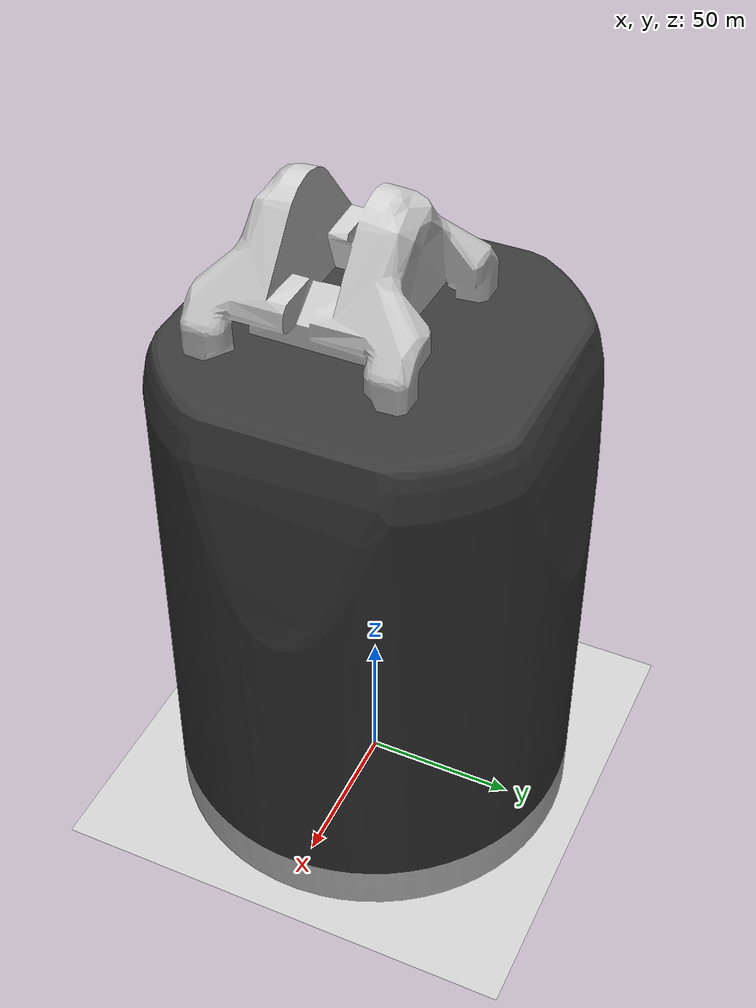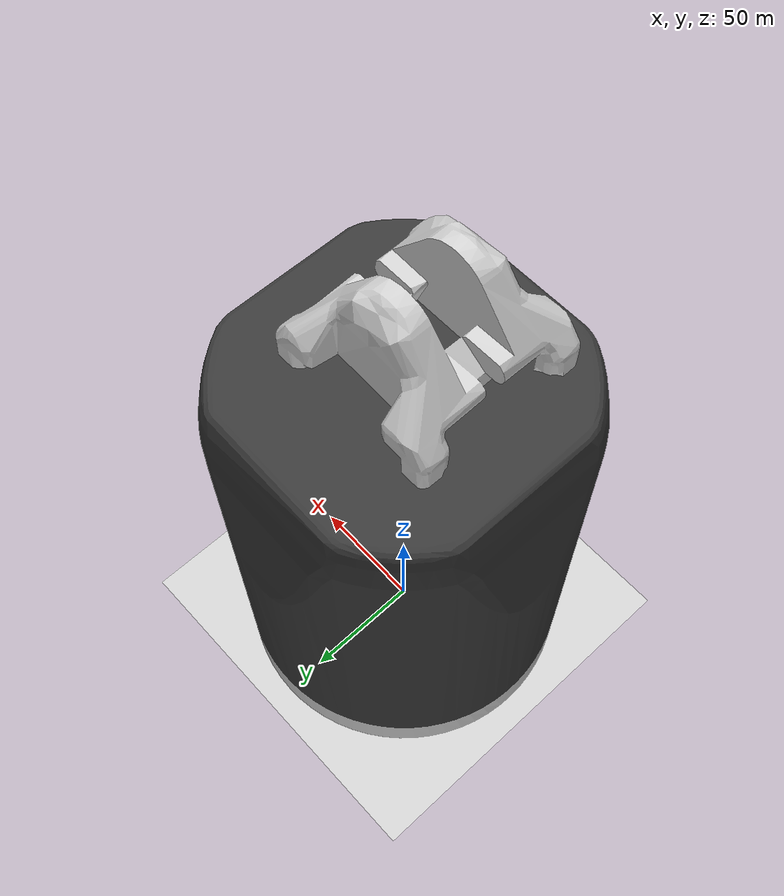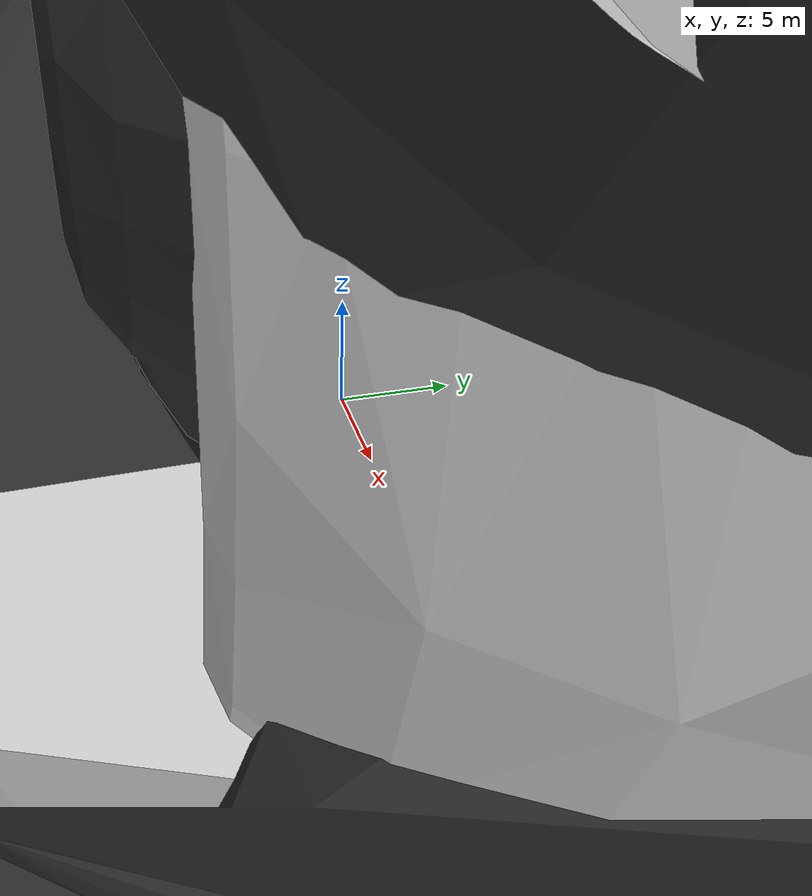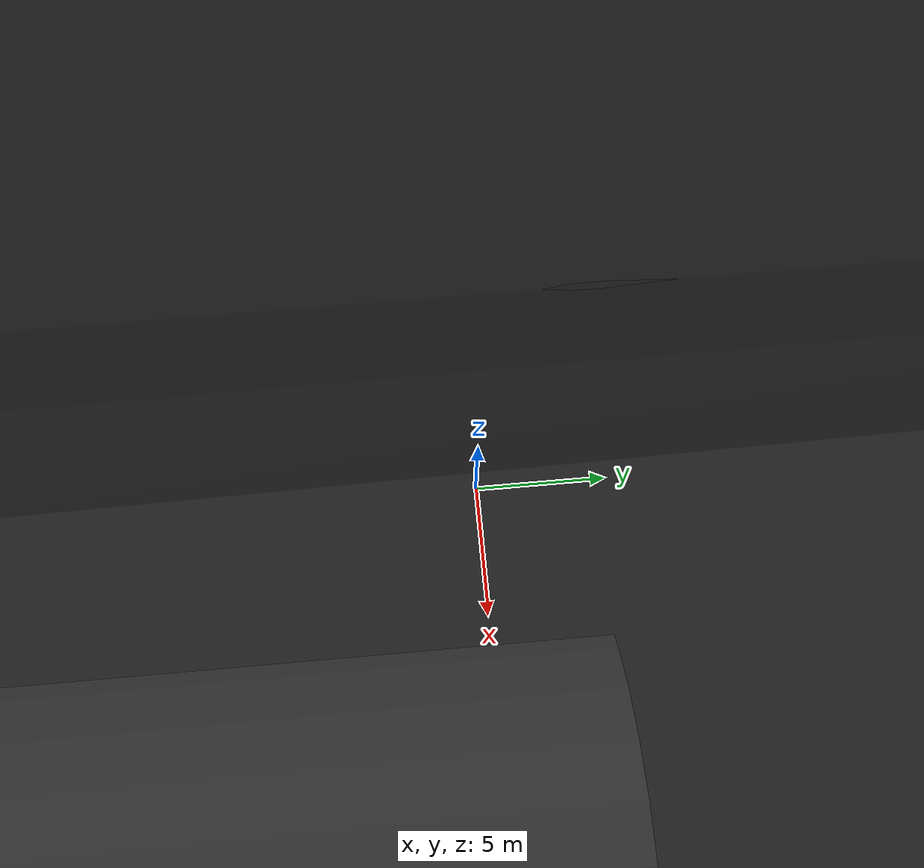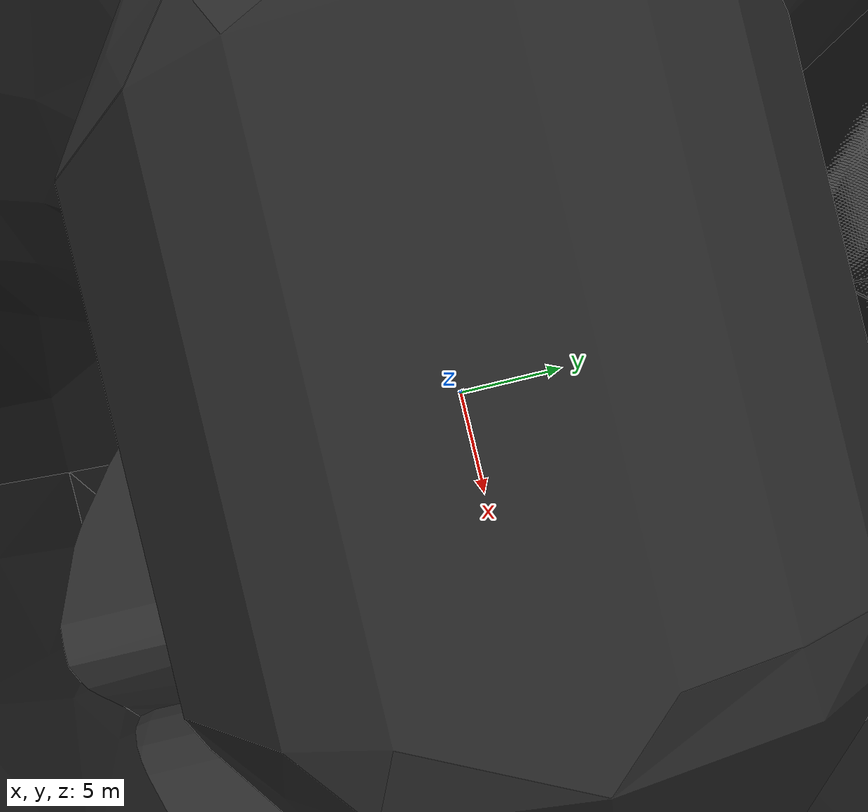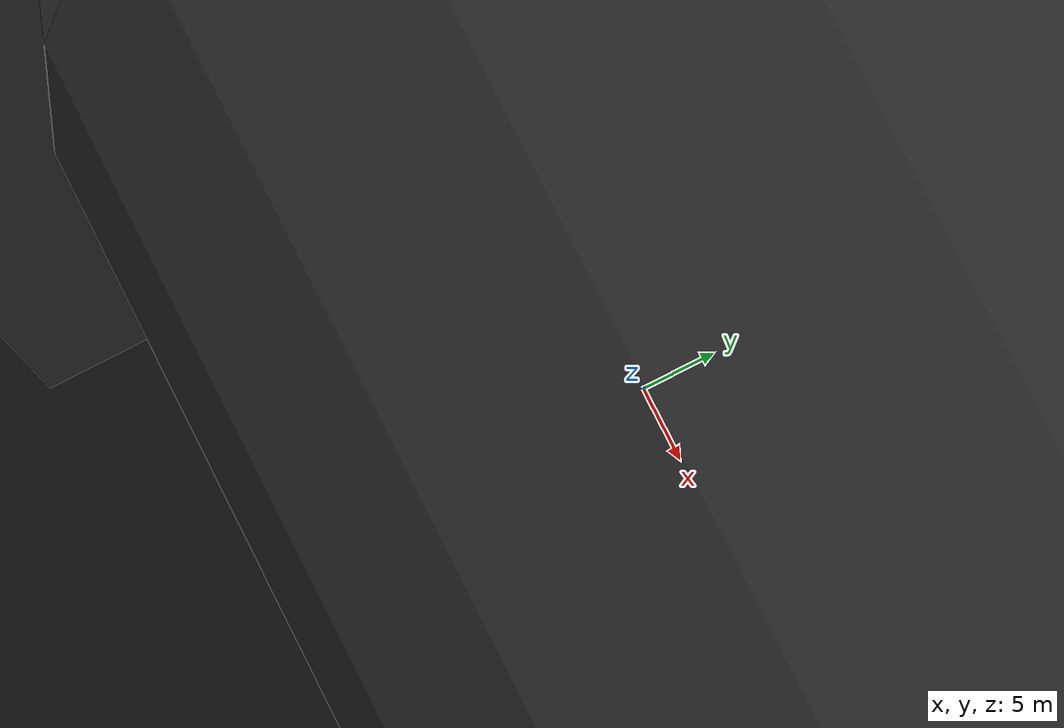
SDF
<sdf version="1.6">
 <world name="default">
  <model name="ground_plane">
   <static>1</static>
   <link name="link">
    <collision name="collision">
     <geometry><plane><normal>0 0 1</normal><size>100 100</size></plane></geometry>
     <surface><friction><ode><mu>100</mu><mu2>50</mu2></ode></friction></surface>
    </collision>
    <visual name="visual">
     <cast_shadows>0</cast_shadows>
     <geometry><plane><normal>0 0 1</normal><size>100 100</size></plane></geometry>
     <material>
      <script><uri>file://media/materials/scripts/gazebo.material</uri><name>Gazebo/Grey</name></script>
     </material>
    </visual>
   </link>
  </model>
  <light name="sun" type="directional">
   <pose>0 0 10 0 -0 0</pose>
   <diffuse>0.8 0.8 0.8 1</diffuse>
   <specular>0.1 0.1 0.1 1</specular>
   <attenuation>
    <range>1000</range>
    <constant>0.9</constant>
    <linear>0.01</linear>
    <quadratic>0.001</quadratic>
   </attenuation>
   <direction>-0.5 0.5 -1</direction>
  </light>
  <physics name="default_physics" default="0" type="ode">
   <ode>
    <solver>
     <type>quick</type>
     <iters>100</iters>
     <precon_iters>0</precon_iters>
     <sor>1</sor>
     <use_dynamic_moi_rescaling>0</use_dynamic_moi_rescaling>
    </solver>
    <constraints>
     <cfm>0</cfm>
     <erp>0.2</erp>
     <contact_max_correcting_vel>0</contact_max_correcting_vel>
     <contact_surface_layer>0</contact_surface_layer>
    </constraints>
   </ode>
   <real_time_update_rate>0</real_time_update_rate>
   <max_step_size>0.001</max_step_size>
   <real_time_factor>1</real_time_factor>
  </physics>
  <gravity>0 0 -9.81</gravity>
  <magnetic_field>6e-06 2.3e-05 -4.2e-05</magnetic_field>
  <atmosphere type="adiabatic"/>
  <scene><ambient>0.4 0.4 0.4 1</ambient><background>0.7 0.7 0.7 1</background><shadows>1</shadows></scene>
  <spherical_coordinates>
   <surface_model>EARTH_WGS84</surface_model>
   <latitude_deg>0</latitude_deg>
   <longitude_deg>0</longitude_deg>
   <elevation>0</elevation>
   <heading_deg>0</heading_deg>
  </spherical_coordinates>
  <model name="shadowhand_motor">
   <link name="rh_forearm">
    <inertial>
     <pose>0 0 0.09 0 -0 0</pose>
     <mass>3</mass>
     <inertia><ixx>0.0138</ixx><ixy>0</ixy><ixz>0</ixz><iyy>0.0138</iyy><iyz>0</iyz><izz>0.00744</izz></inertia>
    </inertial>
    <collision name="rh_forearm_collision">
     <pose>0 0 0.092 0 -0 0</pose>
     <geometry><cylinder><length>0.184</length><radius>0.07</radius></cylinder></geometry>
    </collision>
    <collision name="rh_forearm_collision_1">
     <pose>0 -0.01 0.181 0 0.78 0</pose>
     <geometry><box><size>0.07 0.07 0.07</size></box></geometry>
    </collision>
    <visual name="rh_forearm_visual">
     <geometry>
      <mesh>
       <scale>1 1 1</scale>
       <uri>/home/brhm/DUC/RobotArm/src/my_arm/meshes/shadow_hand/hand/forearm.dae</uri>
      </mesh>
     </geometry>
     <material><script><uri>__default__</uri><name>__default__</name></script></material>
    </visual>
   </link>
   <joint name="rh_world_joint" type="revolute">
    <child>rh_forearm</child>
    <parent>world</parent>
    <axis>
     <limit><lower>0</lower><upper>0</upper></limit>
     <dynamics>
      <damping>0</damping>
      <friction>0</friction>
      <spring_reference>0</spring_reference>
      <spring_stiffness>0</spring_stiffness>
     </dynamics>
     <use_parent_model_frame>1</use_parent_model_frame>
     <xyz>0 0 1</xyz>
    </axis>
   </joint>
   <link name="rh_wrist">
    <pose>0 -0.01 0.213 0 -0 0</pose>
    <inertial>
     <pose>0 0 0.029 0 -0 0</pose>
     <mass>0.1</mass>
     <inertia><ixx>3.5e-05</ixx><ixy>0</ixy><ixz>0</ixz><iyy>6.4e-05</iyy><iyz>0</iyz><izz>4.38e-05</izz></inertia>
    </inertial>
    <collision name="rh_wrist_collision">
     <pose>0 0 0 -3.14159 1.57079 1.57079</pose>
     <geometry><cylinder><length>0.03</length><radius>0.0135</radius></cylinder></geometry>
    </collision>
    <collision name="rh_wrist_collision_1">
     <pose>-0.026 0 0.034 3.14159 1.57079 3.14159</pose>
     <geometry><cylinder><length>0.01</length><radius>0.011</radius></cylinder></geometry>
    </collision>
    <collision name="rh_wrist_collision_2">
     <pose>0.031 0 0.034 3.14159 1.57079 3.14159</pose>
     <geometry><cylinder><length>0.01</length><radius>0.011</radius></cylinder></geometry>
    </collision>
    <collision name="rh_wrist_collision_3">
     <pose>-0.021 0 0.011 0 0.7854 0</pose>
     <geometry><box><size>0.027 0.018 0.01</size></box></geometry>
    </collision>
    <collision name="rh_wrist_collision_4">
     <pose>0.026 0 0.01 0 -0.7854 0</pose>
     <geometry><box><size>0.027 0.018 0.01</size></box></geometry>
    </collision>
    <visual name="rh_wrist_visual">
     <geometry>
      <mesh>
       <scale>1 1 1</scale>
       <uri>/home/brhm/DUC/RobotArm/src/my_arm/meshes/shadow_hand/hand/wrist.dae</uri>
      </mesh>
     </geometry>
     <material>
      <script><name>Gazebo/White</name><uri>file://media/materials/scripts/gazebo.material</uri></script>
     </material>
    </visual>
   </link>
   <joint name="rh_WRJ2" type="revolute">
    <child>rh_wrist</child>
    <parent>rh_forearm</parent>
    <axis>
     <xyz>0 1 0</xyz>
     <limit><lower>-0.523599</lower><upper>0.174533</upper><effort>10</effort><velocity>2</velocity></limit>
     <dynamics>
      <damping>0.1</damping>
      <friction>0</friction>
      <spring_reference>0</spring_reference>
      <spring_stiffness>0</spring_stiffness>
     </dynamics>
     <use_parent_model_frame>1</use_parent_model_frame>
    </axis>
    <physics>
     <provide_feedback>1</provide_feedback>
     <ode>
      <provide_feedback>1</provide_feedback>
      <implicit_spring_damper>1</implicit_spring_damper>
      <cfm_damping>1</cfm_damping>
      <limit><cfm>0</cfm><erp>0.2</erp></limit>
     </ode>
    </physics>
   </joint>
   <link name="rh_palm">
    <pose>0 -0.01 0.247 0 -0 0</pose>
    <inertial>
     <pose>0 0 0.035 0 -0 0</pose>
     <mass>0.3</mass>
     <inertia>
      <ixx>0.0003581</ixx>
      <ixy>0</ixy>
      <ixz>0</ixz>
      <iyy>0.0005287</iyy>
      <iyz>0</iyz>
      <izz>0.000191</izz>
     </inertia>
    </inertial>
    <collision name="rh_palm_collision">
     <pose>0.011 0.0085 0.038 0 -0 0</pose>
     <geometry><box><size>0.062 0.007 0.098</size></box></geometry>
    </collision>
    <collision name="rh_palm_collision_1">
     <pose>-0.002 -0.0035 0.038 0 -0 0</pose>
     <geometry><box><size>0.036 0.017 0.098</size></box></geometry>
    </collision>
    <collision name="rh_palm_collision_2">
     <pose>0.029 -0.0035 0.082 0 -0 0</pose>
     <geometry><box><size>0.026 0.017 0.01</size></box></geometry>
    </collision>
    <collision name="rh_palm_collision_3">
     <pose>0.0265 -0.001 0.07 0.2 -0 0.25</pose>
     <geometry><box><size>0.026 0.014 0.018</size></box></geometry>
    </collision>
    <collision name="rh_palm_collision_4">
     <pose>0.0315 -0.0085 0.001 0 -0 0</pose>
     <geometry><box><size>0.021 0.027 0.024</size></box></geometry>
    </collision>
    <collision name="rh_palm_collision_5">
     <pose>0.0125 -0.015 0.009 0 0 -0.48</pose>
     <geometry><box><size>0.022 0.005 0.04</size></box></geometry>
    </collision>
    <collision name="rh_palm_collision_6">
     <pose>0.011 0 0.089 0 -0 0</pose>
     <geometry><box><size>0.018 0.024 0.004</size></box></geometry>
    </collision>
    <collision name="rh_palm_collision_7">
     <pose>-0.03 0 0.009 0 -0 0</pose>
     <geometry><box><size>0.02 0.024 0.04</size></box></geometry>
    </collision>
    <visual name="rh_palm_visual">
     <geometry>
      <mesh>
       <scale>1 1 1</scale>
       <uri>/home/brhm/DUC/RobotArm/src/my_arm/meshes/shadow_hand/hand/palm.dae</uri>
      </mesh>
     </geometry>
     <material><script><uri>__default__</uri><name>__default__</name></script></material>
    </visual>
    <sensor name="rh_palm_contact" type="contact">
     <always_on>1</always_on>
     <update_rate>1000</update_rate>
     <contact><collision>rh_palm_collision</collision><topic>rh_palm_collision</topic></contact>
     <plugin name="rh_palm_gazebo_ros_bumper_controller" filename="libgazebo_ros_bumper.so">
      <alwaysOn>true</alwaysOn>
      <frameName>rh_palm</frameName>
      <updateRate>100.0</updateRate>
      <bumperTopicName>contacts/rh_palm</bumperTopicName>
      <robotNamespace>/</robotNamespace>
     </plugin>
    </sensor>
   </link>
   <joint name="rh_WRJ1" type="revolute">
    <child>rh_palm</child>
    <parent>rh_wrist</parent>
    <axis>
     <xyz>1 0 0</xyz>
     <limit><lower>-0.698132</lower><upper>0.488692</upper><effort>30</effort><velocity>2</velocity></limit>
     <dynamics>
      <damping>0.1</damping>
      <friction>0</friction>
      <spring_reference>0</spring_reference>
      <spring_stiffness>0</spring_stiffness>
     </dynamics>
     <use_parent_model_frame>1</use_parent_model_frame>
    </axis>
    <physics>
     <provide_feedback>1</provide_feedback>
     <ode>
      <provide_feedback>1</provide_feedback>
      <implicit_spring_damper>1</implicit_spring_damper>
      <cfm_damping>1</cfm_damping>
      <limit><cfm>0</cfm><erp>0.2</erp></limit>
     </ode>
    </physics>
   </joint>
   <link name="rh_ffknuckle">
    <pose>0.033 -0.01 0.342 0 -0 0</pose>
    <inertial>
     <mass>0.008</mass>
     <inertia><ixx>2.6e-07</ixx><ixy>0</ixy><ixz>0</ixz><iyy>2.6e-07</iyy><iyz>0</iyz><izz>3.2e-07</izz></inertia>
    </inertial>
    <collision name="rh_ffknuckle_collision">
     <pose>0 0 0 3.14159 1.57079 3.14159</pose>
     <geometry><cylinder><length>0.014</length><radius>0.007</radius></cylinder></geometry>
    </collision>
    <visual name="rh_ffknuckle_visual">
     <pose>0 0 0.0005 0 -0 0</pose>
     <geometry>
      <mesh>
       <scale>1 1 1</scale>
       <uri>/home/brhm/DUC/RobotArm/src/my_arm/meshes/shadow_hand/hand/knuckle.dae</uri>
      </mesh>
     </geometry>
     <material>
      <script><name>Gazebo/Grey</name><uri>file://media/materials/scripts/gazebo.material</uri></script>
     </material>
    </visual>
    <sensor name="rh_ffknuckle_contact" type="contact">
     <always_on>1</always_on>
     <update_rate>1000</update_rate>
     <contact><collision>rh_ffknuckle_collision</collision><topic>rh_ffknuckle_collision</topic></contact>
     <plugin name="rh_ffknuckle_gazebo_ros_bumper_controller" filename="libgazebo_ros_bumper.so">
      <alwaysOn>true</alwaysOn>
      <frameName>rh_ffknuckle</frameName>
      <updateRate>100.0</updateRate>
      <bumperTopicName>contacts/rh_ff/knuckle</bumperTopicName>
      <robotNamespace>/</robotNamespace>
     </plugin>
    </sensor>
   </link>
   <joint name="rh_FFJ4" type="revolute">
    <child>rh_ffknuckle</child>
    <parent>rh_palm</parent>
    <axis>
     <xyz>0 -1 0</xyz>
     <limit><lower>-0.349066</lower><upper>0.349066</upper><effort>2</effort><velocity>2</velocity></limit>
     <dynamics>
      <damping>0.1</damping>
      <friction>0</friction>
      <spring_reference>0</spring_reference>
      <spring_stiffness>0</spring_stiffness>
     </dynamics>
     <use_parent_model_frame>1</use_parent_model_frame>
    </axis>
    <physics>
     <provide_feedback>1</provide_feedback>
     <ode>
      <provide_feedback>1</provide_feedback>
      <implicit_spring_damper>1</implicit_spring_damper>
      <cfm_damping>1</cfm_damping>
      <limit><cfm>0</cfm><erp>0.2</erp></limit>
     </ode>
    </physics>
   </joint>
   <link name="rh_ffproximal">
    <pose>0.033 -0.01 0.342 0 -0 0</pose>
    <inertial>
     <pose>0 0 0.0225 0 -0 0</pose>
     <mass>0.03</mass>
     <inertia><ixx>9.8e-06</ixx><ixy>0</ixy><ixz>0</ixz><iyy>1e-05</iyy><iyz>0</iyz><izz>1.8e-06</izz></inertia>
    </inertial>
    <collision name="rh_ffproximal_collision">
     <pose>0 0 0.025 0 -0 0</pose>
     <geometry><cylinder><length>0.04</length><radius>0.007</radius></cylinder></geometry>
    </collision>
    <visual name="rh_ffproximal_visual">
     <geometry>
      <mesh><scale>1 1 1</scale><uri>/home/brhm/DUC/RobotArm/src/my_arm/meshes/shadow_hand/hand/F3.dae</uri></mesh>
     </geometry>
     <material><script><uri>__default__</uri><name>__default__</name></script></material>
    </visual>
    <self_collide>1</self_collide>
    <sensor name="rh_ffproximal_contact" type="contact">
     <always_on>1</always_on>
     <update_rate>1000</update_rate>
     <contact><collision>rh_ffproximal_collision</collision><topic>rh_ffproximal_collision</topic></contact>
     <plugin name="rh_ffproximal_gazebo_ros_bumper_controller" filename="libgazebo_ros_bumper.so">
      <alwaysOn>true</alwaysOn>
      <frameName>rh_ffproximal</frameName>
      <updateRate>100.0</updateRate>
      <bumperTopicName>contacts/rh_ff/proximal</bumperTopicName>
      <robotNamespace>/</robotNamespace>
     </plugin>
    </sensor>
   </link>
   <joint name="rh_FFJ3" type="revolute">
    <child>rh_ffproximal</child>
    <parent>rh_ffknuckle</parent>
    <axis>
     <xyz>1 0 0</xyz>
     <limit><lower>0</lower><upper>1.5708</upper><effort>2</effort><velocity>2</velocity></limit>
     <dynamics>
      <damping>0.1</damping>
      <friction>0</friction>
      <spring_reference>0</spring_reference>
      <spring_stiffness>0</spring_stiffness>
     </dynamics>
     <use_parent_model_frame>1</use_parent_model_frame>
    </axis>
    <physics>
     <provide_feedback>1</provide_feedback>
     <ode>
      <provide_feedback>1</provide_feedback>
      <implicit_spring_damper>1</implicit_spring_damper>
      <cfm_damping>1</cfm_damping>
      <limit><cfm>0</cfm><erp>0.2</erp></limit>
     </ode>
    </physics>
   </joint>
   <link name="rh_ffmiddle">
    <pose>0.033 -0.01 0.387 0 -0 0</pose>
    <inertial>
     <pose>0 0 0.0125 0 -0 0</pose>
     <mass>0.017</mass>
     <inertia><ixx>2.6e-06</ixx><ixy>0</ixy><ixz>0</ixz><iyy>2.7e-06</iyy><iyz>0</iyz><izz>8.7e-07</izz></inertia>
    </inertial>
    <collision name="rh_ffmiddle_collision">
     <pose>0 0 0.0125 0 -0 0</pose>
     <geometry><cylinder><length>0.025</length><radius>0.007</radius></cylinder></geometry>
    </collision>
    <collision name="rh_ffmiddle_collision_1">
     <geometry><sphere><radius>0.007</radius></sphere></geometry>
    </collision>
    <collision name="rh_ffmiddle_collision_2">
     <pose>0 0 0.025 0 -0 0</pose>
     <geometry><sphere><radius>0.007</radius></sphere></geometry>
    </collision>
    <visual name="rh_ffmiddle_visual">
     <geometry>
      <mesh><scale>1 1 1</scale><uri>/home/brhm/DUC/RobotArm/src/my_arm/meshes/shadow_hand/hand/F2.dae</uri></mesh>
     </geometry>
     <material><script><uri>__default__</uri><name>__default__</name></script></material>
    </visual>
    <self_collide>1</self_collide>
    <sensor name="rh_ffmiddle_contact" type="contact">
     <always_on>1</always_on>
     <update_rate>1000</update_rate>
     <contact><collision>rh_ffmiddle_collision</collision><topic>rh_ffmiddle_collision</topic></contact>
     <plugin name="rh_ffproximal_gazebo_ros_bumper_controller" filename="libgazebo_ros_bumper.so">
      <alwaysOn>true</alwaysOn>
      <frameName>rh_ffmiddle</frameName>
      <updateRate>100.0</updateRate>
      <bumperTopicName>contacts/rh_ff/middle</bumperTopicName>
      <robotNamespace>/</robotNamespace>
     </plugin>
    </sensor>
   </link>
   <joint name="rh_FFJ2" type="revolute">
    <child>rh_ffmiddle</child>
    <parent>rh_ffproximal</parent>
    <axis>
     <xyz>1 0 0</xyz>
     <limit><lower>0</lower><upper>1.5708</upper><effort>2</effort><velocity>2</velocity></limit>
     <dynamics>
      <damping>0.1</damping>
      <friction>0</friction>
      <spring_reference>0</spring_reference>
      <spring_stiffness>0</spring_stiffness>
     </dynamics>
     <use_parent_model_frame>1</use_parent_model_frame>
    </axis>
    <physics>
     <provide_feedback>1</provide_feedback>
     <ode>
      <provide_feedback>1</provide_feedback>
      <implicit_spring_damper>1</implicit_spring_damper>
      <cfm_damping>1</cfm_damping>
      <limit><cfm>0</cfm><erp>0.2</erp></limit>
     </ode>
    </physics>
   </joint>
   <link name="rh_ffdistal">
    <pose>0.033 -0.01 0.412 0 -0 0</pose>
    <inertial>
     <pose>0 0 0.013077 0 -0 0</pose>
     <mass>0.013</mass>
     <inertia>
      <ixx>1.12092e-06</ixx>
      <ixy>0</ixy>
      <ixz>0</ixz>
      <iyy>1.28092e-06</iyy>
      <iyz>0</iyz>
      <izz>5.3e-07</izz>
     </inertia>
    </inertial>
    <collision name="rh_ffdistal_collision">
     <geometry>
      <mesh><scale>1 1 1</scale><uri>/home/brhm/DUC/RobotArm/src/my_arm/meshes/shadow_hand/hand/F1.dae</uri></mesh>
     </geometry>
     <surface>
      <contact><ode><kp>1e+07</kp><kd>1</kd></ode></contact>
      <friction><ode><mu>500</mu><mu2>500</mu2></ode></friction>
     </surface>
    </collision>
    <visual name="rh_ffdistal_visual">
     <geometry>
      <mesh><scale>1 1 1</scale><uri>/home/brhm/DUC/RobotArm/src/my_arm/meshes/shadow_hand/hand/F1.dae</uri></mesh>
     </geometry>
     <material><script><uri>__default__</uri><name>__default__</name></script></material>
    </visual>
    <self_collide>1</self_collide>
    <sensor name="rh_ffdistal_contact" type="contact">
     <always_on>1</always_on>
     <update_rate>1000</update_rate>
     <contact><collision>rh_ffdistal_collision</collision><topic>rh_ffdistal_collision</topic></contact>
     <plugin name="rh_ffdistal_gazebo_ros_bumper_controller" filename="libgazebo_ros_bumper.so">
      <alwaysOn>true</alwaysOn>
      <frameName>rh_ffdistal</frameName>
      <updateRate>100.0</updateRate>
      <bumperTopicName>contacts/rh_ff/distal</bumperTopicName>
      <robotNamespace>/</robotNamespace>
     </plugin>
    </sensor>
   </link>
   <joint name="rh_FFJ1" type="revolute">
    <child>rh_ffdistal</child>
    <parent>rh_ffmiddle</parent>
    <axis>
     <xyz>1 0 0</xyz>
     <limit><lower>0</lower><upper>1.5708</upper><effort>2</effort><velocity>2</velocity></limit>
     <dynamics>
      <damping>0.1</damping>
      <friction>0</friction>
      <spring_reference>0</spring_reference>
      <spring_stiffness>0</spring_stiffness>
     </dynamics>
     <use_parent_model_frame>1</use_parent_model_frame>
    </axis>
    <physics>
     <provide_feedback>1</provide_feedback>
     <ode>
      <provide_feedback>1</provide_feedback>
      <implicit_spring_damper>1</implicit_spring_damper>
      <cfm_damping>1</cfm_damping>
      <limit><cfm>0</cfm><erp>0.2</erp></limit>
     </ode>
    </physics>
   </joint>
   <link name="rh_lfmetacarpal">
    <pose>-0.033 -0.01 0.26771 0 -0 0</pose>
    <inertial>
     <pose>0 0 0.04 0 -0 0</pose>
     <mass>0.03</mass>
     <inertia>
      <ixx>1.45e-05</ixx>
      <ixy>0</ixy>
      <ixz>0</ixz>
      <iyy>1.638e-05</iyy>
      <iyz>0</iyz>
      <izz>4.272e-06</izz>
     </inertia>
    </inertial>
    <collision name="rh_lfmetacarpal_collision">
     <pose>0 0 0.038 0 -0 0</pose>
     <geometry><box><size>0.018 0.024 0.04</size></box></geometry>
    </collision>
    <visual name="rh_lfmetacarpal_visual">
     <geometry>
      <mesh>
       <scale>1 1 1</scale>
       <uri>/home/brhm/DUC/RobotArm/src/my_arm/meshes/shadow_hand/hand/lfmetacarpal.dae</uri>
      </mesh>
     </geometry>
     <material><script><uri>__default__</uri><name>__default__</name></script></material>
    </visual>
    <self_collide>1</self_collide>
    <sensor name="rh_lfmetacarpal_contact" type="contact">
     <always_on>1</always_on>
     <update_rate>1000</update_rate>
     <contact><collision>rh_lfmetacarpal_collision</collision><topic>rh_lfmetacarpal_collision</topic></contact>
     <plugin name="rh_lfmetacarpal_gazebo_ros_bumper_controller" filename="libgazebo_ros_bumper.so">
      <alwaysOn>true</alwaysOn>
      <frameName>rh_lfmetacarpal</frameName>
      <updateRate>100.0</updateRate>
      <bumperTopicName>contacts/rh_lf/metacarpal</bumperTopicName>
      <robotNamespace>/</robotNamespace>
     </plugin>
    </sensor>
   </link>
   <joint name="rh_LFJ5" type="revolute">
    <child>rh_lfmetacarpal</child>
    <parent>rh_palm</parent>
    <axis>
     <xyz>0.573576 0 0.819152</xyz>
     <limit><lower>0</lower><upper>0.785398</upper><effort>2</effort><velocity>2</velocity></limit>
     <dynamics>
      <damping>0.1</damping>
      <friction>0</friction>
      <spring_reference>0</spring_reference>
      <spring_stiffness>0</spring_stiffness>
     </dynamics>
     <use_parent_model_frame>1</use_parent_model_frame>
    </axis>
    <physics>
     <provide_feedback>1</provide_feedback>
     <ode>
      <provide_feedback>1</provide_feedback>
      <implicit_spring_damper>1</implicit_spring_damper>
      <cfm_damping>1</cfm_damping>
      <limit><cfm>0</cfm><erp>0.2</erp></limit>
     </ode>
    </physics>
   </joint>
   <link name="rh_lfknuckle">
    <pose>-0.033 -0.01 0.3335 0 -0 0</pose>
    <inertial>
     <mass>0.008</mass>
     <inertia><ixx>2.6e-07</ixx><ixy>0</ixy><ixz>0</ixz><iyy>2.6e-07</iyy><iyz>0</iyz><izz>3.2e-07</izz></inertia>
    </inertial>
    <collision name="rh_lfknuckle_collision">
     <pose>0 0 0 3.14159 1.57079 3.14159</pose>
     <geometry><cylinder><length>0.014</length><radius>0.007</radius></cylinder></geometry>
    </collision>
    <visual name="rh_lfknuckle_visual">
     <pose>0 0 0.0005 0 -0 0</pose>
     <geometry>
      <mesh>
       <scale>1 1 1</scale>
       <uri>/home/brhm/DUC/RobotArm/src/my_arm/meshes/shadow_hand/hand/knuckle.dae</uri>
      </mesh>
     </geometry>
     <material>
      <script><name>Gazebo/Grey</name><uri>file://media/materials/scripts/gazebo.material</uri></script>
     </material>
    </visual>
    <sensor name="rh_lfknuckle_contact" type="contact">
     <always_on>1</always_on>
     <update_rate>1000</update_rate>
     <contact><collision>rh_lfknuckle_collision</collision><topic>rh_lfknuckle_collision</topic></contact>
     <plugin name="rh_lfknuckle_gazebo_ros_bumper_controller" filename="libgazebo_ros_bumper.so">
      <alwaysOn>true</alwaysOn>
      <frameName>rh_lfknuckle</frameName>
      <updateRate>100.0</updateRate>
      <bumperTopicName>contacts/rh_lf/knuckle</bumperTopicName>
      <robotNamespace>/</robotNamespace>
     </plugin>
    </sensor>
   </link>
   <joint name="rh_LFJ4" type="revolute">
    <child>rh_lfknuckle</child>
    <parent>rh_lfmetacarpal</parent>
    <axis>
     <xyz>0 1 0</xyz>
     <limit><lower>-0.349066</lower><upper>0.349066</upper><effort>2</effort><velocity>2</velocity></limit>
     <dynamics>
      <damping>0.1</damping>
      <friction>0</friction>
      <spring_reference>0</spring_reference>
      <spring_stiffness>0</spring_stiffness>
     </dynamics>
     <use_parent_model_frame>1</use_parent_model_frame>
    </axis>
    <physics>
     <provide_feedback>1</provide_feedback>
     <ode>
      <provide_feedback>1</provide_feedback>
      <implicit_spring_damper>1</implicit_spring_damper>
      <cfm_damping>1</cfm_damping>
      <limit><cfm>0</cfm><erp>0.2</erp></limit>
     </ode>
    </physics>
   </joint>
   <link name="rh_lfproximal">
    <pose>-0.033 -0.01 0.3335 0 -0 0</pose>
    <inertial>
     <pose>0 0 0.0225 0 -0 0</pose>
     <mass>0.03</mass>
     <inertia><ixx>9.8e-06</ixx><ixy>0</ixy><ixz>0</ixz><iyy>1e-05</iyy><iyz>0</iyz><izz>1.8e-06</izz></inertia>
    </inertial>
    <collision name="rh_lfproximal_collision">
     <pose>0 0 0.025 0 -0 0</pose>
     <geometry><cylinder><length>0.04</length><radius>0.007</radius></cylinder></geometry>
    </collision>
    <visual name="rh_lfproximal_visual">
     <geometry>
      <mesh><scale>1 1 1</scale><uri>/home/brhm/DUC/RobotArm/src/my_arm/meshes/shadow_hand/hand/F3.dae</uri></mesh>
     </geometry>
     <material><script><uri>__default__</uri><name>__default__</name></script></material>
    </visual>
    <self_collide>1</self_collide>
    <sensor name="rh_lfproximal_contact" type="contact">
     <always_on>1</always_on>
     <update_rate>1000</update_rate>
     <contact><collision>rh_lfproximal_collision</collision><topic>rh_lfproximal_collision</topic></contact>
     <plugin name="rh_lfproximal_gazebo_ros_bumper_controller" filename="libgazebo_ros_bumper.so">
      <alwaysOn>true</alwaysOn>
      <frameName>rh_lfproximal</frameName>
      <updateRate>100.0</updateRate>
      <bumperTopicName>contacts/rh_lf/proximal</bumperTopicName>
      <robotNamespace>/</robotNamespace>
     </plugin>
    </sensor>
   </link>
   <joint name="rh_LFJ3" type="revolute">
    <child>rh_lfproximal</child>
    <parent>rh_lfknuckle</parent>
    <axis>
     <xyz>1 0 0</xyz>
     <limit><lower>0</lower><upper>1.5708</upper><effort>2</effort><velocity>2</velocity></limit>
     <dynamics>
      <damping>0.1</damping>
      <friction>0</friction>
      <spring_reference>0</spring_reference>
      <spring_stiffness>0</spring_stiffness>
     </dynamics>
     <use_parent_model_frame>1</use_parent_model_frame>
    </axis>
    <physics>
     <provide_feedback>1</provide_feedback>
     <ode>
      <provide_feedback>1</provide_feedback>
      <implicit_spring_damper>1</implicit_spring_damper>
      <cfm_damping>1</cfm_damping>
      <limit><cfm>0</cfm><erp>0.2</erp></limit>
     </ode>
    </physics>
   </joint>
   <link name="rh_lfmiddle">
    <pose>-0.033 -0.01 0.3785 0 -0 0</pose>
    <inertial>
     <pose>0 0 0.0125 0 -0 0</pose>
     <mass>0.017</mass>
     <inertia><ixx>2.6e-06</ixx><ixy>0</ixy><ixz>0</ixz><iyy>2.7e-06</iyy><iyz>0</iyz><izz>8.7e-07</izz></inertia>
    </inertial>
    <collision name="rh_lfmiddle_collision">
     <pose>0 0 0.0125 0 -0 0</pose>
     <geometry><cylinder><length>0.025</length><radius>0.007</radius></cylinder></geometry>
    </collision>
    <collision name="rh_lfmiddle_collision_1">
     <geometry><sphere><radius>0.007</radius></sphere></geometry>
    </collision>
    <collision name="rh_lfmiddle_collision_2">
     <pose>0 0 0.025 0 -0 0</pose>
     <geometry><sphere><radius>0.007</radius></sphere></geometry>
    </collision>
    <visual name="rh_lfmiddle_visual">
     <geometry>
      <mesh><scale>1 1 1</scale><uri>/home/brhm/DUC/RobotArm/src/my_arm/meshes/shadow_hand/hand/F2.dae</uri></mesh>
     </geometry>
     <material><script><uri>__default__</uri><name>__default__</name></script></material>
    </visual>
    <self_collide>1</self_collide>
    <sensor name="rh_lfmiddle_contact" type="contact">
     <always_on>1</always_on>
     <update_rate>1000</update_rate>
     <contact><collision>rh_lfmiddle_collision</collision><topic>rh_lfmiddle_collision</topic></contact>
     <plugin name="rh_lfproximal_gazebo_ros_bumper_controller" filename="libgazebo_ros_bumper.so">
      <alwaysOn>true</alwaysOn>
      <frameName>rh_lfmiddle</frameName>
      <updateRate>100.0</updateRate>
      <bumperTopicName>contacts/rh_lf/middle</bumperTopicName>
      <robotNamespace>/</robotNamespace>
     </plugin>
    </sensor>
   </link>
   <joint name="rh_LFJ2" type="revolute">
    <child>rh_lfmiddle</child>
    <parent>rh_lfproximal</parent>
    <axis>
     <xyz>1 0 0</xyz>
     <limit><lower>0</lower><upper>1.5708</upper><effort>2</effort><velocity>2</velocity></limit>
     <dynamics>
      <damping>0.1</damping>
      <friction>0</friction>
      <spring_reference>0</spring_reference>
      <spring_stiffness>0</spring_stiffness>
     </dynamics>
     <use_parent_model_frame>1</use_parent_model_frame>
    </axis>
    <physics>
     <provide_feedback>1</provide_feedback>
     <ode>
      <provide_feedback>1</provide_feedback>
      <implicit_spring_damper>1</implicit_spring_damper>
      <cfm_damping>1</cfm_damping>
      <limit><cfm>0</cfm><erp>0.2</erp></limit>
     </ode>
    </physics>
   </joint>
   <link name="rh_lfdistal">
    <pose>-0.033 -0.01 0.4035 0 -0 0</pose>
    <inertial>
     <pose>0 0 0.013077 0 -0 0</pose>
     <mass>0.013</mass>
     <inertia>
      <ixx>1.12092e-06</ixx>
      <ixy>0</ixy>
      <ixz>0</ixz>
      <iyy>1.28092e-06</iyy>
      <iyz>0</iyz>
      <izz>5.3e-07</izz>
     </inertia>
    </inertial>
    <collision name="rh_lfdistal_collision">
     <geometry>
      <mesh><scale>1 1 1</scale><uri>/home/brhm/DUC/RobotArm/src/my_arm/meshes/shadow_hand/hand/F1.dae</uri></mesh>
     </geometry>
     <surface>
      <contact><ode><kp>1e+07</kp><kd>1</kd></ode></contact>
      <friction><ode><mu>500</mu><mu2>500</mu2></ode></friction>
     </surface>
    </collision>
    <visual name="rh_lfdistal_visual">
     <geometry>
      <mesh><scale>1 1 1</scale><uri>/home/brhm/DUC/RobotArm/src/my_arm/meshes/shadow_hand/hand/F1.dae</uri></mesh>
     </geometry>
     <material><script><uri>__default__</uri><name>__default__</name></script></material>
    </visual>
    <self_collide>1</self_collide>
    <sensor name="rh_lfdistal_contact" type="contact">
     <always_on>1</always_on>
     <update_rate>1000</update_rate>
     <contact><collision>rh_lfdistal_collision</collision><topic>rh_lfdistal_collision</topic></contact>
     <plugin name="rh_lfdistal_gazebo_ros_bumper_controller" filename="libgazebo_ros_bumper.so">
      <alwaysOn>true</alwaysOn>
      <frameName>rh_lfdistal</frameName>
      <updateRate>100.0</updateRate>
      <bumperTopicName>contacts/rh_lf/distal</bumperTopicName>
      <robotNamespace>/</robotNamespace>
     </plugin>
    </sensor>
   </link>
   <joint name="rh_LFJ1" type="revolute">
    <child>rh_lfdistal</child>
    <parent>rh_lfmiddle</parent>
    <axis>
     <xyz>1 0 0</xyz>
     <limit><lower>0</lower><upper>1.5708</upper><effort>2</effort><velocity>2</velocity></limit>
     <dynamics>
      <damping>0.1</damping>
      <friction>0</friction>
      <spring_reference>0</spring_reference>
      <spring_stiffness>0</spring_stiffness>
     </dynamics>
     <use_parent_model_frame>1</use_parent_model_frame>
    </axis>
    <physics>
     <provide_feedback>1</provide_feedback>
     <ode>
      <provide_feedback>1</provide_feedback>
      <implicit_spring_damper>1</implicit_spring_damper>
      <cfm_damping>1</cfm_damping>
      <limit><cfm>0</cfm><erp>0.2</erp></limit>
     </ode>
    </physics>
   </joint>
   <link name="rh_mfknuckle">
    <pose>0.011 -0.01 0.346 0 -0 0</pose>
    <inertial>
     <mass>0.008</mass>
     <inertia><ixx>2.6e-07</ixx><ixy>0</ixy><ixz>0</ixz><iyy>2.6e-07</iyy><iyz>0</iyz><izz>3.2e-07</izz></inertia>
    </inertial>
    <collision name="rh_mfknuckle_collision">
     <pose>0 0 0 3.14159 1.57079 3.14159</pose>
     <geometry><cylinder><length>0.014</length><radius>0.007</radius></cylinder></geometry>
    </collision>
    <visual name="rh_mfknuckle_visual">
     <pose>0 0 0.0005 0 -0 0</pose>
     <geometry>
      <mesh>
       <scale>1 1 1</scale>
       <uri>/home/brhm/DUC/RobotArm/src/my_arm/meshes/shadow_hand/hand/knuckle.dae</uri>
      </mesh>
     </geometry>
     <material>
      <script><name>Gazebo/Grey</name><uri>file://media/materials/scripts/gazebo.material</uri></script>
     </material>
    </visual>
    <sensor name="rh_mfknuckle_contact" type="contact">
     <always_on>1</always_on>
     <update_rate>1000</update_rate>
     <contact><collision>rh_mfknuckle_collision</collision><topic>rh_mfknuckle_collision</topic></contact>
     <plugin name="rh_mfknuckle_gazebo_ros_bumper_controller" filename="libgazebo_ros_bumper.so">
      <alwaysOn>true</alwaysOn>
      <frameName>rh_mfknuckle</frameName>
      <updateRate>100.0</updateRate>
      <bumperTopicName>contacts/rh_mf/knuckle</bumperTopicName>
      <robotNamespace>/</robotNamespace>
     </plugin>
    </sensor>
   </link>
   <joint name="rh_MFJ4" type="revolute">
    <child>rh_mfknuckle</child>
    <parent>rh_palm</parent>
    <axis>
     <xyz>0 -1 0</xyz>
     <limit><lower>-0.349066</lower><upper>0.349066</upper><effort>2</effort><velocity>2</velocity></limit>
     <dynamics>
      <damping>0.1</damping>
      <friction>0</friction>
      <spring_reference>0</spring_reference>
      <spring_stiffness>0</spring_stiffness>
     </dynamics>
     <use_parent_model_frame>1</use_parent_model_frame>
    </axis>
    <physics>
     <provide_feedback>1</provide_feedback>
     <ode>
      <provide_feedback>1</provide_feedback>
      <implicit_spring_damper>1</implicit_spring_damper>
      <cfm_damping>1</cfm_damping>
      <limit><cfm>0</cfm><erp>0.2</erp></limit>
     </ode>
    </physics>
   </joint>
   <link name="rh_mfproximal">
    <pose>0.011 -0.01 0.346 0 -0 0</pose>
    <inertial>
     <pose>0 0 0.0225 0 -0 0</pose>
     <mass>0.03</mass>
     <inertia><ixx>9.8e-06</ixx><ixy>0</ixy><ixz>0</ixz><iyy>1e-05</iyy><iyz>0</iyz><izz>1.8e-06</izz></inertia>
    </inertial>
    <collision name="rh_mfproximal_collision">
     <pose>0 0 0.025 0 -0 0</pose>
     <geometry><cylinder><length>0.04</length><radius>0.007</radius></cylinder></geometry>
    </collision>
    <visual name="rh_mfproximal_visual">
     <geometry>
      <mesh><scale>1 1 1</scale><uri>/home/brhm/DUC/RobotArm/src/my_arm/meshes/shadow_hand/hand/F3.dae</uri></mesh>
     </geometry>
     <material><script><uri>__default__</uri><name>__default__</name></script></material>
    </visual>
    <self_collide>1</self_collide>
    <sensor name="rh_mfproximal_contact" type="contact">
     <always_on>1</always_on>
     <update_rate>1000</update_rate>
     <contact><collision>rh_mfproximal_collision</collision><topic>rh_mfproximal_collision</topic></contact>
     <plugin name="rh_mfproximal_gazebo_ros_bumper_controller" filename="libgazebo_ros_bumper.so">
      <alwaysOn>true</alwaysOn>
      <frameName>rh_mfproximal</frameName>
      <updateRate>100.0</updateRate>
      <bumperTopicName>contacts/rh_mf/proximal</bumperTopicName>
      <robotNamespace>/</robotNamespace>
     </plugin>
    </sensor>
   </link>
   <joint name="rh_MFJ3" type="revolute">
    <child>rh_mfproximal</child>
    <parent>rh_mfknuckle</parent>
    <axis>
     <xyz>1 0 0</xyz>
     <limit><lower>0</lower><upper>1.5708</upper><effort>2</effort><velocity>2</velocity></limit>
     <dynamics>
      <damping>0.1</damping>
      <friction>0</friction>
      <spring_reference>0</spring_reference>
      <spring_stiffness>0</spring_stiffness>
     </dynamics>
     <use_parent_model_frame>1</use_parent_model_frame>
    </axis>
    <physics>
     <provide_feedback>1</provide_feedback>
     <ode>
      <provide_feedback>1</provide_feedback>
      <implicit_spring_damper>1</implicit_spring_damper>
      <cfm_damping>1</cfm_damping>
      <limit><cfm>0</cfm><erp>0.2</erp></limit>
     </ode>
    </physics>
   </joint>
   <link name="rh_mfmiddle">
    <pose>0.011 -0.01 0.391 0 -0 0</pose>
    <inertial>
     <pose>0 0 0.0125 0 -0 0</pose>
     <mass>0.017</mass>
     <inertia><ixx>2.6e-06</ixx><ixy>0</ixy><ixz>0</ixz><iyy>2.7e-06</iyy><iyz>0</iyz><izz>8.7e-07</izz></inertia>
    </inertial>
    <collision name="rh_mfmiddle_collision">
     <pose>0 0 0.0125 0 -0 0</pose>
     <geometry><cylinder><length>0.025</length><radius>0.007</radius></cylinder></geometry>
    </collision>
    <collision name="rh_mfmiddle_collision_1">
     <geometry><sphere><radius>0.007</radius></sphere></geometry>
    </collision>
    <collision name="rh_mfmiddle_collision_2">
     <pose>0 0 0.025 0 -0 0</pose>
     <geometry><sphere><radius>0.007</radius></sphere></geometry>
    </collision>
    <visual name="rh_mfmiddle_visual">
     <geometry>
      <mesh><scale>1 1 1</scale><uri>/home/brhm/DUC/RobotArm/src/my_arm/meshes/shadow_hand/hand/F2.dae</uri></mesh>
     </geometry>
     <material><script><uri>__default__</uri><name>__default__</name></script></material>
    </visual>
    <self_collide>1</self_collide>
    <sensor name="rh_mfmiddle_contact" type="contact">
     <always_on>1</always_on>
     <update_rate>1000</update_rate>
     <contact><collision>rh_mfmiddle_collision</collision><topic>rh_mfmiddle_collision</topic></contact>
     <plugin name="rh_mfproximal_gazebo_ros_bumper_controller" filename="libgazebo_ros_bumper.so">
      <alwaysOn>true</alwaysOn>
      <frameName>rh_mfmiddle</frameName>
      <updateRate>100.0</updateRate>
      <bumperTopicName>contacts/rh_mf/middle</bumperTopicName>
      <robotNamespace>/</robotNamespace>
     </plugin>
    </sensor>
   </link>
   <joint name="rh_MFJ2" type="revolute">
    <child>rh_mfmiddle</child>
    <parent>rh_mfproximal</parent>
    <axis>
     <xyz>1 0 0</xyz>
     <limit><lower>0</lower><upper>1.5708</upper><effort>2</effort><velocity>2</velocity></limit>
     <dynamics>
      <damping>0.1</damping>
      <friction>0</friction>
      <spring_reference>0</spring_reference>
      <spring_stiffness>0</spring_stiffness>
     </dynamics>
     <use_parent_model_frame>1</use_parent_model_frame>
    </axis>
    <physics>
     <provide_feedback>1</provide_feedback>
     <ode>
      <provide_feedback>1</provide_feedback>
      <implicit_spring_damper>1</implicit_spring_damper>
      <cfm_damping>1</cfm_damping>
      <limit><cfm>0</cfm><erp>0.2</erp></limit>
     </ode>
    </physics>
   </joint>
   <link name="rh_mfdistal">
    <pose>0.011 -0.01 0.416 0 -0 0</pose>
    <inertial>
     <pose>0 0 0.013077 0 -0 0</pose>
     <mass>0.013</mass>
     <inertia>
      <ixx>1.12092e-06</ixx>
      <ixy>0</ixy>
      <ixz>0</ixz>
      <iyy>1.28092e-06</iyy>
      <iyz>0</iyz>
      <izz>5.3e-07</izz>
     </inertia>
    </inertial>
    <collision name="rh_mfdistal_collision">
     <geometry>
      <mesh><scale>1 1 1</scale><uri>/home/brhm/DUC/RobotArm/src/my_arm/meshes/shadow_hand/hand/F1.dae</uri></mesh>
     </geometry>
     <surface>
      <contact><ode><kp>1e+07</kp><kd>1</kd></ode></contact>
      <friction><ode><mu>500</mu><mu2>500</mu2></ode></friction>
     </surface>
    </collision>
    <visual name="rh_mfdistal_visual">
     <geometry>
      <mesh><scale>1 1 1</scale><uri>/home/brhm/DUC/RobotArm/src/my_arm/meshes/shadow_hand/hand/F1.dae</uri></mesh>
     </geometry>
     <material><script><uri>__default__</uri><name>__default__</name></script></material>
    </visual>
    <self_collide>1</self_collide>
    <sensor name="rh_mfdistal_contact" type="contact">
     <always_on>1</always_on>
     <update_rate>1000</update_rate>
     <contact><collision>rh_mfdistal_collision</collision><topic>rh_mfdistal_collision</topic></contact>
     <plugin name="rh_mfdistal_gazebo_ros_bumper_controller" filename="libgazebo_ros_bumper.so">
      <alwaysOn>true</alwaysOn>
      <frameName>rh_mfdistal</frameName>
      <updateRate>100.0</updateRate>
      <bumperTopicName>contacts/rh_mf/distal</bumperTopicName>
      <robotNamespace>/</robotNamespace>
     </plugin>
    </sensor>
   </link>
   <joint name="rh_MFJ1" type="revolute">
    <child>rh_mfdistal</child>
    <parent>rh_mfmiddle</parent>
    <axis>
     <xyz>1 0 0</xyz>
     <limit><lower>0</lower><upper>1.5708</upper><effort>2</effort><velocity>2</velocity></limit>
     <dynamics>
      <damping>0.1</damping>
      <friction>0</friction>
      <spring_reference>0</spring_reference>
      <spring_stiffness>0</spring_stiffness>
     </dynamics>
     <use_parent_model_frame>1</use_parent_model_frame>
    </axis>
    <physics>
     <provide_feedback>1</provide_feedback>
     <ode>
      <provide_feedback>1</provide_feedback>
      <implicit_spring_damper>1</implicit_spring_damper>
      <cfm_damping>1</cfm_damping>
      <limit><cfm>0</cfm><erp>0.2</erp></limit>
     </ode>
    </physics>
   </joint>
   <link name="rh_rfknuckle">
    <pose>-0.011 -0.01 0.342 0 -0 0</pose>
    <inertial>
     <mass>0.008</mass>
     <inertia><ixx>2.6e-07</ixx><ixy>0</ixy><ixz>0</ixz><iyy>2.6e-07</iyy><iyz>0</iyz><izz>3.2e-07</izz></inertia>
    </inertial>
    <collision name="rh_rfknuckle_collision">
     <pose>0 0 0 3.14159 1.57079 3.14159</pose>
     <geometry><cylinder><length>0.014</length><radius>0.007</radius></cylinder></geometry>
    </collision>
    <visual name="rh_rfknuckle_visual">
     <pose>0 0 0.0005 0 -0 0</pose>
     <geometry>
      <mesh>
       <scale>1 1 1</scale>
       <uri>/home/brhm/DUC/RobotArm/src/my_arm/meshes/shadow_hand/hand/knuckle.dae</uri>
      </mesh>
     </geometry>
     <material>
      <script><name>Gazebo/Grey</name><uri>file://media/materials/scripts/gazebo.material</uri></script>
     </material>
    </visual>
    <sensor name="rh_rfknuckle_contact" type="contact">
     <always_on>1</always_on>
     <update_rate>1000</update_rate>
     <contact><collision>rh_rfknuckle_collision</collision><topic>rh_rfknuckle_collision</topic></contact>
     <plugin name="rh_rfknuckle_gazebo_ros_bumper_controller" filename="libgazebo_ros_bumper.so">
      <alwaysOn>true</alwaysOn>
      <frameName>rh_rfknuckle</frameName>
      <updateRate>100.0</updateRate>
      <bumperTopicName>contacts/rh_rf/knuckle</bumperTopicName>
      <robotNamespace>/</robotNamespace>
     </plugin>
    </sensor>
   </link>
   <joint name="rh_RFJ4" type="revolute">
    <child>rh_rfknuckle</child>
    <parent>rh_palm</parent>
    <axis>
     <xyz>0 1 0</xyz>
     <limit><lower>-0.349066</lower><upper>0.349066</upper><effort>2</effort><velocity>2</velocity></limit>
     <dynamics>
      <damping>0.1</damping>
      <friction>0</friction>
      <spring_reference>0</spring_reference>
      <spring_stiffness>0</spring_stiffness>
     </dynamics>
     <use_parent_model_frame>1</use_parent_model_frame>
    </axis>
    <physics>
     <provide_feedback>1</provide_feedback>
     <ode>
      <provide_feedback>1</provide_feedback>
      <implicit_spring_damper>1</implicit_spring_damper>
      <cfm_damping>1</cfm_damping>
      <limit><cfm>0</cfm><erp>0.2</erp></limit>
     </ode>
    </physics>
   </joint>
   <link name="rh_rfproximal">
    <pose>-0.011 -0.01 0.342 0 -0 0</pose>
    <inertial>
     <pose>0 0 0.0225 0 -0 0</pose>
     <mass>0.03</mass>
     <inertia><ixx>9.8e-06</ixx><ixy>0</ixy><ixz>0</ixz><iyy>1e-05</iyy><iyz>0</iyz><izz>1.8e-06</izz></inertia>
    </inertial>
    <collision name="rh_rfproximal_collision">
     <pose>0 0 0.025 0 -0 0</pose>
     <geometry><cylinder><length>0.04</length><radius>0.007</radius></cylinder></geometry>
    </collision>
    <visual name="rh_rfproximal_visual">
     <geometry>
      <mesh><scale>1 1 1</scale><uri>/home/brhm/DUC/RobotArm/src/my_arm/meshes/shadow_hand/hand/F3.dae</uri></mesh>
     </geometry>
     <material><script><uri>__default__</uri><name>__default__</name></script></material>
    </visual>
    <self_collide>1</self_collide>
    <sensor name="rh_rfproximal_contact" type="contact">
     <always_on>1</always_on>
     <update_rate>1000</update_rate>
     <contact><collision>rh_rfproximal_collision</collision><topic>rh_rfproximal_collision</topic></contact>
     <plugin name="rh_rfproximal_gazebo_ros_bumper_controller" filename="libgazebo_ros_bumper.so">
      <alwaysOn>true</alwaysOn>
      <frameName>rh_rfproximal</frameName>
      <updateRate>100.0</updateRate>
      <bumperTopicName>contacts/rh_rf/proximal</bumperTopicName>
      <robotNamespace>/</robotNamespace>
     </plugin>
    </sensor>
   </link>
   <joint name="rh_RFJ3" type="revolute">
    <child>rh_rfproximal</child>
    <parent>rh_rfknuckle</parent>
    <axis>
     <xyz>1 0 0</xyz>
     <limit><lower>0</lower><upper>1.5708</upper><effort>2</effort><velocity>2</velocity></limit>
     <dynamics>
      <damping>0.1</damping>
      <friction>0</friction>
      <spring_reference>0</spring_reference>
      <spring_stiffness>0</spring_stiffness>
     </dynamics>
     <use_parent_model_frame>1</use_parent_model_frame>
    </axis>
    <physics>
     <provide_feedback>1</provide_feedback>
     <ode>
      <provide_feedback>1</provide_feedback>
      <implicit_spring_damper>1</implicit_spring_damper>
      <cfm_damping>1</cfm_damping>
      <limit><cfm>0</cfm><erp>0.2</erp></limit>
     </ode>
    </physics>
   </joint>
   <link name="rh_rfmiddle">
    <pose>-0.011 -0.01 0.387 0 -0 0</pose>
    <inertial>
     <pose>0 0 0.0125 0 -0 0</pose>
     <mass>0.017</mass>
     <inertia><ixx>2.6e-06</ixx><ixy>0</ixy><ixz>0</ixz><iyy>2.7e-06</iyy><iyz>0</iyz><izz>8.7e-07</izz></inertia>
    </inertial>
    <collision name="rh_rfmiddle_collision">
     <pose>0 0 0.0125 0 -0 0</pose>
     <geometry><cylinder><length>0.025</length><radius>0.007</radius></cylinder></geometry>
    </collision>
    <collision name="rh_rfmiddle_collision_1">
     <geometry><sphere><radius>0.007</radius></sphere></geometry>
    </collision>
    <collision name="rh_rfmiddle_collision_2">
     <pose>0 0 0.025 0 -0 0</pose>
     <geometry><sphere><radius>0.007</radius></sphere></geometry>
    </collision>
    <visual name="rh_rfmiddle_visual">
     <geometry>
      <mesh><scale>1 1 1</scale><uri>/home/brhm/DUC/RobotArm/src/my_arm/meshes/shadow_hand/hand/F2.dae</uri></mesh>
     </geometry>
     <material><script><uri>__default__</uri><name>__default__</name></script></material>
    </visual>
    <self_collide>1</self_collide>
    <sensor name="rh_rfmiddle_contact" type="contact">
     <always_on>1</always_on>
     <update_rate>1000</update_rate>
     <contact><collision>rh_rfmiddle_collision</collision><topic>rh_rfmiddle_collision</topic></contact>
     <plugin name="rh_rfproximal_gazebo_ros_bumper_controller" filename="libgazebo_ros_bumper.so">
      <alwaysOn>true</alwaysOn>
      <frameName>rh_rfmiddle</frameName>
      <updateRate>100.0</updateRate>
      <bumperTopicName>contacts/rh_rf/middle</bumperTopicName>
      <robotNamespace>/</robotNamespace>
     </plugin>
    </sensor>
   </link>
   <joint name="rh_RFJ2" type="revolute">
    <child>rh_rfmiddle</child>
    <parent>rh_rfproximal</parent>
    <axis>
     <xyz>1 0 0</xyz>
     <limit><lower>0</lower><upper>1.5708</upper><effort>2</effort><velocity>2</velocity></limit>
     <dynamics>
      <damping>0.1</damping>
      <friction>0</friction>
      <spring_reference>0</spring_reference>
      <spring_stiffness>0</spring_stiffness>
     </dynamics>
     <use_parent_model_frame>1</use_parent_model_frame>
    </axis>
    <physics>
     <provide_feedback>1</provide_feedback>
     <ode>
      <provide_feedback>1</provide_feedback>
      <implicit_spring_damper>1</implicit_spring_damper>
      <cfm_damping>1</cfm_damping>
      <limit><cfm>0</cfm><erp>0.2</erp></limit>
     </ode>
    </physics>
   </joint>
   <link name="rh_rfdistal">
    <pose>-0.011 -0.01 0.412 0 -0 0</pose>
    <inertial>
     <pose>0 0 0.013077 0 -0 0</pose>
     <mass>0.013</mass>
     <inertia>
      <ixx>1.12092e-06</ixx>
      <ixy>0</ixy>
      <ixz>0</ixz>
      <iyy>1.28092e-06</iyy>
      <iyz>0</iyz>
      <izz>5.3e-07</izz>
     </inertia>
    </inertial>
    <collision name="rh_rfdistal_collision">
     <geometry>
      <mesh><scale>1 1 1</scale><uri>/home/brhm/DUC/RobotArm/src/my_arm/meshes/shadow_hand/hand/F1.dae</uri></mesh>
     </geometry>
     <surface>
      <contact><ode><kp>1e+07</kp><kd>1</kd></ode></contact>
      <friction><ode><mu>500</mu><mu2>500</mu2></ode></friction>
     </surface>
    </collision>
    <visual name="rh_rfdistal_visual">
     <geometry>
      <mesh><scale>1 1 1</scale><uri>/home/brhm/DUC/RobotArm/src/my_arm/meshes/shadow_hand/hand/F1.dae</uri></mesh>
     </geometry>
     <material><script><uri>__default__</uri><name>__default__</name></script></material>
    </visual>
    <self_collide>1</self_collide>
    <sensor name="rh_rfdistal_contact" type="contact">
     <always_on>1</always_on>
     <update_rate>1000</update_rate>
     <contact><collision>rh_rfdistal_collision</collision><topic>rh_rfdistal_collision</topic></contact>
     <plugin name="rh_rfdistal_gazebo_ros_bumper_controller" filename="libgazebo_ros_bumper.so">
      <alwaysOn>true</alwaysOn>
      <frameName>rh_rfdistal</frameName>
      <updateRate>100.0</updateRate>
      <bumperTopicName>contacts/rh_rf/distal</bumperTopicName>
      <robotNamespace>/</robotNamespace>
     </plugin>
    </sensor>
   </link>
   <joint name="rh_RFJ1" type="revolute">
    <child>rh_rfdistal</child>
    <parent>rh_rfmiddle</parent>
    <axis>
     <xyz>1 0 0</xyz>
     <limit><lower>0</lower><upper>1.5708</upper><effort>2</effort><velocity>2</velocity></limit>
     <dynamics>
      <damping>0.1</damping>
      <friction>0</friction>
      <spring_reference>0</spring_reference>
      <spring_stiffness>0</spring_stiffness>
     </dynamics>
     <use_parent_model_frame>1</use_parent_model_frame>
    </axis>
    <physics>
     <provide_feedback>1</provide_feedback>
     <ode>
      <provide_feedback>1</provide_feedback>
      <implicit_spring_damper>1</implicit_spring_damper>
      <cfm_damping>1</cfm_damping>
      <limit><cfm>0</cfm><erp>0.2</erp></limit>
     </ode>
    </physics>
   </joint>
   <link name="rh_thbase">
    <pose>0.034 -0.0185 0.276 0 0.785398 0</pose>
    <inertial>
     <mass>0.01</mass>
     <inertia><ixx>1.6e-07</ixx><ixy>0</ixy><ixz>0</ixz><iyy>1.6e-07</iyy><iyz>0</iyz><izz>1.6e-07</izz></inertia>
    </inertial>
    <collision name="rh_thbase_collision"><geometry><sphere><radius>0.011</radius></sphere></geometry></collision>
    <visual name="rh_thbase_visual">
     <geometry><box><size>0.001 0.001 0.001</size></box></geometry>
     <material><script><uri>__default__</uri><name>__default__</name></script></material>
    </visual>
    <sensor name="rh_thbase_contact" type="contact">
     <always_on>1</always_on>
     <update_rate>1000</update_rate>
     <contact><collision>rh_thbase_collision</collision><topic>rh_thbase_collision</topic></contact>
     <plugin name="rh_thbase_gazebo_ros_bumper_controller" filename="libgazebo_ros_bumper.so">
      <alwaysOn>true</alwaysOn>
      <frameName>rh_thbase</frameName>
      <updateRate>100.0</updateRate>
      <bumperTopicName>contacts/rh_th/base</bumperTopicName>
      <robotNamespace>/</robotNamespace>
     </plugin>
    </sensor>
   </link>
   <joint name="rh_THJ5" type="revolute">
    <child>rh_thbase</child>
    <parent>rh_palm</parent>
    <axis>
     <xyz>-0.707107 0 -0.707107</xyz>
     <limit><lower>-1.0472</lower><upper>1.0472</upper><effort>5</effort><velocity>4</velocity></limit>
     <dynamics>
      <damping>0.2</damping>
      <friction>0</friction>
      <spring_reference>0</spring_reference>
      <spring_stiffness>0</spring_stiffness>
     </dynamics>
     <use_parent_model_frame>1</use_parent_model_frame>
    </axis>
    <physics>
     <provide_feedback>1</provide_feedback>
     <ode>
      <provide_feedback>1</provide_feedback>
      <implicit_spring_damper>1</implicit_spring_damper>
      <cfm_damping>1</cfm_damping>
      <limit><cfm>0</cfm><erp>0.2</erp></limit>
     </ode>
    </physics>
   </joint>
   <link name="rh_thproximal">
    <pose>0.034 -0.0185 0.276 0 0.785398 0</pose>
    <inertial>
     <pose>0 0 0.019 0 -0 0</pose>
     <mass>0.04</mass>
     <inertia>
      <ixx>1.36e-05</ixx>
      <ixy>0</ixy>
      <ixz>0</ixz>
      <iyy>1.36e-05</iyy>
      <iyz>0</iyz>
      <izz>3.13e-06</izz>
     </inertia>
    </inertial>
    <collision name="rh_thproximal_collision">
     <pose>0 0 0.02 0 -0 0</pose>
     <geometry><cylinder><length>0.018</length><radius>0.012</radius></cylinder></geometry>
    </collision>
    <visual name="rh_thproximal_visual">
     <geometry>
      <mesh>
       <scale>1 1 1</scale>
       <uri>/home/brhm/DUC/RobotArm/src/my_arm/meshes/shadow_hand/hand/TH3_z.dae</uri>
      </mesh>
     </geometry>
     <material><script><uri>__default__</uri><name>__default__</name></script></material>
    </visual>
    <sensor name="rh_thproximal_contact" type="contact">
     <always_on>1</always_on>
     <update_rate>1000</update_rate>
     <contact><collision>rh_thproximal_collision</collision><topic>rh_thproximal_collision</topic></contact>
     <plugin name="rh_thproximal_gazebo_ros_bumper_controller" filename="libgazebo_ros_bumper.so">
      <alwaysOn>true</alwaysOn>
      <frameName>rh_thproximal</frameName>
      <updateRate>100.0</updateRate>
      <bumperTopicName>contacts/rh_th/proximal</bumperTopicName>
      <robotNamespace>/</robotNamespace>
     </plugin>
    </sensor>
   </link>
   <joint name="rh_THJ4" type="revolute">
    <child>rh_thproximal</child>
    <parent>rh_thbase</parent>
    <axis>
     <xyz>0.707107 0 -0.707107</xyz>
     <limit><lower>0</lower><upper>1.22173</upper><effort>3</effort><velocity>4</velocity></limit>
     <dynamics>
      <damping>0.2</damping>
      <friction>0</friction>
      <spring_reference>0</spring_reference>
      <spring_stiffness>0</spring_stiffness>
     </dynamics>
     <use_parent_model_frame>1</use_parent_model_frame>
    </axis>
    <physics>
     <provide_feedback>1</provide_feedback>
     <ode>
      <provide_feedback>1</provide_feedback>
      <implicit_spring_damper>1</implicit_spring_damper>
      <cfm_damping>1</cfm_damping>
      <limit><cfm>0</cfm><erp>0.2</erp></limit>
     </ode>
    </physics>
   </joint>
   <link name="rh_thhub">
    <pose>0.06087 -0.0185 0.30287 0 0.785398 0</pose>
    <inertial>
     <mass>0.005</mass>
     <inertia><ixx>1e-06</ixx><ixy>0</ixy><ixz>0</ixz><iyy>1e-06</iyy><iyz>0</iyz><izz>3e-07</izz></inertia>
    </inertial>
    <collision name="rh_thhub_collision"><geometry><sphere><radius>0.01</radius></sphere></geometry></collision>
    <visual name="rh_thhub_visual">
     <geometry><box><size>0.001 0.001 0.001</size></box></geometry>
     <material><script><uri>__default__</uri><name>__default__</name></script></material>
    </visual>
    <self_collide>1</self_collide>
    <sensor name="rh_thhub_contact" type="contact">
     <always_on>1</always_on>
     <update_rate>1000</update_rate>
     <contact><collision>rh_thhub_collision</collision><topic>rh_thhub_collision</topic></contact>
     <plugin name="rh_thhub_gazebo_ros_bumper_controller" filename="libgazebo_ros_bumper.so">
      <alwaysOn>true</alwaysOn>
      <frameName>rh_thhub</frameName>
      <updateRate>100.0</updateRate>
      <bumperTopicName>contacts/rh_th/hub</bumperTopicName>
      <robotNamespace>/</robotNamespace>
     </plugin>
    </sensor>
   </link>
   <joint name="rh_THJ3" type="revolute">
    <child>rh_thhub</child>
    <parent>rh_thproximal</parent>
    <axis>
     <xyz>0.707107 0 -0.707107</xyz>
     <limit><lower>-0.20944</lower><upper>0.20944</upper><effort>2</effort><velocity>4</velocity></limit>
     <dynamics>
      <damping>0.2</damping>
      <friction>0</friction>
      <spring_reference>0</spring_reference>
      <spring_stiffness>0</spring_stiffness>
     </dynamics>
     <use_parent_model_frame>1</use_parent_model_frame>
    </axis>
    <physics>
     <provide_feedback>1</provide_feedback>
     <ode>
      <provide_feedback>1</provide_feedback>
      <implicit_spring_damper>1</implicit_spring_damper>
      <cfm_damping>1</cfm_damping>
      <limit><cfm>0</cfm><erp>0.2</erp></limit>
     </ode>
    </physics>
   </joint>
   <link name="rh_thmiddle">
    <pose>0.06087 -0.0185 0.30287 0 0.785398 0</pose>
    <inertial>
     <pose>0 0 0.016 0 -0 0</pose>
     <mass>0.02</mass>
     <inertia><ixx>5.1e-06</ixx><ixy>0</ixy><ixz>0</ixz><iyy>5.1e-06</iyy><iyz>0</iyz><izz>1.21e-06</izz></inertia>
    </inertial>
    <collision name="rh_thmiddle_collision">
     <pose>0 0 0.012 0 -0 0</pose>
     <geometry><cylinder><length>0.018</length><radius>0.011</radius></cylinder></geometry>
    </collision>
    <collision name="rh_thmiddle_collision_1">
     <pose>0 0 0.019 0 -0 0</pose>
     <geometry><sphere><radius>0.011</radius></sphere></geometry>
    </collision>
    <visual name="rh_thmiddle_visual">
     <geometry>
      <mesh>
       <scale>1 1 1</scale>
       <uri>/home/brhm/DUC/RobotArm/src/my_arm/meshes/shadow_hand/hand/TH2_z.dae</uri>
      </mesh>
     </geometry>
     <material><script><uri>__default__</uri><name>__default__</name></script></material>
    </visual>
    <self_collide>1</self_collide>
    <sensor name="rh_thmiddle_contact" type="contact">
     <always_on>1</always_on>
     <update_rate>1000</update_rate>
     <contact><collision>rh_thmiddle_collision</collision><topic>rh_thmiddle_collision</topic></contact>
     <plugin name="rh_thmiddle_gazebo_ros_bumper_controller" filename="libgazebo_ros_bumper.so">
      <alwaysOn>true</alwaysOn>
      <frameName>rh_thmiddle</frameName>
      <updateRate>100.0</updateRate>
      <bumperTopicName>contacts/rh_th/middle</bumperTopicName>
      <robotNamespace>/</robotNamespace>
     </plugin>
    </sensor>
   </link>
   <joint name="rh_THJ2" type="revolute">
    <child>rh_thmiddle</child>
    <parent>rh_thhub</parent>
    <axis>
     <xyz>0 -1 0</xyz>
     <limit><lower>-0.698132</lower><upper>0.698132</upper><effort>2</effort><velocity>2</velocity></limit>
     <dynamics>
      <damping>0.1</damping>
      <friction>0</friction>
      <spring_reference>0</spring_reference>
      <spring_stiffness>0</spring_stiffness>
     </dynamics>
     <use_parent_model_frame>1</use_parent_model_frame>
    </axis>
    <physics>
     <provide_feedback>1</provide_feedback>
     <ode>
      <provide_feedback>1</provide_feedback>
      <implicit_spring_damper>1</implicit_spring_damper>
      <cfm_damping>1</cfm_damping>
      <limit><cfm>0</cfm><erp>0.2</erp></limit>
     </ode>
    </physics>
   </joint>
   <link name="rh_thdistal">
    <pose>0.083498 -0.0185 0.325497 -0.785398 0 -1.5708</pose>
    <inertial>
     <pose>0 0 0.014559 0 -0 0</pose>
     <mass>0.017</mass>
     <inertia>
      <ixx>2.27794e-06</ixx>
      <ixy>0</ixy>
      <ixz>0</ixz>
      <iyy>2.37794e-06</iyy>
      <iyz>0</iyz>
      <izz>1e-06</izz>
     </inertia>
    </inertial>
    <collision name="rh_thdistal_collision">
     <geometry>
      <mesh>
       <scale>1 1 1</scale>
       <uri>/home/brhm/DUC/RobotArm/src/my_arm/meshes/shadow_hand/hand/TH1_z.dae</uri>
      </mesh>
     </geometry>
     <surface>
      <contact><ode><kp>1e+07</kp><kd>1</kd></ode></contact>
      <friction><ode><mu>500</mu><mu2>500</mu2></ode></friction>
     </surface>
    </collision>
    <visual name="rh_thdistal_visual">
     <geometry>
      <mesh>
       <scale>1 1 1</scale>
       <uri>/home/brhm/DUC/RobotArm/src/my_arm/meshes/shadow_hand/hand/TH1_z.dae</uri>
      </mesh>
     </geometry>
     <material><script><uri>__default__</uri><name>__default__</name></script></material>
    </visual>
    <self_collide>1</self_collide>
    <sensor name="rh_thdistal_contact" type="contact">
     <always_on>1</always_on>
     <update_rate>1000</update_rate>
     <contact><collision>rh_thdistal_collision</collision><topic>rh_thdistal_collision</topic></contact>
     <plugin name="rh_thdistal_gazebo_ros_bumper_controller" filename="libgazebo_ros_bumper.so">
      <alwaysOn>true</alwaysOn>
      <frameName>rh_thdistal</frameName>
      <updateRate>100.0</updateRate>
      <bumperTopicName>contacts/rh_th/distal</bumperTopicName>
      <robotNamespace>/</robotNamespace>
     </plugin>
    </sensor>
   </link>
   <joint name="rh_THJ1" type="revolute">
    <child>rh_thdistal</child>
    <parent>rh_thmiddle</parent>
    <axis>
     <xyz>0 -1 0</xyz>
     <limit><lower>0</lower><upper>1.5708</upper><effort>1</effort><velocity>4</velocity></limit>
     <dynamics>
      <damping>0.2</damping>
      <friction>0</friction>
      <spring_reference>0</spring_reference>
      <spring_stiffness>0</spring_stiffness>
     </dynamics>
     <use_parent_model_frame>1</use_parent_model_frame>
    </axis>
    <physics>
     <provide_feedback>1</provide_feedback>
     <ode>
      <provide_feedback>1</provide_feedback>
      <implicit_spring_damper>1</implicit_spring_damper>
      <cfm_damping>1</cfm_damping>
      <limit><cfm>0</cfm><erp>0.2</erp></limit>
     </ode>
    </physics>
   </joint>
   <static>0</static>
   <plugin name="gazebo_ros_control" filename="libgazebo_ros_control.so">
    <robotSimType>sr_gazebo_sim/SrGazeboHWSim</robotSimType>
    <robotNamespace>/</robotNamespace>
   </plugin>
   <plugin name="gazebo_my_arm_control" filename="libgazeboRobotArmController.so">
    <robotSimType>my_arm_gazebo_sim/DefaultRobotHWSim</robotSimType>
    <jointName>rh_world_joint, rh_WRJ2, rh_WRJ1, rh_THJ5, rh_THJ4, rh_THJ3, rh_THJ2, rh_THJ1, rh_thtip, rh_FFJ4, rh_FFJ3, rh_FFJ2, rh_FFJ1, rh_MFJ4, rh_MFJ3, rh_MFJ2, rh_MFJ1, rh_RFJ4, rh_RFJ3, rh_RFJ2, rh_RFJ1, rh_LFJ5, rh_LFJ4, rh_LFJ3, rh_LFJ2, rh_LFJ1</jointName>
    <updateRate>100.0</updateRate>
    <alwaysOn>true</alwaysOn>
   </plugin>
  </model>
  <model name="drc_practice_hinged_door">
   <link name="frame">
    <pose>0.06 -0.0005 0 0 -0 0</pose>
    <inertial>
     <pose>-0.025145 -0.03429 1.0541 0 -0 0</pose>
     <mass>19</mass>
     <inertia>
      <ixx>7.04458</ixx>
      <ixy>0</ixy>
      <ixz>0</ixz>
      <iyy>7.04114</iyy>
      <iyz>0</iyz>
      <izz>0.0114511</izz>
     </inertia>
    </inertial>
    <collision name="collision_2">
     <pose>-0.025145 -0.03429 1.0541 0 -0 0</pose>
     <geometry><box><size>0.05029 0.06858 2.1082</size></box></geometry>
    </collision>
    <visual name="visual">
     <pose>-0.025145 -0.03429 1.0541 0 -0 0</pose>
     <geometry><box><size>0.05029 0.06858 2.1082</size></box></geometry>
     <material>
      <script><uri>file://media/materials/scripts/gazebo.material</uri><name>Gazebo/White</name></script>
     </material>
    </visual>
   </link>
   <link name="door">
    <pose>-0 0 2.04 3.14159 -0 0</pose>
    <inertial>
     <mass>41.3256</mass>
     <pose>0.4569 0.0349 1.016 0 -0 0</pose>
     <inertia><ixx>14.2263</ixx><ixy>0</ixy><ixz>0</ixz><iyy>17.099</iyy><iyz>0</iyz><izz>2.88626</izz></inertia>
    </inertial>
    <collision name="collision">
     <pose>0.4569 0.0349 1.016 0 -0 0</pose>
     <geometry><box><size>0.9144 0.04445 2.032</size></box></geometry>
    </collision>
    <visual name="visual">
     <pose>0 -0.06858 0 0 -0 0</pose>
     <geometry><mesh><uri>model://hinged_door/meshes/door.dae</uri><scale>1 1 1</scale></mesh></geometry>
    </visual>
   </link>
   <link name="handles">
    <pose>0.8144 0 1.05 3.14159 0.001593 3.14159</pose>
    <inertial>
     <pose>0 -0.035 0 0 -0 0</pose>
     <mass>2</mass>
     <inertia>
      <ixx>0.0110115</ixx>
      <ixy>-0</ixy>
      <ixz>-0.00647057</ixz>
      <iyy>0.0190181</iyy>
      <iyz>0</iyz>
      <izz>0.00824372</izz>
     </inertia>
    </inertial>
    <collision name="handle1_collision">
     <pose>0.015 -0.015 0 -1.57 0 0</pose>
     <geometry><mesh><uri>model://door_handle/meshes/handle.dae</uri><scale>1 1 1</scale></mesh></geometry>
    </collision>
    <visual name="handle1_visual">
     <pose>0.015 -0.015 0 -1.57 0 0</pose>
     <geometry><mesh><uri>model://door_handle/meshes/handle.dae</uri><scale>1 1 1</scale></mesh></geometry>
    </visual>
    <collision name="handle2_collision">
     <pose>0.015 -0.055 0 1.57 -0 0</pose>
     <geometry><mesh><uri>model://door_handle/meshes/handle.dae</uri><scale>1 1 1</scale></mesh></geometry>
    </collision>
    <visual name="handle2_visual">
     <pose>0.015 -0.055 0 1.57 -0 0</pose>
     <geometry><mesh><uri>model://door_handle/meshes/handle.dae</uri><scale>1 1 1</scale></mesh></geometry>
    </visual>
   </link>
   <joint name="handle" type="revolute">
    <parent>door</parent>
    <child>handles</child>
    <pose>0.015 0 0 0 -0 0</pose>
    <axis>
     <xyz>0 1 0</xyz>
     <limit><lower>-1.58</lower><upper>0</upper></limit>
     <dynamics>
      <damping>1</damping>
      <friction>10</friction>
      <spring_reference>0</spring_reference>
      <spring_stiffness>0</spring_stiffness>
     </dynamics>
     <use_parent_model_frame>1</use_parent_model_frame>
    </axis>
    <physics><ode><cfm_damping>1</cfm_damping><limit><cfm>0</cfm><erp>0.2</erp></limit></ode></physics>
   </joint>
   <joint name="hinge" type="revolute">
    <parent>frame</parent>
    <child>door</child>
    <axis>
     <xyz>0 0 1</xyz>
     <limit><lower>-1.58</lower><upper>0</upper></limit>
     <dynamics>
      <damping>1</damping>
      <friction>1</friction>
      <spring_reference>0</spring_reference>
      <spring_stiffness>0</spring_stiffness>
     </dynamics>
     <use_parent_model_frame>1</use_parent_model_frame>
    </axis>
    <physics><ode><cfm_damping>1</cfm_damping><limit><cfm>0</cfm><erp>0.2</erp></limit></ode></physics>
   </joint>
   <joint name="world_joint" type="revolute">
    <child>frame</child>
    <parent>world</parent>
    <axis>
     <limit><lower>0</lower><upper>0</upper></limit>
     <xyz>0 1 0</xyz>
     <dynamics>
      <damping>1</damping>
      <spring_reference>0</spring_reference>
      <spring_stiffness>0</spring_stiffness>
     </dynamics>
     <use_parent_model_frame>1</use_parent_model_frame>
    </axis>
    <physics><ode><cfm_damping>1</cfm_damping><limit><cfm>0</cfm><erp>0.2</erp></limit></ode></physics>
   </joint>
   <pose>-1.13014 0.065249 0 0 -0 0</pose>
  </model>
  <model name="mpl_right_arm">
   <link name="shoulder">
    <pose>0 0 0.093285 0 0 -0.011537</pose>
    <inertial>
     <pose>0.000536 0.002002 0.03328 0 -0 0</pose>
     <mass>0.0363799</mass>
     <inertia>
      <ixx>3.73005e-05</ixx>
      <ixy>5.68571e-07</ixy>
      <ixz>-7.59543e-07</ixz>
      <iyy>2.60558e-05</iyy>
      <iyz>-9.15512e-07</iyz>
      <izz>3.86186e-05</izz>
     </inertia>
    </inertial>
    <collision name="collision">
     <pose>0 0 0.0345 0 -0 0</pose>
     <geometry><sphere><radius>0.03495</radius></sphere></geometry>
     <surface>
      <contact><ode><kp>100000</kp><kd>10</kd><max_vel>0.1</max_vel><min_depth>0.0015</min_depth></ode></contact>
     </surface>
    </collision>
    <collision name="collision_1">
     <pose>0 0 0.01892 0 -0 0</pose>
     <geometry><cylinder><radius>0.038</radius><length>0.03784</length></cylinder></geometry>
     <surface>
      <contact><ode><kp>100000</kp><kd>10</kd><max_vel>0.1</max_vel><min_depth>0.0015</min_depth></ode></contact>
     </surface>
    </collision>
    <visual name="visual">
     <geometry><mesh><uri>model://mpl_right_arm/meshes/shoulder.stl</uri><scale>1 1 1</scale></mesh></geometry>
     <material><script><name>Gazebo/FlatBlack</name><uri>__default__</uri></script></material>
    </visual>
   </link>
   <link name="humerus">
    <pose>0.001643 -1.9e-05 0.12058 0 0 -0.011537</pose>
    <inertial>
     <pose>-0.00523 -0.083481 0.010842 0 -0 0</pose>
     <mass>0.0857896</mass>
     <inertia>
      <ixx>0.000259543</ixx>
      <ixy>-4.20463e-06</ixy>
      <ixz>9.18286e-07</ixz>
      <iyy>0.000134353</iyy>
      <iyz>-1.37928e-05</iyz>
      <izz>0.000284981</izz>
     </inertia>
    </inertial>
    <collision name="collision">
     <pose>-0.00164 -0.07024 0.01366 1.5707 -0 0</pose>
     <geometry><cylinder><radius>0.037035</radius><length>0.15849</length></cylinder></geometry>
     <surface>
      <contact><ode><kp>100000</kp><kd>10</kd><max_vel>0.1</max_vel><min_depth>0.0015</min_depth></ode></contact>
     </surface>
    </collision>
    <visual name="visual">
     <geometry><mesh><uri>model://mpl_right_arm/meshes/humerus.stl</uri><scale>1 1 1</scale></mesh></geometry>
     <material><script><name>Gazebo/FlatBlack</name><uri>__default__</uri></script></material>
    </visual>
   </link>
   <link name="elbow">
    <pose>-0.001728 -0.150057 0.134471 0 0 -0.011537</pose>
    <inertial>
     <pose>0.001164 -0.074089 -0.007315 0 -0 0</pose>
     <mass>0.0351897</mass>
     <inertia>
      <ixx>0.000106583</ixx>
      <ixy>-5.90862e-06</ixy>
      <ixz>-2.34382e-06</ixz>
      <iyy>3.29639e-05</iyy>
      <iyz>1.56515e-05</iyz>
      <izz>0.000106705</izz>
     </inertia>
    </inertial>
    <collision name="collision">
     <pose>0 -0.05957 0.00147 1.5707 -0 0</pose>
     <geometry><cylinder><radius>0.03447</radius><length>0.11914</length></cylinder></geometry>
     <surface>
      <contact><ode><kp>100000</kp><kd>10</kd><max_vel>0.1</max_vel><min_depth>0.0015</min_depth></ode></contact>
     </surface>
    </collision>
    <collision name="collision_1">
     <pose>0.00997 -0.1445 -0.0245 0 -0 0</pose>
     <geometry><cylinder><radius>0.036</radius><length>0.018</length></cylinder></geometry>
     <surface>
      <contact><ode><kp>100000</kp><kd>10</kd><max_vel>0.1</max_vel><min_depth>0.0015</min_depth></ode></contact>
     </surface>
    </collision>
    <visual name="visual">
     <geometry><mesh><uri>model://mpl_right_arm/meshes/elbow.stl</uri><scale>1 1 1</scale></mesh></geometry>
     <material>
      <ambient>0.2 0.2 0.2 1</ambient>
      <diffuse>0.8 0.8 0.8 1</diffuse>
      <specular>0.9 0.9 0.9 1</specular>
     </material>
    </visual>
   </link>
   <link name="forearm">
    <pose>0.006605 -0.294573 0.119123 0 0 -0.011537</pose>
    <inertial>
     <pose>-0.000589 -0.073314 0.021553 0 -0 0</pose>
     <mass>0.0997005</mass>
     <inertia>
      <ixx>0.0004998</ixx>
      <ixy>-5.83136e-06</ixy>
      <ixz>3.56083e-07</ixz>
      <iyy>0.00010215</iyy>
      <iyz>3.76069e-05</iyz>
      <izz>0.000498862</izz>
     </inertia>
    </inertial>
    <collision name="collision">
     <pose>0 0 0.02855 0 -0 0</pose>
     <geometry><cylinder><radius>0.03567</radius><length>0.0571</length></cylinder></geometry>
     <surface>
      <contact><ode><kp>100000</kp><kd>10</kd><max_vel>0.1</max_vel><min_depth>0.0015</min_depth></ode></contact>
     </surface>
    </collision>
    <collision name="collision_1">
     <pose>0 -0.10745 0.016 1.5707 -0 0</pose>
     <geometry><cylinder><radius>0.035</radius><length>0.148</length></cylinder></geometry>
     <surface>
      <contact><ode><kp>100000</kp><kd>10</kd><max_vel>0.1</max_vel><min_depth>0.0015</min_depth></ode></contact>
     </surface>
    </collision>
    <visual name="visual">
     <geometry><mesh><uri>model://mpl_right_arm/meshes/forearm.stl</uri><scale>1 1 1</scale></mesh></geometry>
     <material><script><name>Gazebo/FlatBlack</name><uri>__default__</uri></script></material>
    </visual>
    <sensor name="forearm_contact_sensor" type="contact">
     <contact>
      <collision>collision</collision>
      <collision>collision_1</collision>
      <topic>~/forearm/contact</topic>
     </contact>
    </sensor>
   </link>
   <link name="wristy">
    <pose>0.004499 -0.479995 0.135123 0 0 -0.011537</pose>
    <inertial>
     <pose>-7.1e-05 -0.021779 -0.000286 0 -0 0</pose>
     <mass>0.0272932</mass>
     <inertia>
      <ixx>1.77029e-05</ixx>
      <ixy>7.89061e-09</ixy>
      <ixz>4.33867e-09</ixz>
      <iyy>2.46772e-05</iyy>
      <iyz>1.77331e-07</iyz>
      <izz>1.7112e-05</izz>
     </inertia>
    </inertial>
    <collision name="collision">
     <pose>0 -0.025 0 1.5707 -0 0</pose>
     <geometry><cylinder><radius>0.03447</radius><length>0.05</length></cylinder></geometry>
     <surface>
      <contact><ode><kp>100000</kp><kd>10</kd><max_vel>0.1</max_vel><min_depth>0.0015</min_depth></ode></contact>
     </surface>
    </collision>
    <visual name="visual">
     <geometry><mesh><uri>model://mpl_right_arm/meshes/wristy.stl</uri><scale>1 1 1</scale></mesh></geometry>
     <material>
      <ambient>0.2 0.2 0.2 1</ambient>
      <diffuse>0.8 0.8 0.8 1</diffuse>
      <specular>0.9 0.9 0.9 1</specular>
     </material>
    </visual>
    <sensor name="wristy_contact_sensor" type="contact">
     <contact><collision>collision</collision><topic>~/wristy/contact</topic></contact>
    </sensor>
   </link>
   <link name="wristx">
    <pose>0.003916 -0.527636 0.137161 0 0 -0.011537</pose>
    <inertial>
     <pose>0.001392 -0.009752 -0.002527 0 -0 0</pose>
     <mass>0.010691</mass>
     <inertia>
      <ixx>3.27995e-06</ixx>
      <ixy>-1.50151e-07</ixy>
      <ixz>5.11904e-09</ixz>
      <iyy>4.22942e-06</iyy>
      <iyz>-4.20007e-08</iyz>
      <izz>5.04229e-06</izz>
     </inertia>
    </inertial>
    <collision name="collision">
     <pose>0 0 -0.00314 0 -0 0</pose>
     <geometry><cylinder><radius>0.01473</radius><length>0.04478</length></cylinder></geometry>
     <surface>
      <contact><ode><kp>100000</kp><kd>10</kd><max_vel>0.1</max_vel><min_depth>0.0015</min_depth></ode></contact>
     </surface>
    </collision>
    <collision name="collision_1">
     <pose>0.0236 -0.02969 -0.0024 0 1.5707 0</pose>
     <geometry><cylinder><radius>0.013175</radius><length>0.005</length></cylinder></geometry>
     <surface>
      <contact><ode><kp>100000</kp><kd>10</kd><max_vel>0.1</max_vel><min_depth>0.0015</min_depth></ode></contact>
     </surface>
    </collision>
    <collision name="collision_2">
     <pose>-0.0236 -0.02969 -0.0024 0 1.5707 0</pose>
     <geometry><cylinder><radius>0.013175</radius><length>0.005</length></cylinder></geometry>
     <surface>
      <contact><ode><kp>100000</kp><kd>10</kd><max_vel>0.1</max_vel><min_depth>0.0015</min_depth></ode></contact>
     </surface>
    </collision>
    <visual name="visual">
     <geometry><mesh><uri>model://mpl_right_arm/meshes/wristx.stl</uri><scale>1 1 1</scale></mesh></geometry>
     <material>
      <ambient>0.2 0.2 0.2 1</ambient>
      <diffuse>0.8 0.8 0.8 1</diffuse>
      <specular>0.9 0.9 0.9 1</specular>
     </material>
    </visual>
    <sensor name="wristx_contact_sensor" type="contact">
     <contact>
      <collision>collision</collision>
      <collision>collision_1</collision>
      <collision>collision_2</collision>
      <topic>~/wristx/contact</topic>
     </contact>
    </sensor>
   </link>
   <link name="wristz">
    <pose>0.003757 -0.557636 0.135067 0 0 -0.011537</pose>
    <inertial>
     <pose>0.003682 -0.035876 0.002659 0 -0 0</pose>
     <mass>0.125889</mass>
     <inertia>
      <ixx>8.18077e-05</ixx>
      <ixy>-9.44149e-06</ixy>
      <ixz>3.88366e-06</ixz>
      <iyy>9.81482e-05</iyy>
      <iyz>-4.84151e-08</iyz>
      <izz>0.000131783</izz>
     </inertia>
    </inertial>
    <collision name="collision">
     <pose>0.00207 -0.00047 0.00046 1.5707 0 1.5707</pose>
     <geometry><cylinder><radius>0.01411</radius><length>0.04482</length></cylinder></geometry>
     <surface>
      <contact><ode><kp>100000</kp><kd>10</kd><max_vel>0.1</max_vel><min_depth>0.0015</min_depth></ode></contact>
     </surface>
    </collision>
    <collision name="collision_palm">
     <pose>0.002 -0.03739 0 0 -0 0</pose>
     <geometry><box><size>0.07928 0.08316 0.04402</size></box></geometry>
     <surface>
      <contact><ode><kp>100000</kp><kd>100</kd><max_vel>0.1</max_vel><min_depth>0.0015</min_depth></ode></contact>
     </surface>
    </collision>
    <visual name="visual">
     <geometry><mesh><uri>model://mpl_right_arm/meshes/wristz.stl</uri><scale>1 1 1</scale></mesh></geometry>
     <material>
      <ambient>0.2 0.2 0.2 1</ambient>
      <diffuse>0.8 0.8 0.8 1</diffuse>
      <specular>0.9 0.9 0.9 1</specular>
     </material>
    </visual>
    <visual name="visual_palm">
     <pose>0.025625 0 0 0 -0 0</pose>
     <geometry><mesh><uri>model://mpl_right_arm/meshes/palm.stl</uri><scale>1 1 1</scale></mesh></geometry>
     <material><script><name>Gazebo/FlatBlack</name><uri>__default__</uri></script></material>
    </visual>
    <sensor name="palm_contact_sensor" type="contact">
     <contact><collision>collision_palm</collision><topic>~/palm/contact</topic></contact>
    </sensor>
   </link>
   <link name="index0">
    <pose>0.038485 -0.623842 0.136079 0 0.174533 -0.011537</pose>
    <inertial>
     <pose>-0.000143 -0.005485 0.000206 0 -0 0</pose>
     <mass>0.00295579</mass>
     <inertia>
      <ixx>4.22375e-07</ixx>
      <ixy>4.23313e-09</ixy>
      <ixz>5.00708e-10</ixz>
      <iyy>1.94048e-07</iyy>
      <iyz>-4.58697e-09</iyz>
      <izz>4.02188e-07</izz>
     </inertia>
    </inertial>
    <collision name="collision">
     <pose>0 -0.01339 0 1.5707 -0 0</pose>
     <geometry><cylinder><length>0.028</length><radius>0.01</radius></cylinder></geometry>
     <surface>
      <contact><ode><kp>100000</kp><kd>10</kd><max_vel>0.1</max_vel><min_depth>0.0015</min_depth></ode></contact>
     </surface>
    </collision>
    <visual name="visual">
     <geometry><mesh><uri>model://mpl_right_arm/meshes/index0.stl</uri><scale>1 1 1</scale></mesh></geometry>
     <material><script><name>Gazebo/FlatBlack</name><uri>__default__</uri></script></material>
    </visual>
    <sensor name="index0_contact_sensor" type="contact">
     <contact><collision>collision</collision><topic>~/index0/contact</topic></contact>
    </sensor>
   </link>
   <link name="index1">
    <pose>0.038339 -0.641841 0.136068 0 0.174533 -0.011537</pose>
    <inertial>
     <pose>0.000406 -0.021313 0.000656 0 -0 0</pose>
     <mass>0.00478235</mass>
     <inertia>
      <ixx>8.18593e-07</ixx>
      <ixy>-1.2874e-09</ixy>
      <ixz>1.78664e-10</ixz>
      <iyy>3.06547e-07</iyy>
      <iyz>-1.18998e-08</iyz>
      <izz>7.95406e-07</izz>
     </inertia>
    </inertial>
    <collision name="collision">
     <pose>0 -0.02782 0 1.5707 -0 0</pose>
     <geometry><cylinder><radius>0.01</radius><length>0.02781</length></cylinder></geometry>
     <surface>
      <contact><ode><kp>100000</kp><kd>10</kd><max_vel>0.1</max_vel><min_depth>0.0015</min_depth></ode></contact>
     </surface>
    </collision>
    <visual name="visual">
     <geometry><mesh><uri>model://mpl_right_arm/meshes/index1.stl</uri><scale>1 1 1</scale></mesh></geometry>
     <material><script><name>Gazebo/FlatBlack</name><uri>__default__</uri></script></material>
    </visual>
    <sensor name="index1_contact_sensor" type="contact">
     <contact><collision>collision</collision><topic>~/index1/contact</topic></contact>
    </sensor>
   </link>
   <link name="index2">
    <pose>0.038994 -0.685352 0.136372 0 0.174533 -0.011537</pose>
    <inertial>
     <pose>-0.000841 -0.012689 0.000573 0 -0 0</pose>
     <mass>0.00344764</mass>
     <inertia>
      <ixx>3.63785e-07</ixx>
      <ixy>-6.41791e-09</ixy>
      <ixz>7.97765e-10</ixz>
      <iyy>1.07105e-07</iyy>
      <iyz>2.03273e-08</iyz>
      <izz>3.57435e-07</izz>
     </inertia>
    </inertial>
    <collision name="collision">
     <pose>0 -0.01152 0 1.5707 -0 0</pose>
     <geometry><cylinder><length>0.029</length><radius>0.0075</radius></cylinder></geometry>
     <surface>
      <contact><ode><kp>100000</kp><kd>10</kd><max_vel>0.1</max_vel><min_depth>0.0015</min_depth></ode></contact>
     </surface>
    </collision>
    <collision name="collision_1">
     <pose>0 -0.02502 0 0 -0 0</pose>
     <geometry><sphere><radius>0.0075</radius></sphere></geometry>
     <surface>
      <contact><ode><kp>100000</kp><kd>10</kd><max_vel>0.1</max_vel><min_depth>0.0015</min_depth></ode></contact>
     </surface>
    </collision>
    <visual name="visual">
     <geometry><mesh><uri>model://mpl_right_arm/meshes/index2.stl</uri><scale>1 1 1</scale></mesh></geometry>
     <material><script><name>Gazebo/FlatBlack</name><uri>__default__</uri></script></material>
    </visual>
    <sensor name="index2_contact_sensor" type="contact">
     <contact>
      <collision>collision</collision>
      <collision>collision_1</collision>
      <topic>~/index2/contact</topic>
     </contact>
    </sensor>
   </link>
   <link name="index3">
    <pose>0.038086 -0.709843 0.136482 0 0.174533 -0.011537</pose>
    <inertial>
     <pose>4.3e-05 -0.012532 0.000903 0 -0 0</pose>
     <mass>0.00274415</mass>
     <inertia>
      <ixx>1.09202e-07</ixx>
      <ixy>-3.99165e-12</ixy>
      <ixz>-5.84792e-12</ixz>
      <iyy>7.79728e-08</iyy>
      <iyz>2.77966e-09</iyz>
      <izz>1.19449e-07</izz>
     </inertia>
    </inertial>
    <collision name="collision">
     <pose>0 -0.00688 0.0001 1.5707 -0 0</pose>
     <geometry><cylinder><length>0.01376</length><radius>0.0074</radius></cylinder></geometry>
     <surface>
      <contact><ode><kp>100000</kp><kd>10</kd><max_vel>0.1</max_vel><min_depth>0.0015</min_depth></ode></contact>
     </surface>
    </collision>
    <collision name="collision_1">
     <pose>0 -0.015 0.0001 0 -0 0</pose>
     <geometry><sphere><radius>0.0072</radius></sphere></geometry>
     <surface>
      <contact><ode><kp>100000</kp><kd>10</kd><max_vel>0.1</max_vel><min_depth>0.0015</min_depth></ode></contact>
     </surface>
    </collision>
    <visual name="visual">
     <geometry><mesh><uri>model://mpl_right_arm/meshes/index3.stl</uri><scale>1 1 1</scale></mesh></geometry>
     <material><script><name>Gazebo/FlatBlack</name><uri>__default__</uri></script></material>
    </visual>
    <sensor name="index3_contact_sensor" type="contact">
     <contact>
      <collision>collision</collision>
      <collision>collision_1</collision>
      <topic>~/index3/contact</topic>
     </contact>
    </sensor>
    <sensor name="index3_imu_sensor" type="imu">
     <always_on>1</always_on>
     <update_rate>1000</update_rate>
     <imu>
      <angular_velocity>
       <x>
        <noise type="gaussian">
         <mean>0</mean>
         <stddev>0.0002</stddev>
         <bias_mean>7.5e-06</bias_mean>
         <bias_stddev>8e-07</bias_stddev>
        </noise>
       </x>
       <y>
        <noise type="gaussian">
         <mean>0</mean>
         <stddev>0.0002</stddev>
         <bias_mean>7.5e-06</bias_mean>
         <bias_stddev>8e-07</bias_stddev>
        </noise>
       </y>
       <z>
        <noise type="gaussian">
         <mean>0</mean>
         <stddev>0.0002</stddev>
         <bias_mean>7.5e-06</bias_mean>
         <bias_stddev>8e-07</bias_stddev>
        </noise>
       </z>
      </angular_velocity>
      <linear_acceleration>
       <x>
        <noise type="gaussian">
         <mean>0</mean>
         <stddev>0.017</stddev>
         <bias_mean>0.1</bias_mean>
         <bias_stddev>0.001</bias_stddev>
        </noise>
       </x>
       <y>
        <noise type="gaussian">
         <mean>0</mean>
         <stddev>0.017</stddev>
         <bias_mean>0.1</bias_mean>
         <bias_stddev>0.001</bias_stddev>
        </noise>
       </y>
       <z>
        <noise type="gaussian">
         <mean>0</mean>
         <stddev>0.017</stddev>
         <bias_mean>0.1</bias_mean>
         <bias_stddev>0.001</bias_stddev>
        </noise>
       </z>
      </linear_acceleration>
     </imu>
    </sensor>
   </link>
   <link name="middle0">
    <pose>0.015668 -0.63568 0.140513 0.087267 0 -0.011537</pose>
    <inertial>
     <pose>-0.000143 -0.005485 0.000206 0 -0 0</pose>
     <mass>0.00295579</mass>
     <inertia>
      <ixx>4.22374e-07</ixx>
      <ixy>4.23312e-09</ixy>
      <ixz>5.00706e-10</ixz>
      <iyy>1.94048e-07</iyy>
      <iyz>-4.58725e-09</iyz>
      <izz>4.02189e-07</izz>
     </inertia>
    </inertial>
    <collision name="collision">
     <pose>0 -0.01339 0 1.5707 -0 0</pose>
     <geometry><cylinder><length>0.028</length><radius>0.01</radius></cylinder></geometry>
     <surface>
      <contact><ode><kp>100000</kp><kd>10</kd><max_vel>0.1</max_vel><min_depth>0.0015</min_depth></ode></contact>
     </surface>
    </collision>
    <visual name="visual">
     <geometry><mesh><uri>model://mpl_right_arm/meshes/middle0.stl</uri><scale>1 1 1</scale></mesh></geometry>
     <material><script><name>Gazebo/FlatBlack</name><uri>__default__</uri></script></material>
    </visual>
    <sensor name="middle0_contact_sensor" type="contact">
     <contact><collision>collision</collision><topic>~/middle0/contact</topic></contact>
    </sensor>
   </link>
   <link name="middle1">
    <pose>0.015524 -0.653612 0.138944 0.087266 -0 -0.011537</pose>
    <inertial>
     <pose>0.000406 -0.021313 0.000656 0 -0 0</pose>
     <mass>0.00478229</mass>
     <inertia>
      <ixx>8.1859e-07</ixx>
      <ixy>-1.28827e-09</ixy>
      <ixz>1.7867e-10</ixz>
      <iyy>3.06545e-07</iyy>
      <iyz>-1.19001e-08</iyz>
      <izz>7.95403e-07</izz>
     </inertia>
    </inertial>
    <collision name="collision">
     <pose>0 -0.025 0 1.5707 -0 0</pose>
     <geometry><cylinder><radius>0.01</radius><length>0.03459</length></cylinder></geometry>
     <surface>
      <contact><ode><kp>100000</kp><kd>10</kd><max_vel>0.1</max_vel><min_depth>0.0015</min_depth></ode></contact>
     </surface>
    </collision>
    <visual name="visual">
     <geometry><mesh><uri>model://mpl_right_arm/meshes/middle1.stl</uri><scale>1 1 1</scale></mesh></geometry>
     <material><script><name>Gazebo/FlatBlack</name><uri>__default__</uri></script></material>
    </visual>
    <sensor name="middle1_contact_sensor" type="contact">
     <contact><collision>collision</collision><topic>~/middle1/contact</topic></contact>
    </sensor>
   </link>
   <link name="middle2">
    <pose>0.01611 -0.696999 0.135651 0.087267 0 -0.011537</pose>
    <inertial>
     <pose>-0.000841 -0.012689 0.000573 0 -0 0</pose>
     <mass>0.00344765</mass>
     <inertia>
      <ixx>3.63785e-07</ixx>
      <ixy>-6.41794e-09</ixy>
      <ixz>7.97197e-10</ixz>
      <iyy>1.07106e-07</iyy>
      <iyz>2.03275e-08</iyz>
      <izz>3.57435e-07</izz>
     </inertia>
    </inertial>
    <collision name="collision">
     <pose>0 -0.01152 0 1.5707 -0 0</pose>
     <geometry><cylinder><length>0.029</length><radius>0.0075</radius></cylinder></geometry>
     <surface>
      <contact><ode><kp>100000</kp><kd>10</kd><max_vel>0.1</max_vel><min_depth>0.0015</min_depth></ode></contact>
     </surface>
    </collision>
    <collision name="collision_1">
     <pose>0 -0.02302 0 0 -0 0</pose>
     <geometry><sphere><radius>0.0075</radius></sphere></geometry>
     <surface>
      <contact><ode><kp>100000</kp><kd>10</kd><max_vel>0.1</max_vel><min_depth>0.0015</min_depth></ode></contact>
     </surface>
    </collision>
    <visual name="visual">
     <geometry><mesh><uri>model://mpl_right_arm/meshes/middle2.stl</uri><scale>1 1 1</scale></mesh></geometry>
     <material><script><name>Gazebo/FlatBlack</name><uri>__default__</uri></script></material>
    </visual>
    <sensor name="middle2_contact_sensor" type="contact">
     <contact>
      <collision>collision</collision>
      <collision>collision_1</collision>
      <topic>~/middle2/contact</topic>
     </contact>
    </sensor>
   </link>
   <link name="middle3">
    <pose>0.015193 -0.721397 0.133515 0.087266 -0 -0.011537</pose>
    <inertial>
     <pose>4.3e-05 -0.012532 0.000903 0 -0 0</pose>
     <mass>0.00274417</mass>
     <inertia>
      <ixx>1.09202e-07</ixx>
      <ixy>-3.78001e-12</ixy>
      <ixz>-5.35395e-12</ixz>
      <iyy>7.79738e-08</iyy>
      <iyz>2.77969e-09</iyz>
      <izz>1.1945e-07</izz>
     </inertia>
    </inertial>
    <collision name="collision">
     <pose>0 -0.00688 0.0001 1.5707 -0 0</pose>
     <geometry><cylinder><length>0.01376</length><radius>0.0074</radius></cylinder></geometry>
     <surface>
      <contact><ode><kp>100000</kp><kd>10</kd><max_vel>0.1</max_vel><min_depth>0.0015</min_depth></ode></contact>
     </surface>
    </collision>
    <collision name="collision_1">
     <pose>0 -0.015 0.0001 0 -0 0</pose>
     <geometry><sphere><radius>0.0072</radius></sphere></geometry>
     <surface>
      <contact><ode><kp>100000</kp><kd>10</kd><max_vel>0.1</max_vel><min_depth>0.0015</min_depth></ode></contact>
     </surface>
    </collision>
    <visual name="visual">
     <geometry><mesh><uri>model://mpl_right_arm/meshes/middle3.stl</uri><scale>1 1 1</scale></mesh></geometry>
     <material><script><name>Gazebo/FlatBlack</name><uri>__default__</uri></script></material>
    </visual>
    <sensor name="middle3_contact_sensor" type="contact">
     <contact>
      <collision>collision</collision>
      <collision>collision_1</collision>
      <topic>~/middle3/contact</topic>
     </contact>
    </sensor>
    <sensor name="middle3_imu_sensor" type="imu">
     <always_on>1</always_on>
     <update_rate>1000</update_rate>
     <imu>
      <angular_velocity>
       <x>
        <noise type="gaussian">
         <mean>0</mean>
         <stddev>0.0002</stddev>
         <bias_mean>7.5e-06</bias_mean>
         <bias_stddev>8e-07</bias_stddev>
        </noise>
       </x>
       <y>
        <noise type="gaussian">
         <mean>0</mean>
         <stddev>0.0002</stddev>
         <bias_mean>7.5e-06</bias_mean>
         <bias_stddev>8e-07</bias_stddev>
        </noise>
       </y>
       <z>
        <noise type="gaussian">
         <mean>0</mean>
         <stddev>0.0002</stddev>
         <bias_mean>7.5e-06</bias_mean>
         <bias_stddev>8e-07</bias_stddev>
        </noise>
       </z>
      </angular_velocity>
      <linear_acceleration>
       <x>
        <noise type="gaussian">
         <mean>0</mean>
         <stddev>0.017</stddev>
         <bias_mean>0.1</bias_mean>
         <bias_stddev>0.001</bias_stddev>
        </noise>
       </x>
       <y>
        <noise type="gaussian">
         <mean>0</mean>
         <stddev>0.017</stddev>
         <bias_mean>0.1</bias_mean>
         <bias_stddev>0.001</bias_stddev>
        </noise>
       </y>
       <z>
        <noise type="gaussian">
         <mean>0</mean>
         <stddev>0.017</stddev>
         <bias_mean>0.1</bias_mean>
         <bias_stddev>0.001</bias_stddev>
        </noise>
       </z>
      </linear_acceleration>
     </imu>
    </sensor>
   </link>
   <link name="pinky0">
    <pose>-0.027501 -0.61268 0.129428 0 -0.174533 -0.011537</pose>
    <inertial>
     <pose>-0.000143 -0.005385 0.000206 0 -0 0</pose>
     <mass>0.00295579</mass>
     <inertia>
      <ixx>4.22375e-07</ixx>
      <ixy>4.23309e-09</ixy>
      <ixz>5.0054e-10</ixz>
      <iyy>1.94048e-07</iyy>
      <iyz>-4.58693e-09</iyz>
      <izz>4.02189e-07</izz>
     </inertia>
    </inertial>
    <collision name="collision">
     <pose>0 -0.01339 0 1.5707 -0 0</pose>
     <geometry><cylinder><length>0.028</length><radius>0.01</radius></cylinder></geometry>
     <surface>
      <contact><ode><kp>100000</kp><kd>10</kd><max_vel>0.1</max_vel><min_depth>0.0015</min_depth></ode></contact>
     </surface>
    </collision>
    <visual name="visual">
     <geometry><mesh><uri>model://mpl_right_arm/meshes/pinky0.stl</uri><scale>1 1 1</scale></mesh></geometry>
     <material><script><name>Gazebo/FlatBlack</name><uri>__default__</uri></script></material>
    </visual>
    <sensor name="pinky0_contact_sensor" type="contact">
     <contact><collision>collision</collision><topic>~/pinky0/contact</topic></contact>
    </sensor>
   </link>
   <link name="pinky1">
    <pose>-0.027646 -0.630579 0.129439 0 -0.174533 -0.011537</pose>
    <inertial>
     <pose>0.000459 -0.016048 0.000925 0 -0 0</pose>
     <mass>0.0034099</mass>
     <inertia>
      <ixx>4.03282e-07</ixx>
      <ixy>-1.80186e-09</ixy>
      <ixz>-1.42049e-09</ixz>
      <iyy>2.20449e-07</iyy>
      <iyz>-9.60174e-09</iyz>
      <izz>3.83588e-07</izz>
     </inertia>
    </inertial>
    <collision name="collision">
     <pose>0 -0.02082 0 1.5707 -0 0</pose>
     <geometry><cylinder><radius>0.01</radius><length>0.02381</length></cylinder></geometry>
     <surface>
      <contact><ode><kp>100000</kp><kd>10</kd><max_vel>0.1</max_vel><min_depth>0.0015</min_depth></ode></contact>
     </surface>
    </collision>
    <visual name="visual">
     <geometry><mesh><uri>model://mpl_right_arm/meshes/pinky1.stl</uri><scale>1 1 1</scale></mesh></geometry>
     <material><script><name>Gazebo/FlatBlack</name><uri>__default__</uri></script></material>
    </visual>
    <sensor name="pinky1_contact_sensor" type="contact">
     <contact><collision>collision</collision><topic>~/pinky0/contact</topic></contact>
    </sensor>
   </link>
   <link name="pinky2">
    <pose>-0.027544 -0.663582 0.130032 0 -0.174533 -0.011537</pose>
    <inertial>
     <pose>-0.000271 -0.009146 0.000738 0 -0 0</pose>
     <mass>0.00250622</mass>
     <inertia>
      <ixx>1.78939e-07</ixx>
      <ixy>-3.88097e-09</ixy>
      <ixz>3.24897e-10</ixz>
      <iyy>7.59883e-08</iyy>
      <iyz>1.17825e-08</iyz>
      <izz>1.74551e-07</izz>
     </inertia>
    </inertial>
    <collision name="collision">
     <pose>0 -0.0076 0 1.5707 -0 0</pose>
     <geometry><cylinder><length>0.029</length><radius>0.0075</radius></cylinder></geometry>
     <surface>
      <contact><ode><kp>100000</kp><kd>10</kd><max_vel>0.1</max_vel><min_depth>0.0015</min_depth></ode></contact>
     </surface>
    </collision>
    <visual name="visual">
     <geometry><mesh><uri>model://mpl_right_arm/meshes/pinky2.stl</uri><scale>1 1 1</scale></mesh></geometry>
     <material><script><name>Gazebo/FlatBlack</name><uri>__default__</uri></script></material>
    </visual>
    <sensor name="pinky2_contact_sensor" type="contact">
     <contact><collision>collision</collision><topic>~/pinky2/contact</topic></contact>
    </sensor>
   </link>
   <link name="pinky3">
    <pose>-0.027793 -0.681081 0.130023 0 -0.174533 -0.011537</pose>
    <inertial>
     <pose>3.9e-05 -0.012505 0.000912 0 -0 0</pose>
     <mass>0.00273265</mass>
     <inertia>
      <ixx>1.08629e-07</ixx>
      <ixy>2.84178e-11</ixy>
      <ixz>1.88869e-11</ixz>
      <iyy>7.78965e-08</iyy>
      <iyz>2.64344e-09</iyz>
      <izz>1.18971e-07</izz>
     </inertia>
    </inertial>
    <collision name="collision">
     <pose>0 -0.00688 0.0001 1.5707 -0 0</pose>
     <geometry><cylinder><length>0.01376</length><radius>0.0074</radius></cylinder></geometry>
     <surface>
      <contact><ode><kp>100000</kp><kd>10</kd><max_vel>0.1</max_vel><min_depth>0.0015</min_depth></ode></contact>
     </surface>
    </collision>
    <collision name="collision_1">
     <pose>0 -0.015 0.0001 0 -0 0</pose>
     <geometry><sphere><radius>0.0072</radius></sphere></geometry>
     <surface>
      <contact><ode><kp>100000</kp><kd>10</kd><max_vel>0.1</max_vel><min_depth>0.0015</min_depth></ode></contact>
     </surface>
    </collision>
    <visual name="visual">
     <geometry><mesh><uri>model://mpl_right_arm/meshes/pinky3.stl</uri><scale>1 1 1</scale></mesh></geometry>
     <material><script><name>Gazebo/FlatBlack</name><uri>__default__</uri></script></material>
    </visual>
    <sensor name="pinky3_contact_sensor" type="contact">
     <contact>
      <collision>collision</collision>
      <collision>collision_1</collision>
      <topic>~/pinky3/contact</topic>
     </contact>
    </sensor>
    <sensor name="pinky3_imu_sensor" type="imu">
     <always_on>1</always_on>
     <update_rate>1000</update_rate>
     <imu>
      <angular_velocity>
       <x>
        <noise type="gaussian">
         <mean>0</mean>
         <stddev>0.0002</stddev>
         <bias_mean>7.5e-06</bias_mean>
         <bias_stddev>8e-07</bias_stddev>
        </noise>
       </x>
       <y>
        <noise type="gaussian">
         <mean>0</mean>
         <stddev>0.0002</stddev>
         <bias_mean>7.5e-06</bias_mean>
         <bias_stddev>8e-07</bias_stddev>
        </noise>
       </y>
       <z>
        <noise type="gaussian">
         <mean>0</mean>
         <stddev>0.0002</stddev>
         <bias_mean>7.5e-06</bias_mean>
         <bias_stddev>8e-07</bias_stddev>
        </noise>
       </z>
      </angular_velocity>
      <linear_acceleration>
       <x>
        <noise type="gaussian">
         <mean>0</mean>
         <stddev>0.017</stddev>
         <bias_mean>0.1</bias_mean>
         <bias_stddev>0.001</bias_stddev>
        </noise>
       </x>
       <y>
        <noise type="gaussian">
         <mean>0</mean>
         <stddev>0.017</stddev>
         <bias_mean>0.1</bias_mean>
         <bias_stddev>0.001</bias_stddev>
        </noise>
       </y>
       <z>
        <noise type="gaussian">
         <mean>0</mean>
         <stddev>0.017</stddev>
         <bias_mean>0.1</bias_mean>
         <bias_stddev>0.001</bias_stddev>
        </noise>
       </z>
      </linear_acceleration>
     </imu>
    </sensor>
   </link>
   <link name="ring0">
    <pose>-0.00688 -0.624218 0.136579 0 -0.174533 -0.011537</pose>
    <inertial>
     <pose>-0.000143 -0.005485 0.000206 0 -0 0</pose>
     <mass>0.00295579</mass>
     <inertia>
      <ixx>4.22375e-07</ixx>
      <ixy>4.23309e-09</ixy>
      <ixz>5.00535e-10</ixz>
      <iyy>1.94048e-07</iyy>
      <iyz>-4.58693e-09</iyz>
      <izz>4.02189e-07</izz>
     </inertia>
    </inertial>
    <collision name="collision">
     <pose>0 -0.01339 0 1.5707 -0 0</pose>
     <geometry><cylinder><length>0.028</length><radius>0.01</radius></cylinder></geometry>
     <surface>
      <contact><ode><kp>100000</kp><kd>10</kd><max_vel>0.1</max_vel><min_depth>0.0015</min_depth></ode></contact>
     </surface>
    </collision>
    <visual name="visual">
     <geometry><mesh><uri>model://mpl_right_arm/meshes/ring0.stl</uri><scale>1 1 1</scale></mesh></geometry>
     <material><script><name>Gazebo/FlatBlack</name><uri>__default__</uri></script></material>
    </visual>
    <sensor name="ring0_contact_sensor" type="contact">
     <contact><collision>collision</collision><topic>~/ring0/contact</topic></contact>
    </sensor>
   </link>
   <link name="ring1">
    <pose>-0.007026 -0.642218 0.13659 0 -0.174533 -0.011537</pose>
    <inertial>
     <pose>0.000406 -0.021313 0.000656 0 -0 0</pose>
     <mass>0.00478232</mass>
     <inertia>
      <ixx>8.18592e-07</ixx>
      <ixy>-1.28783e-09</ixy>
      <ixz>1.78814e-10</ixz>
      <iyy>3.06546e-07</iyy>
      <iyz>-1.19e-08</iyz>
      <izz>7.95405e-07</izz>
     </inertia>
    </inertial>
    <collision name="collision">
     <pose>0 -0.02505 0 1.5707 -0 0</pose>
     <geometry><cylinder><radius>0.01</radius><length>0.03095</length></cylinder></geometry>
     <surface>
      <contact><ode><kp>100000</kp><kd>10</kd><max_vel>0.1</max_vel><min_depth>0.0015</min_depth></ode></contact>
     </surface>
    </collision>
    <visual name="visual">
     <geometry><mesh><uri>model://mpl_right_arm/meshes/ring1.stl</uri><scale>1 1 1</scale></mesh></geometry>
     <material><script><name>Gazebo/FlatBlack</name><uri>__default__</uri></script></material>
    </visual>
    <sensor name="ring1_contact_sensor" type="contact">
     <contact><collision>collision</collision><topic>~/ring1/contact</topic></contact>
    </sensor>
   </link>
   <link name="ring2">
    <pose>-0.006545 -0.685726 0.137271 0 -0.174533 -0.011537</pose>
    <inertial>
     <pose>-0.000842 -0.012689 0.000573 0 -0 0</pose>
     <mass>0.00344767</mass>
     <inertia>
      <ixx>3.63785e-07</ixx>
      <ixy>-6.41744e-09</ixy>
      <ixz>7.98585e-10</ixz>
      <iyy>1.07107e-07</iyy>
      <iyz>2.03271e-08</iyz>
      <izz>3.57437e-07</izz>
     </inertia>
    </inertial>
    <collision name="collision">
     <pose>0 -0.01152 0 1.5707 -0 0</pose>
     <geometry><cylinder><length>0.029</length><radius>0.0075</radius></cylinder></geometry>
     <surface>
      <contact><ode><kp>100000</kp><kd>10</kd><max_vel>0.1</max_vel><min_depth>0.0015</min_depth></ode></contact>
     </surface>
    </collision>
    <collision name="collision_1">
     <pose>0 -0.02302 0 0 -0 0</pose>
     <geometry><sphere><radius>0.0075</radius></sphere></geometry>
     <surface>
      <contact><ode><kp>100000</kp><kd>10</kd><max_vel>0.1</max_vel><min_depth>0.0015</min_depth></ode></contact>
     </surface>
    </collision>
    <visual name="visual">
     <geometry><mesh><uri>model://mpl_right_arm/meshes/ring2.stl</uri><scale>1 1 1</scale></mesh></geometry>
     <material><script><name>Gazebo/FlatBlack</name><uri>__default__</uri></script></material>
    </visual>
    <sensor name="ring2_contact_sensor" type="contact">
     <contact><collision>collision</collision><topic>~/ring2/contact</topic></contact>
    </sensor>
   </link>
   <link name="ring3">
    <pose>-0.007453 -0.710217 0.13716 0 -0.174533 -0.011537</pose>
    <inertial>
     <pose>4.3e-05 -0.012532 0.000903 0 -0 0</pose>
     <mass>0.00274416</mass>
     <inertia>
      <ixx>1.09202e-07</ixx>
      <ixy>-3.99392e-12</ixy>
      <ixz>-5.71287e-12</ixz>
      <iyy>7.79732e-08</iyy>
      <iyz>2.77976e-09</iyz>
      <izz>1.1945e-07</izz>
     </inertia>
    </inertial>
    <collision name="collision">
     <pose>0 -0.00688 0.0001 1.5707 -0 0</pose>
     <geometry><cylinder><length>0.01376</length><radius>0.0074</radius></cylinder></geometry>
     <surface>
      <contact><ode><kp>100000</kp><kd>10</kd><max_vel>0.1</max_vel><min_depth>0.0015</min_depth></ode></contact>
     </surface>
    </collision>
    <collision name="collision_1">
     <pose>0 -0.015 0.0001 0 -0 0</pose>
     <geometry><sphere><radius>0.0072</radius></sphere></geometry>
     <surface>
      <contact><ode><kp>100000</kp><kd>10</kd><max_vel>0.1</max_vel><min_depth>0.0015</min_depth></ode></contact>
     </surface>
    </collision>
    <visual name="visual">
     <geometry><mesh><uri>model://mpl_right_arm/meshes/ring3.stl</uri><scale>1 1 1</scale></mesh></geometry>
     <material><script><name>Gazebo/FlatBlack</name><uri>__default__</uri></script></material>
    </visual>
    <sensor name="ring3_contact_sensor" type="contact">
     <contact>
      <collision>collision</collision>
      <collision>collision_1</collision>
      <topic>~/ring3/contact</topic>
     </contact>
    </sensor>
    <sensor name="ring3_imu_sensor" type="imu">
     <always_on>1</always_on>
     <update_rate>1000</update_rate>
     <imu>
      <angular_velocity>
       <x>
        <noise type="gaussian">
         <mean>0</mean>
         <stddev>0.0002</stddev>
         <bias_mean>7.5e-06</bias_mean>
         <bias_stddev>8e-07</bias_stddev>
        </noise>
       </x>
       <y>
        <noise type="gaussian">
         <mean>0</mean>
         <stddev>0.0002</stddev>
         <bias_mean>7.5e-06</bias_mean>
         <bias_stddev>8e-07</bias_stddev>
        </noise>
       </y>
       <z>
        <noise type="gaussian">
         <mean>0</mean>
         <stddev>0.0002</stddev>
         <bias_mean>7.5e-06</bias_mean>
         <bias_stddev>8e-07</bias_stddev>
        </noise>
       </z>
      </angular_velocity>
      <linear_acceleration>
       <x>
        <noise type="gaussian">
         <mean>0</mean>
         <stddev>0.017</stddev>
         <bias_mean>0.1</bias_mean>
         <bias_stddev>0.001</bias_stddev>
        </noise>
       </x>
       <y>
        <noise type="gaussian">
         <mean>0</mean>
         <stddev>0.017</stddev>
         <bias_mean>0.1</bias_mean>
         <bias_stddev>0.001</bias_stddev>
        </noise>
       </y>
       <z>
        <noise type="gaussian">
         <mean>0</mean>
         <stddev>0.017</stddev>
         <bias_mean>0.1</bias_mean>
         <bias_stddev>0.001</bias_stddev>
        </noise>
       </z>
      </linear_acceleration>
     </imu>
    </sensor>
   </link>
   <link name="thumb0">
    <pose>0.037499 -0.578725 0.124974 0.087376 -0.03058 -0.276903</pose>
    <inertial>
     <pose>0.008633 -0.000157 -0.000946 0 -0 0</pose>
     <mass>0.00336696</mass>
     <inertia>
      <ixx>2.44266e-07</ixx>
      <ixy>-1.56849e-08</ixy>
      <ixz>4.05807e-08</ixz>
      <iyy>4.49559e-07</iyy>
      <iyz>3.27736e-09</iyz>
      <izz>4.40718e-07</izz>
     </inertia>
    </inertial>
    <collision name="collision">
     <pose>0.02 -0.001 0.0015 0 -0 0</pose>
     <geometry><cylinder><length>0.023</length><radius>0.008221</radius></cylinder></geometry>
     <surface>
      <contact><ode><kp>100000</kp><kd>10</kd><max_vel>0.1</max_vel><min_depth>0.0015</min_depth></ode></contact>
     </surface>
    </collision>
    <collision name="collision_1">
     <pose>0.01 -0.001 0.0015 0 -0 0</pose>
     <geometry><box><size>0.0202 0.0155 0.023</size></box></geometry>
     <surface>
      <contact><ode><kp>100000</kp><kd>10</kd><max_vel>0.1</max_vel><min_depth>0.0015</min_depth></ode></contact>
     </surface>
    </collision>
    <visual name="visual">
     <geometry><mesh><uri>model://mpl_right_arm/meshes/thumb0.stl</uri><scale>1 1 1</scale></mesh></geometry>
     <material><script><name>Gazebo/FlatBlack</name><uri>__default__</uri></script></material>
    </visual>
    <sensor name="thumb0_contact_sensor" type="contact">
     <contact>
      <collision>collision</collision>
      <collision>collision_1</collision>
      <topic>~/thumb0/contact</topic>
     </contact>
    </sensor>
   </link>
   <link name="thumb1">
    <pose>0.057306 -0.585356 0.126981 0.087376 -0.03058 -0.276903</pose>
    <inertial>
     <pose>0.019024 0.000361 -0.000187 0 -0 0</pose>
     <mass>0.00596213</mass>
     <inertia>
      <ixx>5.36423e-07</ixx>
      <ixy>-7.9696e-09</ixy>
      <ixz>-3.66761e-08</ixz>
      <iyy>9.87852e-07</iyy>
      <iyz>-1.23551e-09</iyz>
      <izz>9.4184e-07</izz>
     </inertia>
    </inertial>
    <collision name="collision">
     <pose>-0.00056 0 -0.00025 0 -0 0</pose>
     <geometry><cylinder><length>0.0188</length><radius>0.00688</radius></cylinder></geometry>
     <surface>
      <contact><ode><kp>100000</kp><kd>10</kd><max_vel>0.1</max_vel><min_depth>0.0015</min_depth></ode></contact>
     </surface>
    </collision>
    <collision name="collision_1">
     <pose>0.03381 0 0 0 -0 0</pose>
     <geometry><cylinder><length>0.02176</length><radius>0.00688</radius></cylinder></geometry>
     <surface>
      <contact><ode><kp>100000</kp><kd>10</kd><max_vel>0.1</max_vel><min_depth>0.0015</min_depth></ode></contact>
     </surface>
    </collision>
    <collision name="collision_2">
     <pose>0.01613 0 0 0 -0 0</pose>
     <geometry><box><size>0.03273 0.01376 0.02176</size></box></geometry>
     <surface>
      <contact><ode><kp>100000</kp><kd>10</kd><max_vel>0.1</max_vel><min_depth>0.0015</min_depth></ode></contact>
     </surface>
    </collision>
    <visual name="visual">
     <geometry><mesh><uri>model://mpl_right_arm/meshes/thumb1.stl</uri><scale>1 1 1</scale></mesh></geometry>
     <material><script><name>Gazebo/FlatBlack</name><uri>__default__</uri></script></material>
    </visual>
    <sensor name="thumb1_contact_sensor" type="contact">
     <contact>
      <collision>collision</collision>
      <collision>collision_1</collision>
      <collision>collision_2</collision>
      <topic>~/thumb1/contact</topic>
     </contact>
    </sensor>
   </link>
   <link name="thumb2">
    <pose>0.089554 -0.594453 0.127266 0.087376 -0.03058 -0.276903</pose>
    <inertial>
     <pose>0.018897 0.000376 0.000654 0 -0 0</pose>
     <mass>0.00599792</mass>
     <inertia>
      <ixx>5.17385e-07</ixx>
      <ixy>-1.08936e-08</ixy>
      <ixz>-3.49348e-08</ixz>
      <iyy>9.9639e-07</iyy>
      <iyz>5.15558e-10</iyz>
      <izz>9.6228e-07</izz>
     </inertia>
    </inertial>
    <collision name="collision">
     <pose>0.03415 0 0.001 0 -0 0</pose>
     <geometry><cylinder><radius>0.00679</radius><length>0.02236</length></cylinder></geometry>
     <surface>
      <contact><ode><kp>100000</kp><kd>10</kd><max_vel>0.1</max_vel><min_depth>0.0015</min_depth></ode></contact>
     </surface>
    </collision>
    <collision name="collision_1">
     <pose>0.01493 0 0.001 0 -0 0</pose>
     <geometry><box><size>0.03095 0.015 0.02236</size></box></geometry>
     <surface>
      <contact><ode><kp>100000</kp><kd>10</kd><max_vel>0.1</max_vel><min_depth>0.0015</min_depth></ode></contact>
     </surface>
    </collision>
    <visual name="visual">
     <geometry><mesh><uri>model://mpl_right_arm/meshes/thumb2.stl</uri><scale>1 1 1</scale></mesh></geometry>
     <material><script><name>Gazebo/FlatBlack</name><uri>__default__</uri></script></material>
    </visual>
    <sensor name="thumb2_contact_sensor" type="contact">
     <contact>
      <collision>collision</collision>
      <collision>collision_1</collision>
      <topic>~/thumb2/contact</topic>
     </contact>
    </sensor>
   </link>
   <link name="thumb3">
    <pose>0.121705 -0.603689 0.129371 0.087376 -0.03058 -0.276903</pose>
    <inertial>
     <pose>0.012344 -0.001455 0 0 -0 0</pose>
     <mass>0.00274415</mass>
     <inertia>
      <ixx>1.73184e-07</ixx>
      <ixy>0</ixy>
      <ixz>0</ixz>
      <iyy>3.66499e-07</iyy>
      <iyz>2.77966e-09</iyz>
      <izz>3.59291e-07</izz>
     </inertia>
    </inertial>
    <collision name="collision">
     <pose>0.01507 -0.00219 0.0001 0 -0 0</pose>
     <geometry><cylinder><length>0.01476</length><radius>0.0074</radius></cylinder></geometry>
     <surface>
      <contact><ode><kp>100000</kp><kd>10</kd><max_vel>0.1</max_vel><min_depth>0.0015</min_depth></ode></contact>
     </surface>
    </collision>
    <collision name="collision_1">
     <pose>0.0195 0 0 0 -0 0</pose>
     <geometry><sphere><radius>0.008</radius></sphere></geometry>
     <surface>
      <contact><ode><kp>100000</kp><kd>10</kd><max_vel>0.1</max_vel><min_depth>0.0015</min_depth></ode></contact>
     </surface>
    </collision>
    <visual name="visual">
     <geometry><mesh><uri>model://mpl_right_arm/meshes/thumb3.stl</uri><scale>1 1 1</scale></mesh></geometry>
     <material><script><name>Gazebo/FlatBlack</name><uri>__default__</uri></script></material>
    </visual>
    <sensor name="thumb3_contact_sensor" type="contact">
     <contact>
      <collision>collision</collision>
      <collision>collision_1</collision>
      <topic>~/thumb3/contact</topic>
     </contact>
    </sensor>
    <sensor name="thumb3_distal_imu_sensor" type="imu">
     <always_on>1</always_on>
     <update_rate>1000</update_rate>
     <imu>
      <angular_velocity>
       <x>
        <noise type="gaussian">
         <mean>0</mean>
         <stddev>0.0002</stddev>
         <bias_mean>7.5e-06</bias_mean>
         <bias_stddev>8e-07</bias_stddev>
        </noise>
       </x>
       <y>
        <noise type="gaussian">
         <mean>0</mean>
         <stddev>0.0002</stddev>
         <bias_mean>7.5e-06</bias_mean>
         <bias_stddev>8e-07</bias_stddev>
        </noise>
       </y>
       <z>
        <noise type="gaussian">
         <mean>0</mean>
         <stddev>0.0002</stddev>
         <bias_mean>7.5e-06</bias_mean>
         <bias_stddev>8e-07</bias_stddev>
        </noise>
       </z>
      </angular_velocity>
      <linear_acceleration>
       <x>
        <noise type="gaussian">
         <mean>0</mean>
         <stddev>0.017</stddev>
         <bias_mean>0.1</bias_mean>
         <bias_stddev>0.001</bias_stddev>
        </noise>
       </x>
       <y>
        <noise type="gaussian">
         <mean>0</mean>
         <stddev>0.017</stddev>
         <bias_mean>0.1</bias_mean>
         <bias_stddev>0.001</bias_stddev>
        </noise>
       </y>
       <z>
        <noise type="gaussian">
         <mean>0</mean>
         <stddev>0.017</stddev>
         <bias_mean>0.1</bias_mean>
         <bias_stddev>0.001</bias_stddev>
        </noise>
       </z>
      </linear_acceleration>
     </imu>
    </sensor>
   </link>
   <joint name="humerus" type="revolute">
    <child>humerus</child>
    <parent>shoulder</parent>
    <axis>
     <xyz>0.999933 -0.011537 0</xyz>
     <limit><lower>-3.14</lower><upper>0.345</upper><effort>10000</effort><velocity>0.5</velocity></limit>
     <dynamics>
      <damping>5</damping>
      <spring_reference>0</spring_reference>
      <spring_stiffness>0</spring_stiffness>
     </dynamics>
     <use_parent_model_frame>1</use_parent_model_frame>
    </axis>
    <physics>
     <provide_feedback>1</provide_feedback>
     <ode>
      <implicit_spring_damper>1</implicit_spring_damper>
      <cfm_damping>1</cfm_damping>
      <limit><cfm>0.01</cfm><erp>0</erp></limit>
     </ode>
    </physics>
   </joint>
   <joint name="elbow" type="revolute">
    <child>elbow</child>
    <parent>humerus</parent>
    <axis>
     <xyz>0.011537 0.999933 0</xyz>
     <limit><lower>-0.697</lower><upper>1.57</upper><effort>10000</effort><velocity>0.5</velocity></limit>
     <dynamics>
      <damping>5</damping>
      <spring_reference>0</spring_reference>
      <spring_stiffness>0</spring_stiffness>
     </dynamics>
     <use_parent_model_frame>1</use_parent_model_frame>
    </axis>
    <physics>
     <provide_feedback>1</provide_feedback>
     <ode>
      <implicit_spring_damper>1</implicit_spring_damper>
      <cfm_damping>1</cfm_damping>
      <limit><cfm>0.01</cfm><erp>0</erp></limit>
     </ode>
    </physics>
   </joint>
   <joint name="forearm" type="revolute">
    <child>forearm</child>
    <parent>elbow</parent>
    <axis>
     <xyz>0 0 1</xyz>
     <limit><lower>0</lower><upper>2.61</upper><effort>10000</effort><velocity>0.5</velocity></limit>
     <dynamics>
      <damping>5</damping>
      <spring_reference>0</spring_reference>
      <spring_stiffness>0</spring_stiffness>
     </dynamics>
     <use_parent_model_frame>1</use_parent_model_frame>
    </axis>
    <physics>
     <provide_feedback>1</provide_feedback>
     <ode>
      <implicit_spring_damper>1</implicit_spring_damper>
      <cfm_damping>1</cfm_damping>
      <limit><cfm>0.01</cfm><erp>0</erp></limit>
     </ode>
    </physics>
   </joint>
   <joint name="wristy" type="revolute">
    <child>wristy</child>
    <parent>forearm</parent>
    <axis>
     <xyz>0.011537 0.999933 0</xyz>
     <limit><lower>-1.57</lower><upper>1.57</upper><effort>10000</effort><velocity>0.5</velocity></limit>
     <dynamics>
      <damping>5</damping>
      <spring_reference>0</spring_reference>
      <spring_stiffness>0</spring_stiffness>
     </dynamics>
     <use_parent_model_frame>1</use_parent_model_frame>
    </axis>
    <physics>
     <provide_feedback>1</provide_feedback>
     <ode>
      <implicit_spring_damper>1</implicit_spring_damper>
      <cfm_damping>1</cfm_damping>
      <limit><cfm>0</cfm><erp>0.2</erp></limit>
     </ode>
    </physics>
   </joint>
   <joint name="wristx" type="revolute">
    <child>wristx</child>
    <parent>wristy</parent>
    <axis>
     <xyz>0 0 -1</xyz>
     <limit><lower>-0.261</lower><upper>0.785</upper><effort>10000</effort><velocity>0.5</velocity></limit>
     <dynamics>
      <damping>5</damping>
      <spring_reference>0</spring_reference>
      <spring_stiffness>0</spring_stiffness>
     </dynamics>
     <use_parent_model_frame>1</use_parent_model_frame>
    </axis>
    <physics>
     <provide_feedback>1</provide_feedback>
     <ode>
      <implicit_spring_damper>1</implicit_spring_damper>
      <cfm_damping>1</cfm_damping>
      <limit><cfm>0</cfm><erp>0.2</erp></limit>
     </ode>
    </physics>
   </joint>
   <joint name="wristz" type="revolute">
    <child>wristz</child>
    <parent>wristx</parent>
    <axis>
     <xyz>0.999933 -0.011537 0</xyz>
     <limit><lower>-1.04</lower><upper>1.04</upper><effort>10000</effort><velocity>0.5</velocity></limit>
     <dynamics>
      <damping>5</damping>
      <spring_reference>0</spring_reference>
      <spring_stiffness>0</spring_stiffness>
     </dynamics>
     <use_parent_model_frame>1</use_parent_model_frame>
    </axis>
    <physics>
     <provide_feedback>1</provide_feedback>
     <ode>
      <implicit_spring_damper>1</implicit_spring_damper>
      <cfm_damping>1</cfm_damping>
      <limit><cfm>0</cfm><erp>0.2</erp></limit>
     </ode>
    </physics>
   </joint>
   <joint name="index0" type="revolute">
    <child>index0</child>
    <parent>wristz</parent>
    <axis>
     <xyz>-0.173637 0.002003 -0.984808</xyz>
     <limit><lower>-0.345</lower><upper>0</upper><effort>10000</effort><velocity>0.5</velocity></limit>
     <dynamics>
      <damping>0.8</damping>
      <spring_reference>0</spring_reference>
      <spring_stiffness>0</spring_stiffness>
     </dynamics>
     <use_parent_model_frame>1</use_parent_model_frame>
    </axis>
    <physics>
     <provide_feedback>1</provide_feedback>
     <ode>
      <implicit_spring_damper>1</implicit_spring_damper>
      <cfm_damping>1</cfm_damping>
      <limit><cfm>0</cfm><erp>0.2</erp></limit>
     </ode>
    </physics>
   </joint>
   <joint name="index1" type="revolute">
    <child>index1</child>
    <parent>index0</parent>
    <axis>
     <xyz>0.984742 -0.011362 -0.173648</xyz>
     <limit><lower>-0.785</lower><upper>1.57</upper><effort>10000</effort><velocity>0.5</velocity></limit>
     <dynamics>
      <damping>0.8</damping>
      <spring_reference>0</spring_reference>
      <spring_stiffness>0</spring_stiffness>
     </dynamics>
     <use_parent_model_frame>1</use_parent_model_frame>
    </axis>
    <physics>
     <provide_feedback>1</provide_feedback>
     <ode>
      <implicit_spring_damper>1</implicit_spring_damper>
      <cfm_damping>1</cfm_damping>
      <limit><cfm>0</cfm><erp>0.2</erp></limit>
     </ode>
    </physics>
   </joint>
   <joint name="index2" type="revolute">
    <child>index2</child>
    <parent>index1</parent>
    <axis>
     <xyz>0.984742 -0.011362 -0.173648</xyz>
     <limit><lower>0</lower><upper>1.72</upper><effort>10000</effort><velocity>0.5</velocity></limit>
     <dynamics>
      <damping>0.8</damping>
      <spring_reference>0</spring_reference>
      <spring_stiffness>0</spring_stiffness>
     </dynamics>
     <use_parent_model_frame>1</use_parent_model_frame>
    </axis>
    <physics>
     <provide_feedback>1</provide_feedback>
     <ode>
      <implicit_spring_damper>1</implicit_spring_damper>
      <cfm_damping>1</cfm_damping>
      <limit><cfm>0</cfm><erp>0.2</erp></limit>
     </ode>
    </physics>
   </joint>
   <joint name="index3" type="revolute">
    <child>index3</child>
    <parent>index2</parent>
    <axis>
     <xyz>0.984742 -0.011362 -0.173648</xyz>
     <limit><lower>0</lower><upper>1.38</upper><effort>10000</effort><velocity>0.5</velocity></limit>
     <dynamics>
      <damping>0.8</damping>
      <spring_reference>0</spring_reference>
      <spring_stiffness>0</spring_stiffness>
     </dynamics>
     <use_parent_model_frame>1</use_parent_model_frame>
    </axis>
    <physics>
     <provide_feedback>1</provide_feedback>
     <ode>
      <implicit_spring_damper>1</implicit_spring_damper>
      <cfm_damping>1</cfm_damping>
      <limit><cfm>0</cfm><erp>0.2</erp></limit>
     </ode>
    </physics>
   </joint>
   <joint name="middle0" type="revolute">
    <child>middle0</child>
    <parent>wristz</parent>
    <axis>
     <xyz>0.001006 0.08715 -0.996195</xyz>
     <limit><lower>0</lower><upper>0</upper><effort>10000</effort><velocity>0.5</velocity></limit>
     <dynamics>
      <damping>0.8</damping>
      <spring_reference>0</spring_reference>
      <spring_stiffness>0</spring_stiffness>
     </dynamics>
     <use_parent_model_frame>1</use_parent_model_frame>
    </axis>
    <physics>
     <provide_feedback>1</provide_feedback>
     <ode>
      <implicit_spring_damper>1</implicit_spring_damper>
      <cfm_damping>1</cfm_damping>
      <limit><cfm>0</cfm><erp>0.2</erp></limit>
     </ode>
    </physics>
   </joint>
   <joint name="middle1" type="revolute">
    <child>middle1</child>
    <parent>middle0</parent>
    <axis>
     <xyz>0.999933 -0.011537 0</xyz>
     <limit><lower>-0.785</lower><upper>1.57</upper><effort>10000</effort><velocity>0.5</velocity></limit>
     <dynamics>
      <damping>0.8</damping>
      <spring_reference>0</spring_reference>
      <spring_stiffness>0</spring_stiffness>
     </dynamics>
     <use_parent_model_frame>1</use_parent_model_frame>
    </axis>
    <physics>
     <provide_feedback>1</provide_feedback>
     <ode>
      <implicit_spring_damper>1</implicit_spring_damper>
      <cfm_damping>1</cfm_damping>
      <limit><cfm>0</cfm><erp>0.2</erp></limit>
     </ode>
    </physics>
   </joint>
   <joint name="middle2" type="revolute">
    <child>middle2</child>
    <parent>middle1</parent>
    <axis>
     <xyz>0.999933 -0.011537 0</xyz>
     <limit><lower>0</lower><upper>1.73</upper><effort>10000</effort><velocity>0.5</velocity></limit>
     <dynamics>
      <damping>0.8</damping>
      <spring_reference>0</spring_reference>
      <spring_stiffness>0</spring_stiffness>
     </dynamics>
     <use_parent_model_frame>1</use_parent_model_frame>
    </axis>
    <physics>
     <provide_feedback>1</provide_feedback>
     <ode>
      <implicit_spring_damper>1</implicit_spring_damper>
      <cfm_damping>1</cfm_damping>
      <limit><cfm>0</cfm><erp>0.2</erp></limit>
     </ode>
    </physics>
   </joint>
   <joint name="middle3" type="revolute">
    <child>middle3</child>
    <parent>middle2</parent>
    <axis>
     <xyz>0.999933 -0.011537 0</xyz>
     <limit><lower>0</lower><upper>1.38</upper><effort>10000</effort><velocity>0.5</velocity></limit>
     <dynamics>
      <damping>0.8</damping>
      <spring_reference>0</spring_reference>
      <spring_stiffness>0</spring_stiffness>
     </dynamics>
     <use_parent_model_frame>1</use_parent_model_frame>
    </axis>
    <physics>
     <provide_feedback>1</provide_feedback>
     <ode>
      <implicit_spring_damper>1</implicit_spring_damper>
      <cfm_damping>1</cfm_damping>
      <limit><cfm>0</cfm><erp>0.2</erp></limit>
     </ode>
    </physics>
   </joint>
   <joint name="pinky0" type="revolute">
    <child>pinky0</child>
    <parent>wristz</parent>
    <axis>
     <xyz>0.173637 -0.002003 -0.984808</xyz>
     <limit><lower>0</lower><upper>0.345</upper><effort>10000</effort><velocity>0.5</velocity></limit>
     <dynamics>
      <damping>0.8</damping>
      <spring_reference>0</spring_reference>
      <spring_stiffness>0</spring_stiffness>
     </dynamics>
     <use_parent_model_frame>1</use_parent_model_frame>
    </axis>
    <physics>
     <provide_feedback>1</provide_feedback>
     <ode>
      <implicit_spring_damper>1</implicit_spring_damper>
      <cfm_damping>1</cfm_damping>
      <limit><cfm>0</cfm><erp>0.2</erp></limit>
     </ode>
    </physics>
   </joint>
   <joint name="pinky1" type="revolute">
    <child>pinky1</child>
    <parent>pinky0</parent>
    <axis>
     <xyz>0.984742 -0.011362 0.173648</xyz>
     <limit><lower>-0.785</lower><upper>1.57</upper><effort>10000</effort><velocity>0.5</velocity></limit>
     <dynamics>
      <damping>0.8</damping>
      <spring_reference>0</spring_reference>
      <spring_stiffness>0</spring_stiffness>
     </dynamics>
     <use_parent_model_frame>1</use_parent_model_frame>
    </axis>
    <physics>
     <provide_feedback>1</provide_feedback>
     <ode>
      <implicit_spring_damper>1</implicit_spring_damper>
      <cfm_damping>1</cfm_damping>
      <limit><cfm>0</cfm><erp>0.2</erp></limit>
     </ode>
    </physics>
   </joint>
   <joint name="pinky2" type="revolute">
    <child>pinky2</child>
    <parent>pinky1</parent>
    <axis>
     <xyz>0.984742 -0.011362 0.173648</xyz>
     <limit><lower>0</lower><upper>1.72</upper><effort>10000</effort><velocity>0.5</velocity></limit>
     <dynamics>
      <damping>0.8</damping>
      <spring_reference>0</spring_reference>
      <spring_stiffness>0</spring_stiffness>
     </dynamics>
     <use_parent_model_frame>1</use_parent_model_frame>
    </axis>
    <physics>
     <provide_feedback>1</provide_feedback>
     <ode>
      <implicit_spring_damper>1</implicit_spring_damper>
      <cfm_damping>1</cfm_damping>
      <limit><cfm>0</cfm><erp>0.2</erp></limit>
     </ode>
    </physics>
   </joint>
   <joint name="pinky3" type="revolute">
    <child>pinky3</child>
    <parent>pinky2</parent>
    <axis>
     <xyz>0.984742 -0.011362 0.173648</xyz>
     <limit><lower>0</lower><upper>1.38</upper><effort>10000</effort><velocity>0.5</velocity></limit>
     <dynamics>
      <damping>0.8</damping>
      <spring_reference>0</spring_reference>
      <spring_stiffness>0</spring_stiffness>
     </dynamics>
     <use_parent_model_frame>1</use_parent_model_frame>
    </axis>
    <physics>
     <provide_feedback>1</provide_feedback>
     <ode>
      <implicit_spring_damper>1</implicit_spring_damper>
      <cfm_damping>1</cfm_damping>
      <limit><cfm>0</cfm><erp>0.2</erp></limit>
     </ode>
    </physics>
   </joint>
   <joint name="ring0" type="revolute">
    <child>ring0</child>
    <parent>wristz</parent>
    <axis>
     <xyz>0.173637 -0.002003 -0.984808</xyz>
     <limit><lower>0</lower><upper>0.345</upper><effort>10000</effort><velocity>0.5</velocity></limit>
     <dynamics>
      <damping>0.8</damping>
      <spring_reference>0</spring_reference>
      <spring_stiffness>0</spring_stiffness>
     </dynamics>
     <use_parent_model_frame>1</use_parent_model_frame>
    </axis>
    <physics>
     <provide_feedback>1</provide_feedback>
     <ode>
      <implicit_spring_damper>1</implicit_spring_damper>
      <cfm_damping>1</cfm_damping>
      <limit><cfm>0</cfm><erp>0.2</erp></limit>
     </ode>
    </physics>
   </joint>
   <joint name="ring1" type="revolute">
    <child>ring1</child>
    <parent>ring0</parent>
    <axis>
     <xyz>0.984742 -0.011362 0.173648</xyz>
     <limit><lower>-0.785</lower><upper>1.57</upper><effort>10000</effort><velocity>0.5</velocity></limit>
     <dynamics>
      <damping>0.8</damping>
      <spring_reference>0</spring_reference>
      <spring_stiffness>0</spring_stiffness>
     </dynamics>
     <use_parent_model_frame>1</use_parent_model_frame>
    </axis>
    <physics>
     <provide_feedback>1</provide_feedback>
     <ode>
      <implicit_spring_damper>1</implicit_spring_damper>
      <cfm_damping>1</cfm_damping>
      <limit><cfm>0</cfm><erp>0.2</erp></limit>
     </ode>
    </physics>
   </joint>
   <joint name="ring2" type="revolute">
    <child>ring2</child>
    <parent>ring1</parent>
    <axis>
     <xyz>0.984742 -0.011362 0.173648</xyz>
     <limit><lower>0</lower><upper>1.72</upper><effort>10000</effort><velocity>0.5</velocity></limit>
     <dynamics>
      <damping>0.8</damping>
      <spring_reference>0</spring_reference>
      <spring_stiffness>0</spring_stiffness>
     </dynamics>
     <use_parent_model_frame>1</use_parent_model_frame>
    </axis>
    <physics>
     <provide_feedback>1</provide_feedback>
     <ode>
      <implicit_spring_damper>1</implicit_spring_damper>
      <cfm_damping>1</cfm_damping>
      <limit><cfm>0</cfm><erp>0.2</erp></limit>
     </ode>
    </physics>
   </joint>
   <joint name="ring3" type="revolute">
    <child>ring3</child>
    <parent>ring2</parent>
    <axis>
     <xyz>0.984742 -0.011362 0.173648</xyz>
     <limit><lower>0</lower><upper>1.38</upper><effort>10000</effort><velocity>0.5</velocity></limit>
     <dynamics>
      <damping>0.8</damping>
      <spring_reference>0</spring_reference>
      <spring_stiffness>0</spring_stiffness>
     </dynamics>
     <use_parent_model_frame>1</use_parent_model_frame>
    </axis>
    <physics>
     <provide_feedback>1</provide_feedback>
     <ode>
      <implicit_spring_damper>1</implicit_spring_damper>
      <cfm_damping>1</cfm_damping>
      <limit><cfm>0</cfm><erp>0.2</erp></limit>
     </ode>
    </physics>
   </joint>
   <joint name="thumb0" type="revolute">
    <child>thumb0</child>
    <parent>wristz</parent>
    <axis>
     <xyz>0.269769 0.958967 0.087224</xyz>
     <limit><lower>0</lower><upper>2.07</upper><effort>10000</effort><velocity>0.5</velocity></limit>
     <dynamics>
      <damping>0.8</damping>
      <spring_reference>0</spring_reference>
      <spring_stiffness>0</spring_stiffness>
     </dynamics>
     <use_parent_model_frame>1</use_parent_model_frame>
    </axis>
    <physics>
     <provide_feedback>1</provide_feedback>
     <ode>
      <implicit_spring_damper>1</implicit_spring_damper>
      <cfm_damping>1</cfm_damping>
      <limit><cfm>0</cfm><erp>0.2</erp></limit>
     </ode>
    </physics>
   </joint>
   <joint name="thumb1" type="revolute">
    <child>thumb1</child>
    <parent>thumb0</parent>
    <axis>
     <xyz>0.053155 0.075614 -0.995719</xyz>
     <limit><lower>0</lower><upper>1.03</upper><effort>10000</effort><velocity>0.5</velocity></limit>
     <dynamics>
      <damping>0.8</damping>
      <spring_reference>0</spring_reference>
      <spring_stiffness>0</spring_stiffness>
     </dynamics>
     <use_parent_model_frame>1</use_parent_model_frame>
    </axis>
    <physics>
     <provide_feedback>1</provide_feedback>
     <ode>
      <implicit_spring_damper>1</implicit_spring_damper>
      <cfm_damping>1</cfm_damping>
      <limit><cfm>0</cfm><erp>0.2</erp></limit>
     </ode>
    </physics>
   </joint>
   <joint name="thumb2" type="revolute">
    <child>thumb2</child>
    <parent>thumb1</parent>
    <axis>
     <xyz>0.053155 0.075614 -0.995719</xyz>
     <limit><lower>0</lower><upper>1.03</upper><effort>10000</effort><velocity>0.5</velocity></limit>
     <dynamics>
      <damping>0.8</damping>
      <spring_reference>0</spring_reference>
      <spring_stiffness>0</spring_stiffness>
     </dynamics>
     <use_parent_model_frame>1</use_parent_model_frame>
    </axis>
    <physics>
     <provide_feedback>1</provide_feedback>
     <ode>
      <implicit_spring_damper>1</implicit_spring_damper>
      <cfm_damping>1</cfm_damping>
      <limit><cfm>0</cfm><erp>0.2</erp></limit>
     </ode>
    </physics>
   </joint>
   <joint name="thumb3" type="revolute">
    <child>thumb3</child>
    <parent>thumb2</parent>
    <axis>
     <xyz>0.053155 0.075614 -0.995719</xyz>
     <limit><lower>-0.819</lower><upper>1.28</upper><effort>10000</effort><velocity>0.5</velocity></limit>
     <dynamics>
      <damping>0.8</damping>
      <spring_reference>0</spring_reference>
      <spring_stiffness>0</spring_stiffness>
     </dynamics>
     <use_parent_model_frame>1</use_parent_model_frame>
    </axis>
    <physics>
     <provide_feedback>1</provide_feedback>
     <ode>
      <implicit_spring_damper>1</implicit_spring_damper>
      <cfm_damping>1</cfm_damping>
      <limit><cfm>0</cfm><erp>0.2</erp></limit>
     </ode>
    </physics>
   </joint>
   <pose>0.636638 -0.335921 -0.094357 0.007553 -0.002487 0.004027</pose>
  </model>
  <model name="r2">
   <link name="/r2/robot_world">
    <inertial>
     <pose>0 0 0.625017 0 -0 0</pose>
     <mass>56.01</mass>
     <inertia>
      <ixx>14.6261</ixx>
      <ixy>-3.58342e-06</ixy>
      <ixz>-5.7072e-09</ixz>
      <iyy>14.6252</iyy>
      <iyz>-1.43337e-06</iyz>
      <izz>12.001</izz>
     </inertia>
    </inertial>
    <collision name="/r2/robot_world_collision_/r2/baseplate">
     <pose>0 0 0 1.57 0 3.14</pose>
     <geometry>
      <mesh><scale>1 1 1</scale><uri>model://robonaut/meshes/Stanchion_Baseplate.dae</uri></mesh>
     </geometry>
    </collision>
    <collision name="/r2/robot_world_collision_/r2/stanchion">
     <pose>0 0 0.4 0 -0 -1.57319</pose>
     <geometry><cylinder><length>0.5</length><radius>0.075</radius></cylinder></geometry>
    </collision>
    <visual name="/r2/robot_world_visual_/r2/baseplate">
     <pose>0 0 0 1.57 0 3.14</pose>
     <geometry>
      <mesh><scale>1 1 1</scale><uri>model://robonaut/meshes/Stanchion_Baseplate.dae</uri></mesh>
     </geometry>
    </visual>
    <visual name="/r2/robot_world_visual_/r2/stanchion">
     <pose>0 0 0.7 0 -0 -1.57319</pose>
     <geometry><mesh><scale>1 1 1</scale><uri>model://robonaut/meshes/Stanchion.dae</uri></mesh></geometry>
    </visual>
    <velocity_decay><linear>0</linear><angular>0</angular></velocity_decay>
   </link>
   <link name="/r2/waist_center">
    <pose>0 0 0.72 -3.14159 0.001593 -1.57478</pose>
    <inertial>
     <pose>2.3e-05 0 -0.00027 0 -0 0</pose>
     <mass>20.13</mass>
     <inertia>
      <ixx>2.00426</ixx>
      <ixy>0</ixy>
      <ixz>-0.000355745</ixz>
      <iyy>2.00716</iyy>
      <iyz>0</iyz>
      <izz>2.0042</izz>
     </inertia>
    </inertial>
    <collision name="/r2/waist_center_collision">
     <pose>0.02 0.05 -0.5625 -1.57 -0 -1.57</pose>
     <geometry><mesh><scale>1 1 1</scale><uri>model://robonaut/meshes/Body.dae</uri></mesh></geometry>
    </collision>
    <collision name="/r2/waist_center_collision_/r2/backpack">
     <pose>0 0 -0.54 0 -0 0.25</pose>
     <geometry><mesh><scale>1 1 1</scale><uri>model://robonaut/meshes/Backpack.dae</uri></mesh></geometry>
    </collision>
    <collision name="/r2/waist_center_collision_/r2/body_cover">
     <pose>0.02 0.05 -0.5625 -1.57 -0 -1.57</pose>
     <geometry><mesh><scale>1 1 1</scale><uri>model://robonaut/meshes/Body_Cover.dae</uri></mesh></geometry>
    </collision>
    <visual name="/r2/waist_center_visual">
     <pose>0.02 0.05 -0.5625 -1.57 -0 -1.57</pose>
     <geometry><mesh><scale>1 1 1</scale><uri>model://robonaut/meshes/Body.dae</uri></mesh></geometry>
    </visual>
    <visual name="/r2/waist_center_visual_/r2/backpack">
     <pose>0 0 -0.54 0 -0 0.25</pose>
     <geometry><mesh><scale>1 1 1</scale><uri>model://robonaut/meshes/Backpack.dae</uri></mesh></geometry>
    </visual>
    <visual name="/r2/waist_center_visual_/r2/body_cover">
     <pose>0.02 0.05 -0.5625 -1.57 -0 -1.57</pose>
     <geometry><mesh><scale>1 1 1</scale><uri>model://robonaut/meshes/Body_Cover.dae</uri></mesh></geometry>
    </visual>
    <velocity_decay><linear>0</linear><angular>0</angular></velocity_decay>
   </link>
   <joint name="/r2/waist/joint0" type="revolute">
    <child>/r2/waist_center</child>
    <parent>/r2/robot_world</parent>
    <axis>
     <xyz>6e-06 0.001593 -0.999999</xyz>
     <limit><lower>-3.14</lower><upper>3.14</upper><effort>1e+07</effort><velocity>1000</velocity></limit>
     <dynamics>
      <damping>10</damping>
      <spring_reference>0</spring_reference>
      <spring_stiffness>0</spring_stiffness>
     </dynamics>
     <use_parent_model_frame>1</use_parent_model_frame>
    </axis>
    <physics><ode><limit><cfm>0</cfm><erp>0.2</erp></limit></ode></physics>
   </joint>
   <link name="/r2/left_shoulder_roll">
    <pose>0.000257 0.064475 1.26435 1.5756 -0.001539 1.30542</pose>
    <inertial>
     <pose>-0.008992 -0.001316 0.10287 0 -0 0</pose>
     <mass>6.16886</mass>
     <inertia>
      <ixx>0.0198585</ixx>
      <ixy>-0.0060196</ixy>
      <ixz>-0.000395063</ixz>
      <iyy>0.0671901</iyy>
      <iyz>0.00012683</iyz>
      <izz>0.063415</izz>
     </inertia>
    </inertial>
    <collision name="/r2/left_shoulder_roll_collision">
     <pose>0 0 0.08 0 -0 1.57</pose>
     <geometry>
      <mesh><scale>1 1 1</scale><uri>model://robonaut/meshes/Left_Shoulder_Upper.dae</uri></mesh>
     </geometry>
    </collision>
    <visual name="/r2/left_shoulder_roll_visual">
     <pose>0 0 0.08 0 -0 1.57</pose>
     <geometry>
      <mesh><scale>1 1 1</scale><uri>model://robonaut/meshes/Left_Shoulder_Upper.dae</uri></mesh>
     </geometry>
    </visual>
    <velocity_decay><linear>0</linear><angular>0</angular></velocity_decay>
   </link>
   <joint name="/r2/left_arm/joint0" type="revolute">
    <child>/r2/left_shoulder_roll</child>
    <parent>/r2/waist_center</parent>
    <axis>
     <xyz>0.964985 -0.262261 -0.004808</xyz>
     <limit><lower>-1.57</lower><upper>1.57</upper><effort>100</effort><velocity>1000</velocity></limit>
     <dynamics>
      <damping>10</damping>
      <spring_reference>0</spring_reference>
      <spring_stiffness>0</spring_stiffness>
     </dynamics>
     <use_parent_model_frame>1</use_parent_model_frame>
    </axis>
    <physics><ode><limit><cfm>0</cfm><erp>0.2</erp></limit></ode></physics>
   </joint>
   <link name="/r2/left_shoulder_pitch">
    <pose>0.305782 -0.01856 1.26283 1.88114 -1.56575 -0.575018</pose>
    <inertial>
     <pose>0.037084 -0.000284 0.007798 0 -0 0</pose>
     <mass>4.42706</mass>
     <inertia>
      <ixx>0.0270106</ixx>
      <ixy>0.00151295</ixy>
      <ixz>-5.23825e-05</ixz>
      <iyy>0.0113837</iyy>
      <iyz>2.17139e-05</iyz>
      <izz>0.0251963</izz>
     </inertia>
    </inertial>
    <collision name="/r2/left_shoulder_pitch_collision">
     <pose>0 0 0 0 0 -1.57</pose>
     <geometry>
      <mesh><scale>1 1 1</scale><uri>model://robonaut/meshes/Left_Shoulder_Lower.dae</uri></mesh>
     </geometry>
    </collision>
    <visual name="/r2/left_shoulder_pitch_visual">
     <pose>0 0 0 0 0 -1.57</pose>
     <geometry>
      <mesh><scale>1 1 1</scale><uri>model://robonaut/meshes/Left_Shoulder_Lower.dae</uri></mesh>
     </geometry>
    </visual>
    <velocity_decay><linear>0</linear><angular>0</angular></velocity_decay>
   </link>
   <joint name="/r2/left_arm/joint1" type="revolute">
    <child>/r2/left_shoulder_pitch</child>
    <parent>/r2/left_shoulder_roll</parent>
    <axis>
     <xyz>-0.261598 -0.965176 -0.001542</xyz>
     <limit><lower>-1.66</lower><upper>0.175</upper><effort>100</effort><velocity>1000</velocity></limit>
     <dynamics>
      <damping>10</damping>
      <spring_reference>0</spring_reference>
      <spring_stiffness>0</spring_stiffness>
     </dynamics>
     <use_parent_model_frame>1</use_parent_model_frame>
    </axis>
    <physics><ode><limit><cfm>0</cfm><erp>0.2</erp></limit></ode></physics>
   </joint>
   <link name="/r2/left_upper_arm">
    <pose>0.305782 -0.01856 1.26283 -2.83205 -1.56575 -0.575018</pose>
    <inertial>
     <pose>-0.007417 -0.041402 0.1016 0 -0 0</pose>
     <mass>4.85344</mass>
     <inertia>
      <ixx>0.0160074</ixx>
      <ixy>-0.00339462</ixy>
      <ixz>0.00658439</ixz>
      <iyy>0.0462371</iyy>
      <iyz>0.00137541</iyz>
      <izz>0.0421401</izz>
     </inertia>
    </inertial>
    <collision name="/r2/left_upper_arm_collision">
     <pose>0 0 0.1016 0 -0 3.14</pose>
     <geometry><mesh><scale>1 1 1</scale><uri>model://robonaut/meshes/Left_Upper_Arm.dae</uri></mesh></geometry>
    </collision>
    <visual name="/r2/left_upper_arm_visual">
     <pose>0 0 0.1016 0 -0 3.14</pose>
     <geometry><mesh><scale>1 1 1</scale><uri>model://robonaut/meshes/Left_Upper_Arm.dae</uri></mesh></geometry>
    </visual>
    <velocity_decay><linear>0</linear><angular>0</angular></velocity_decay>
   </link>
   <joint name="/r2/left_arm/joint2" type="revolute">
    <child>/r2/left_upper_arm</child>
    <parent>/r2/left_shoulder_pitch</parent>
    <axis>
     <xyz>0.964959 -0.262357 -0.004808</xyz>
     <limit><lower>-4.89</lower><upper>-0.79</upper><effort>100</effort><velocity>1000</velocity></limit>
     <dynamics>
      <damping>10</damping>
      <spring_reference>0</spring_reference>
      <spring_stiffness>0</spring_stiffness>
     </dynamics>
     <use_parent_model_frame>1</use_parent_model_frame>
    </axis>
    <physics><ode><limit><cfm>0</cfm><erp>0.2</erp></limit></ode></physics>
   </joint>
   <link name="/r2/left_elbow">
    <pose>0.649499 -0.111925 1.20674 1.87634 -1.56575 -0.575018</pose>
    <inertial>
     <pose>0.026162 0.033782 0.015443 0 -0 0</pose>
     <mass>2.97103</mass>
     <inertia>
      <ixx>0.0120275</ixx>
      <ixy>0.00164171</ixy>
      <ixz>-0.00118812</ixz>
      <iyy>0.00883772</iyy>
      <iyz>0.00316051</iyz>
      <izz>0.010535</izz>
     </inertia>
    </inertial>
    <collision name="/r2/left_elbow_collision">
     <pose>0 0 0 0 0 -1.57</pose>
     <geometry><mesh><scale>1 1 1</scale><uri>model://robonaut/meshes/Left_Elbow.dae</uri></mesh></geometry>
    </collision>
    <visual name="/r2/left_elbow_visual">
     <pose>0 0 0 0 0 -1.57</pose>
     <geometry><mesh><scale>1 1 1</scale><uri>model://robonaut/meshes/Left_Elbow.dae</uri></mesh></geometry>
    </visual>
    <velocity_decay><linear>0</linear><angular>0</angular></velocity_decay>
   </link>
   <joint name="/r2/left_arm/joint3" type="revolute">
    <child>/r2/left_elbow</child>
    <parent>/r2/left_upper_arm</parent>
    <axis>
     <xyz>-0.266228 -0.963909 -0.001518</xyz>
     <limit><lower>-2.79</lower><upper>-0.087</upper><effort>100</effort><velocity>1000</velocity></limit>
     <dynamics>
      <damping>1</damping>
      <spring_reference>0</spring_reference>
      <spring_stiffness>0</spring_stiffness>
     </dynamics>
     <use_parent_model_frame>1</use_parent_model_frame>
    </axis>
    <physics><ode><limit><cfm>0</cfm><erp>0.2</erp></limit></ode></physics>
   </joint>
   <link name="/r2/left_lower_arm">
    <pose>0.649728 -0.112073 1.26077 -2.83305 -1.56575 -0.575018</pose>
    <inertial>
     <pose>0.000356 -0.001227 0.17653 0 -0 0</pose>
     <mass>6.93996</mass>
     <inertia>
      <ixx>0.012525</ixx>
      <ixy>-0.000244647</ixy>
      <ixz>0.000520899</ixz>
      <iyy>0.0395064</iyy>
      <iyz>-0.000169146</iyz>
      <izz>0.0403843</izz>
     </inertia>
    </inertial>
    <collision name="/r2/left_lower_arm_collision">
     <pose>0 0 0.1 0 -0 0</pose>
     <geometry><mesh><scale>1 1 1</scale><uri>model://robonaut/meshes/Left_Forearm.dae</uri></mesh></geometry>
    </collision>
    <visual name="/r2/left_lower_arm_visual">
     <pose>0 0 0.1 0 -0 0</pose>
     <geometry><mesh><scale>1 1 1</scale><uri>model://robonaut/meshes/Left_Forearm.dae</uri></mesh></geometry>
    </visual>
    <velocity_decay><linear>0</linear><angular>0</angular></velocity_decay>
   </link>
   <joint name="/r2/left_arm/joint4" type="revolute">
    <child>/r2/left_lower_arm</child>
    <parent>/r2/left_elbow</parent>
    <axis>
     <xyz>0.964696 -0.263322 -0.00481</xyz>
     <limit><lower>-1.3</lower><upper>4.45</upper><effort>100</effort><velocity>1000</velocity></limit>
     <dynamics>
      <damping>1</damping>
      <spring_reference>0</spring_reference>
      <spring_stiffness>0</spring_stiffness>
     </dynamics>
     <use_parent_model_frame>1</use_parent_model_frame>
    </axis>
    <physics><ode><limit><cfm>0</cfm><erp>0.2</erp></limit></ode></physics>
   </joint>
   <link name="/r2/left_wrist_pitch">
    <pose>0.994171 -0.206092 1.25906 1.85494 -1.56575 -0.575018</pose>
    <inertial>
     <pose>-0.004064 0 -0.000922 0 -0 0</pose>
     <mass>0.116573</mass>
     <inertia>
      <ixx>5.765e-05</ixx>
      <ixy>4.36e-11</ixy>
      <ixz>1.75876e-06</ixz>
      <iyy>1.69438e-05</iyy>
      <iyz>5.4431e-08</iyz>
      <izz>4.41886e-05</izz>
     </inertia>
    </inertial>
    <velocity_decay><linear>0</linear><angular>0</angular></velocity_decay>
   </link>
   <joint name="/r2/left_arm/joint5" type="revolute">
    <child>/r2/left_wrist_pitch</child>
    <parent>/r2/left_lower_arm</parent>
    <axis>
     <xyz>-0.286793 -0.957991 -0.001415</xyz>
     <limit><lower>-1.22</lower><upper>1.22</upper><effort>100</effort><velocity>1000</velocity></limit>
     <dynamics>
      <damping>1</damping>
      <spring_reference>0</spring_reference>
      <spring_stiffness>0</spring_stiffness>
     </dynamics>
     <use_parent_model_frame>1</use_parent_model_frame>
    </axis>
    <physics><ode><limit><cfm>0</cfm><erp>0.2</erp></limit></ode></physics>
   </joint>
   <link name="/r2/left_wrist_yaw">
    <pose>0.999988 -0.207833 1.25901 -3.06047 0.006749 -0.290868</pose>
    <inertial>
     <pose>0.033205 -0.025812 0.033286 0 -0 0</pose>
     <mass>2.37882</mass>
     <inertia>
      <ixx>0.0112391</ixx>
      <ixy>0.000520047</ixy>
      <ixz>0.00298821</ixz>
      <iyy>0.0135826</iyy>
      <iyz>0.000437366</iyz>
      <izz>0.0112115</izz>
     </inertia>
    </inertial>
    <collision name="/r2/left_wrist_yaw_collision_/r2/left_palm">
     <pose>0 0 0 3.14 -0 1.556</pose>
     <geometry><mesh><scale>1 1 1</scale><uri>model://robonaut/meshes/Left_Palm.dae</uri></mesh></geometry>
    </collision>
    <visual name="/r2/left_wrist_yaw_visual_/r2/left_palm">
     <pose>0 0 0 3.14 -0 1.556</pose>
     <geometry><mesh><scale>1 1 1</scale><uri>model://robonaut/meshes/Left_Palm.dae</uri></mesh></geometry>
    </visual>
    <velocity_decay><linear>0</linear><angular>0</angular></velocity_decay>
    <velocity_decay><linear>0</linear><angular>0</angular></velocity_decay>
    <velocity_decay><linear>0</linear><angular>0</angular></velocity_decay>
    <velocity_decay><linear>0</linear><angular>0</angular></velocity_decay>
   </link>
   <joint name="/r2/left_arm/joint6" type="revolute">
    <child>/r2/left_wrist_yaw</child>
    <parent>/r2/left_wrist_pitch</parent>
    <axis>
     <xyz>0.016794 0.079555 -0.996689</xyz>
     <limit><lower>-0.785</lower><upper>0.785</upper><effort>100</effort><velocity>1000</velocity></limit>
     <dynamics>
      <damping>1</damping>
      <spring_reference>0</spring_reference>
      <spring_stiffness>0</spring_stiffness>
     </dynamics>
     <use_parent_model_frame>1</use_parent_model_frame>
    </axis>
    <physics><ode><limit><cfm>0</cfm><erp>0.2</erp></limit></ode></physics>
   </joint>
   <link name="/r2/left_index_yaw">
    <pose>1.08724 -0.263526 1.27225 -3.0619 0.016574 -0.412654</pose>
    <inertial>
     <mass>0.001</mass>
     <inertia><ixx>0.001</ixx><ixy>0</ixy><ixz>0</ixz><iyy>0.001</iyy><iyz>0</iyz><izz>0.001</izz></inertia>
    </inertial>
    <velocity_decay><linear>0</linear><angular>0</angular></velocity_decay>
   </link>
   <joint name="/r2/left_arm/hand/index/joint0" type="revolute">
    <child>/r2/left_index_yaw</child>
    <parent>/r2/left_wrist_yaw</parent>
    <axis>
     <xyz>0.016794 0.079555 -0.996689</xyz>
     <limit><lower>-0.3491</lower><upper>0.3491</upper><effort>1e+07</effort><velocity>1000</velocity></limit>
     <dynamics>
      <damping>0.1</damping>
      <spring_reference>0</spring_reference>
      <spring_stiffness>0</spring_stiffness>
     </dynamics>
     <use_parent_model_frame>1</use_parent_model_frame>
    </axis>
   </joint>
   <link name="/r2/left_index_proximal">
    <pose>1.09608 -0.267396 1.27209 -1.4911 0.016574 -0.412654</pose>
    <inertial>
     <mass>0.001</mass>
     <inertia><ixx>0.001</ixx><ixy>0</ixy><ixz>0</ixz><iyy>0.001</iyy><iyz>0</iyz><izz>0.001</izz></inertia>
    </inertial>
    <collision name="/r2/left_index_proximal_collision">
     <pose>0 0 0 0 -0 1.57</pose>
     <geometry><mesh><scale>1 1 1</scale><uri>model://robonaut/meshes/Finger_Proximal.dae</uri></mesh></geometry>
    </collision>
    <visual name="/r2/left_index_proximal_visual">
     <pose>0 0 0 0 -0 1.57</pose>
     <geometry><mesh><scale>1 1 1</scale><uri>model://robonaut/meshes/Finger_Proximal.dae</uri></mesh></geometry>
    </visual>
    <velocity_decay><linear>0</linear><angular>0</angular></velocity_decay>
   </link>
   <joint name="/r2/left_arm/hand/index/joint1" type="revolute">
    <child>/r2/left_index_proximal</child>
    <parent>/r2/left_index_yaw</parent>
    <axis>
     <xyz>0.400978 0.912623 0.079601</xyz>
     <limit><lower>0</lower><upper>1.57</upper><effort>1e+07</effort><velocity>1000</velocity></limit>
     <dynamics>
      <damping>0.1</damping>
      <spring_reference>0</spring_reference>
      <spring_stiffness>0</spring_stiffness>
     </dynamics>
     <use_parent_model_frame>1</use_parent_model_frame>
    </axis>
   </joint>
   <link name="/r2/left_index_medial">
    <pose>1.13679 -0.28522 1.27135 -1.4911 0.016574 -0.412654</pose>
    <inertial>
     <mass>0.001</mass>
     <inertia><ixx>0.001</ixx><ixy>0</ixy><ixz>0</ixz><iyy>0.001</iyy><iyz>0</iyz><izz>0.001</izz></inertia>
    </inertial>
    <collision name="/r2/left_index_medial_collision">
     <pose>0 0 0 3.14 0 1.57</pose>
     <geometry><mesh><scale>1 1 1</scale><uri>model://robonaut/meshes/Finger_Mid.dae</uri></mesh></geometry>
    </collision>
    <visual name="/r2/left_index_medial_visual">
     <pose>0 0 0 3.14 0 1.57</pose>
     <geometry><mesh><scale>1 1 1</scale><uri>model://robonaut/meshes/Finger_Mid.dae</uri></mesh></geometry>
    </visual>
    <velocity_decay><linear>0</linear><angular>0</angular></velocity_decay>
   </link>
   <joint name="/r2/left_arm/hand/index/joint2" type="revolute">
    <child>/r2/left_index_medial</child>
    <parent>/r2/left_index_proximal</parent>
    <axis>
     <xyz>0.400978 0.912623 0.079601</xyz>
     <limit><lower>0</lower><upper>1.57</upper><effort>1e+07</effort><velocity>1000</velocity></limit>
     <dynamics>
      <damping>0.1</damping>
      <spring_reference>0</spring_reference>
      <spring_stiffness>0</spring_stiffness>
     </dynamics>
     <use_parent_model_frame>1</use_parent_model_frame>
    </axis>
   </joint>
   <link name="/r2/left_index_distal">
    <pose>1.16471 -0.297442 1.27085 -1.4911 0.016574 -0.412654</pose>
    <inertial>
     <pose>0.012319 0 0 0 -0 0</pose>
     <mass>0.002</mass>
     <inertia>
      <ixx>0.002</ixx>
      <ixy>0</ixy>
      <ixz>0</ixz>
      <iyy>0.0020003</iyy>
      <iyz>0</iyz>
      <izz>0.0020003</izz>
     </inertia>
    </inertial>
    <collision name="/r2/left_index_distal_collision">
     <pose>0 0 0 0 -1.57 0</pose>
     <geometry><mesh><scale>1 1 1</scale><uri>model://robonaut/meshes/Finger_Dist.dae</uri></mesh></geometry>
    </collision>
    <visual name="/r2/left_index_distal_visual">
     <pose>0 0 0 0 -1.57 0</pose>
     <geometry><mesh><scale>1 1 1</scale><uri>model://robonaut/meshes/Finger_Dist.dae</uri></mesh></geometry>
    </visual>
    <velocity_decay><linear>0</linear><angular>0</angular></velocity_decay>
   </link>
   <joint name="/r2/left_arm/hand/index/joint3" type="revolute">
    <child>/r2/left_index_distal</child>
    <parent>/r2/left_index_medial</parent>
    <axis>
     <xyz>0.400978 0.912623 0.079601</xyz>
     <limit><lower>0</lower><upper>1.57</upper><effort>1e+07</effort><velocity>1000</velocity></limit>
     <dynamics>
      <damping>0.1</damping>
      <spring_reference>0</spring_reference>
      <spring_stiffness>0</spring_stiffness>
     </dynamics>
     <use_parent_model_frame>1</use_parent_model_frame>
    </axis>
   </joint>
   <link name="/r2/left_middle_yaw">
    <pose>1.10098 -0.242075 1.27419 -3.06047 0.006749 -0.290868</pose>
    <inertial>
     <mass>0.001</mass>
     <inertia><ixx>0.001</ixx><ixy>0</ixy><ixz>0</ixz><iyy>0.001</iyy><iyz>0</iyz><izz>0.001</izz></inertia>
    </inertial>
    <velocity_decay><linear>0</linear><angular>0</angular></velocity_decay>
   </link>
   <joint name="/r2/left_arm/hand/middle/joint0" type="revolute">
    <child>/r2/left_middle_yaw</child>
    <parent>/r2/left_wrist_yaw</parent>
    <axis>
     <xyz>0.016794 0.079555 -0.996689</xyz>
     <limit><lower>-0.3491</lower><upper>0.3491</upper><effort>1e+07</effort><velocity>1000</velocity></limit>
     <dynamics>
      <damping>0.1</damping>
      <spring_reference>0</spring_reference>
      <spring_stiffness>0</spring_stiffness>
     </dynamics>
     <use_parent_model_frame>1</use_parent_model_frame>
    </axis>
   </joint>
   <link name="/r2/left_middle_proximal">
    <pose>1.11023 -0.244843 1.27413 -1.48968 0.006749 -0.290868</pose>
    <inertial>
     <mass>0.001</mass>
     <inertia><ixx>0.001</ixx><ixy>0</ixy><ixz>0</ixz><iyy>0.001</iyy><iyz>0</iyz><izz>0.001</izz></inertia>
    </inertial>
    <collision name="/r2/left_middle_proximal_collision">
     <pose>0 0 0 0 -0 1.57</pose>
     <geometry><mesh><scale>1 1 1</scale><uri>model://robonaut/meshes/Finger_Proximal.dae</uri></mesh></geometry>
    </collision>
    <visual name="/r2/left_middle_proximal_visual">
     <pose>0 0 0 0 -0 1.57</pose>
     <geometry><mesh><scale>1 1 1</scale><uri>model://robonaut/meshes/Finger_Proximal.dae</uri></mesh></geometry>
    </visual>
    <velocity_decay><linear>0</linear><angular>0</angular></velocity_decay>
   </link>
   <joint name="/r2/left_arm/hand/middle/joint1" type="revolute">
    <child>/r2/left_middle_proximal</child>
    <parent>/r2/left_middle_yaw</parent>
    <axis>
     <xyz>0.286365 0.954688 0.081028</xyz>
     <limit><lower>0</lower><upper>1.57</upper><effort>1e+07</effort><velocity>1000</velocity></limit>
     <dynamics>
      <damping>0.1</damping>
      <spring_reference>0</spring_reference>
      <spring_stiffness>0</spring_stiffness>
     </dynamics>
     <use_parent_model_frame>1</use_parent_model_frame>
    </axis>
   </joint>
   <link name="/r2/left_middle_medial">
    <pose>1.15281 -0.25759 1.27383 -1.48968 0.006749 -0.290868</pose>
    <inertial>
     <mass>0.001</mass>
     <inertia><ixx>0.001</ixx><ixy>0</ixy><ixz>0</ixz><iyy>0.001</iyy><iyz>0</iyz><izz>0.001</izz></inertia>
    </inertial>
    <collision name="/r2/left_middle_medial_collision">
     <pose>0 0 0 3.14 0 1.57</pose>
     <geometry><mesh><scale>1 1 1</scale><uri>model://robonaut/meshes/Finger_Mid.dae</uri></mesh></geometry>
    </collision>
    <visual name="/r2/left_middle_medial_visual">
     <pose>0 0 0 3.14 0 1.57</pose>
     <geometry><mesh><scale>1 1 1</scale><uri>model://robonaut/meshes/Finger_Mid.dae</uri></mesh></geometry>
    </visual>
    <velocity_decay><linear>0</linear><angular>0</angular></velocity_decay>
   </link>
   <joint name="/r2/left_arm/hand/middle/joint2" type="revolute">
    <child>/r2/left_middle_medial</child>
    <parent>/r2/left_middle_proximal</parent>
    <axis>
     <xyz>0.286365 0.954688 0.081028</xyz>
     <limit><lower>0</lower><upper>1.57</upper><effort>1e+07</effort><velocity>1000</velocity></limit>
     <dynamics>
      <damping>0.1</damping>
      <spring_reference>0</spring_reference>
      <spring_stiffness>0</spring_stiffness>
     </dynamics>
     <use_parent_model_frame>1</use_parent_model_frame>
    </axis>
   </joint>
   <link name="/r2/left_middle_distal">
    <pose>1.18201 -0.266331 1.27362 -1.48968 0.006749 -0.290868</pose>
    <inertial>
     <pose>0.012319 0 0 0 -0 0</pose>
     <mass>0.002</mass>
     <inertia>
      <ixx>0.002</ixx>
      <ixy>0</ixy>
      <ixz>0</ixz>
      <iyy>0.0020003</iyy>
      <iyz>0</iyz>
      <izz>0.0020003</izz>
     </inertia>
    </inertial>
    <collision name="/r2/left_middle_distal_collision">
     <pose>0 0 0 0 -1.57 0</pose>
     <geometry><mesh><scale>1 1 1</scale><uri>model://robonaut/meshes/Finger_Dist.dae</uri></mesh></geometry>
    </collision>
    <visual name="/r2/left_middle_distal_visual">
     <pose>0 0 0 0 -1.57 0</pose>
     <geometry><mesh><scale>1 1 1</scale><uri>model://robonaut/meshes/Finger_Dist.dae</uri></mesh></geometry>
    </visual>
    <velocity_decay><linear>0</linear><angular>0</angular></velocity_decay>
   </link>
   <joint name="/r2/left_arm/hand/middle/joint3" type="revolute">
    <child>/r2/left_middle_distal</child>
    <parent>/r2/left_middle_medial</parent>
    <axis>
     <xyz>0.286365 0.954688 0.081028</xyz>
     <limit><lower>0</lower><upper>1.57</upper><effort>1e+07</effort><velocity>1000</velocity></limit>
     <dynamics>
      <damping>0.1</damping>
      <spring_reference>0</spring_reference>
      <spring_stiffness>0</spring_stiffness>
     </dynamics>
     <use_parent_model_frame>1</use_parent_model_frame>
    </axis>
   </joint>
   <link name="/r2/left_little_proximal">
    <pose>1.10211 -0.196907 1.26772 -1.45457 0.079556 -0.109831</pose>
    <inertial>
     <mass>0.001</mass>
     <inertia><ixx>0.001</ixx><ixy>0</ixy><ixz>0</ixz><iyy>0.001</iyy><iyz>0</iyz><izz>0.001</izz></inertia>
    </inertial>
    <collision name="/r2/left_little_proximal_collision">
     <pose>0 0 0 0 -0 1.57</pose>
     <geometry><mesh><scale>1 1 1</scale><uri>model://robonaut/meshes/Finger_Proximal.dae</uri></mesh></geometry>
    </collision>
    <visual name="/r2/left_little_proximal_visual">
     <pose>0 0 0 0 -0 1.57</pose>
     <geometry><mesh><scale>1 1 1</scale><uri>model://robonaut/meshes/Finger_Proximal.dae</uri></mesh></geometry>
    </visual>
    <velocity_decay><linear>0</linear><angular>0</angular></velocity_decay>
   </link>
   <joint name="/r2/left_arm/hand/little/joint0" type="revolute">
    <child>/r2/left_little_proximal</child>
    <parent>/r2/left_wrist_yaw</parent>
    <axis>
     <xyz>0.118031 0.986259 0.115594</xyz>
     <limit><lower>0</lower><upper>2.9671</upper><effort>1e+07</effort><velocity>1000</velocity></limit>
     <dynamics>
      <damping>0.1</damping>
      <spring_reference>0</spring_reference>
      <spring_stiffness>0</spring_stiffness>
     </dynamics>
     <use_parent_model_frame>1</use_parent_model_frame>
    </axis>
   </joint>
   <link name="/r2/left_little_medial">
    <pose>1.14615 -0.201764 1.26418 -1.45457 0.079556 -0.109831</pose>
    <inertial>
     <mass>0.001</mass>
     <inertia><ixx>0.001</ixx><ixy>0</ixy><ixz>0</ixz><iyy>0.001</iyy><iyz>0</iyz><izz>0.001</izz></inertia>
    </inertial>
    <collision name="/r2/left_little_medial_collision">
     <pose>0 0 0 3.14 0 1.57</pose>
     <geometry><mesh><scale>1 1 1</scale><uri>model://robonaut/meshes/Finger_Mid.dae</uri></mesh></geometry>
    </collision>
    <visual name="/r2/left_little_medial_visual">
     <pose>0 0 0 3.14 0 1.57</pose>
     <geometry><mesh><scale>1 1 1</scale><uri>model://robonaut/meshes/Finger_Mid.dae</uri></mesh></geometry>
    </visual>
    <velocity_decay><linear>0</linear><angular>0</angular></velocity_decay>
   </link>
   <joint name="/r2/left_arm/hand/little/joint1" type="revolute">
    <child>/r2/left_little_medial</child>
    <parent>/r2/left_little_proximal</parent>
    <axis>
     <xyz>0.118031 0.986259 0.115594</xyz>
     <limit><lower>0</lower><upper>2.9671</upper><effort>1e+07</effort><velocity>1000</velocity></limit>
     <dynamics>
      <damping>0.1</damping>
      <spring_reference>0</spring_reference>
      <spring_stiffness>0</spring_stiffness>
     </dynamics>
     <use_parent_model_frame>1</use_parent_model_frame>
    </axis>
   </joint>
   <link name="/r2/left_little_distal">
    <pose>1.17635 -0.205094 1.26176 -1.45457 0.079556 -0.109831</pose>
    <inertial>
     <pose>0.012319 0 0 0 -0 0</pose>
     <mass>0.002</mass>
     <inertia>
      <ixx>0.002</ixx>
      <ixy>0</ixy>
      <ixz>0</ixz>
      <iyy>0.0020003</iyy>
      <iyz>0</iyz>
      <izz>0.0020003</izz>
     </inertia>
    </inertial>
    <collision name="/r2/left_little_distal_collision">
     <pose>0 0 0 0 -1.57 0</pose>
     <geometry><mesh><scale>1 1 1</scale><uri>model://robonaut/meshes/Finger_Dist.dae</uri></mesh></geometry>
    </collision>
    <visual name="/r2/left_little_distal_visual">
     <pose>0 0 0 0 -1.57 0</pose>
     <geometry><mesh><scale>1 1 1</scale><uri>model://robonaut/meshes/Finger_Dist.dae</uri></mesh></geometry>
    </visual>
    <velocity_decay><linear>0</linear><angular>0</angular></velocity_decay>
   </link>
   <joint name="/r2/left_arm/hand/little/joint2" type="revolute">
    <child>/r2/left_little_distal</child>
    <parent>/r2/left_little_medial</parent>
    <axis>
     <xyz>0.118031 0.986259 0.115594</xyz>
     <limit><lower>0</lower><upper>2.9671</upper><effort>1e+07</effort><velocity>1000</velocity></limit>
     <dynamics>
      <damping>0.1</damping>
      <spring_reference>0</spring_reference>
      <spring_stiffness>0</spring_stiffness>
     </dynamics>
     <use_parent_model_frame>1</use_parent_model_frame>
    </axis>
   </joint>
   <link name="/r2/left_ring_proximal">
    <pose>1.10934 -0.221045 1.27216 -1.48946 -0.003176 -0.169099</pose>
    <inertial>
     <mass>0.001</mass>
     <inertia><ixx>0.001</ixx><ixy>0</ixy><ixz>0</ixz><iyy>0.001</iyy><iyz>0</iyz><izz>0.001</izz></inertia>
    </inertial>
    <collision name="/r2/left_ring_proximal_collision">
     <pose>0 0 0 0 -0 1.57</pose>
     <geometry><mesh><scale>1 1 1</scale><uri>model://robonaut/meshes/Finger_Proximal.dae</uri></mesh></geometry>
    </collision>
    <visual name="/r2/left_ring_proximal_visual">
     <pose>0 0 0 0 -0 1.57</pose>
     <geometry><mesh><scale>1 1 1</scale><uri>model://robonaut/meshes/Finger_Proximal.dae</uri></mesh></geometry>
    </visual>
    <velocity_decay><linear>0</linear><angular>0</angular></velocity_decay>
   </link>
   <joint name="/r2/left_arm/hand/ring/joint0" type="revolute">
    <child>/r2/left_ring_proximal</child>
    <parent>/r2/left_wrist_yaw</parent>
    <axis>
     <xyz>0.167483 0.982521 0.081247</xyz>
     <limit><lower>0</lower><upper>2.9671</upper><effort>1e+07</effort><velocity>1000</velocity></limit>
     <dynamics>
      <damping>0.1</damping>
      <spring_reference>0</spring_reference>
      <spring_stiffness>0</spring_stiffness>
     </dynamics>
     <use_parent_model_frame>1</use_parent_model_frame>
    </axis>
   </joint>
   <link name="/r2/left_ring_medial">
    <pose>1.15316 -0.228525 1.2723 -1.48946 -0.003176 -0.169099</pose>
    <inertial>
     <mass>0.001</mass>
     <inertia><ixx>0.001</ixx><ixy>0</ixy><ixz>0</ixz><iyy>0.001</iyy><iyz>0</iyz><izz>0.001</izz></inertia>
    </inertial>
    <collision name="/r2/left_ring_medial_collision">
     <pose>0 0 0 3.14 0 1.57</pose>
     <geometry><mesh><scale>1 1 1</scale><uri>model://robonaut/meshes/Finger_Mid.dae</uri></mesh></geometry>
    </collision>
    <visual name="/r2/left_ring_medial_visual">
     <pose>0 0 0 3.14 0 1.57</pose>
     <geometry><mesh><scale>1 1 1</scale><uri>model://robonaut/meshes/Finger_Mid.dae</uri></mesh></geometry>
    </visual>
    <velocity_decay><linear>0</linear><angular>0</angular></velocity_decay>
   </link>
   <joint name="/r2/left_arm/hand/ring/joint1" type="revolute">
    <child>/r2/left_ring_medial</child>
    <parent>/r2/left_ring_proximal</parent>
    <axis>
     <xyz>0.167483 0.982521 0.081247</xyz>
     <limit><lower>0</lower><upper>2.9671</upper><effort>1e+07</effort><velocity>1000</velocity></limit>
     <dynamics>
      <damping>0.1</damping>
      <spring_reference>0</spring_reference>
      <spring_stiffness>0</spring_stiffness>
     </dynamics>
     <use_parent_model_frame>1</use_parent_model_frame>
    </axis>
   </joint>
   <link name="/r2/left_ring_distal">
    <pose>1.1832 -0.233655 1.2724 -1.48946 -0.003176 -0.169099</pose>
    <inertial>
     <pose>0.012319 0 0 0 -0 0</pose>
     <mass>0.002</mass>
     <inertia>
      <ixx>0.002</ixx>
      <ixy>0</ixy>
      <ixz>0</ixz>
      <iyy>0.0020003</iyy>
      <iyz>0</iyz>
      <izz>0.0020003</izz>
     </inertia>
    </inertial>
    <collision name="/r2/left_ring_distal_collision">
     <pose>0 0 0 0 -1.57 0</pose>
     <geometry><mesh><scale>1 1 1</scale><uri>model://robonaut/meshes/Finger_Dist.dae</uri></mesh></geometry>
    </collision>
    <visual name="/r2/left_ring_distal_visual">
     <pose>0 0 0 0 -1.57 0</pose>
     <geometry><mesh><scale>1 1 1</scale><uri>model://robonaut/meshes/Finger_Dist.dae</uri></mesh></geometry>
    </visual>
    <velocity_decay><linear>0</linear><angular>0</angular></velocity_decay>
   </link>
   <joint name="/r2/left_arm/hand/ring/joint2" type="revolute">
    <child>/r2/left_ring_distal</child>
    <parent>/r2/left_ring_medial</parent>
    <axis>
     <xyz>0.167483 0.982521 0.081247</xyz>
     <limit><lower>0</lower><upper>2.9671</upper><effort>1e+07</effort><velocity>1000</velocity></limit>
     <dynamics>
      <damping>0.1</damping>
      <spring_reference>0</spring_reference>
      <spring_stiffness>0</spring_stiffness>
     </dynamics>
     <use_parent_model_frame>1</use_parent_model_frame>
    </axis>
   </joint>
   <link name="/r2/left_thumb_base">
    <pose>1.023 -0.245896 1.24999 1.5853 0.0801 -1.59956</pose>
    <inertial>
     <pose>0.000234 0 0 0 -0 0</pose>
     <mass>0.051</mass>
     <inertia>
      <ixx>0.002</ixx>
      <ixy>0</ixy>
      <ixz>0</ixz>
      <iyy>0.00200014</iyy>
      <iyz>-5.16988e-26</iyz>
      <izz>0.00200014</izz>
     </inertia>
    </inertial>
    <collision name="/r2/left_thumb_base_collision_/r2/left_thumb_proximal">
     <pose>0.001938 0 0 -3.1408 0 0</pose>
     <geometry><mesh><scale>1 1 1</scale><uri>model://robonaut/meshes/Left_Thumb_Carp.dae</uri></mesh></geometry>
    </collision>
    <visual name="/r2/left_thumb_base_visual_/r2/left_thumb_proximal">
     <pose>0.001938 0 0 -3.1408 0 0</pose>
     <geometry><mesh><scale>1 1 1</scale><uri>model://robonaut/meshes/Left_Thumb_Carp.dae</uri></mesh></geometry>
    </visual>
    <velocity_decay><linear>0</linear><angular>0</angular></velocity_decay>
   </link>
   <joint name="/r2/left_arm/hand/thumb/joint0" type="revolute">
    <child>/r2/left_thumb_base</child>
    <parent>/r2/left_wrist_yaw</parent>
    <axis>
     <xyz>-0.999448 0.029915 -0.014452</xyz>
     <limit><lower>-1.2217</lower><upper>0</upper><effort>1e+07</effort><velocity>1000</velocity></limit>
     <dynamics>
      <damping>0.1</damping>
      <spring_reference>0</spring_reference>
      <spring_stiffness>0</spring_stiffness>
     </dynamics>
     <use_parent_model_frame>1</use_parent_model_frame>
    </axis>
   </joint>
   <link name="/r2/left_thumb_medial_prime">
    <pose>1.02266 -0.257791 1.24904 0.0145 0.0801 -1.59956</pose>
    <inertial>
     <mass>0.001</mass>
     <inertia><ixx>0.001</ixx><ixy>0</ixy><ixz>0</ixz><iyy>0.001</iyy><iyz>0</iyz><izz>0.001</izz></inertia>
    </inertial>
    <collision name="/r2/left_thumb_medial_prime_collision">
     <pose>0 0 0 -1.57 -1.57 0</pose>
     <geometry><mesh><scale>1 1 1</scale><uri>model://robonaut/meshes/Left_Thumb_MtCar.dae</uri></mesh></geometry>
    </collision>
    <visual name="/r2/left_thumb_medial_prime_visual">
     <pose>-0 0 0 -1.57 -1.57 0</pose>
     <geometry><mesh><scale>1 1 1</scale><uri>model://robonaut/meshes/Left_Thumb_MtCar.dae</uri></mesh></geometry>
    </visual>
    <velocity_decay><linear>0</linear><angular>0</angular></velocity_decay>
   </link>
   <joint name="/r2/left_arm/hand/thumb/joint1" type="revolute">
    <child>/r2/left_thumb_medial_prime</child>
    <parent>/r2/left_thumb_base</parent>
    <axis>
     <xyz>-0.016794 -0.079555 0.996689</xyz>
     <limit><lower>0</lower><upper>1.3963</upper><effort>1e+07</effort><velocity>1000</velocity></limit>
     <dynamics>
      <damping>0.1</damping>
      <spring_reference>0</spring_reference>
      <spring_stiffness>0</spring_stiffness>
     </dynamics>
     <use_parent_model_frame>1</use_parent_model_frame>
    </axis>
   </joint>
   <link name="/r2/left_thumb_medial">
    <pose>1.01983 -0.288559 1.24908 -0.683633 0.080099 -1.59956</pose>
    <inertial>
     <mass>0.001</mass>
     <inertia><ixx>0.001</ixx><ixy>0</ixy><ixz>0</ixz><iyy>0.001</iyy><iyz>0</iyz><izz>0.001</izz></inertia>
    </inertial>
    <collision name="/r2/left_thumb_medial_collision">
     <pose>0 0 0 3.14 0 1.57</pose>
     <geometry><mesh><scale>1 1 1</scale><uri>model://robonaut/meshes/Thumb_Proximal.dae</uri></mesh></geometry>
    </collision>
    <visual name="/r2/left_thumb_medial_visual">
     <pose>0 0 0 3.14 0 1.57</pose>
     <geometry><mesh><scale>1 1 1</scale><uri>model://robonaut/meshes/Thumb_Proximal.dae</uri></mesh></geometry>
    </visual>
    <velocity_decay><linear>0</linear><angular>0</angular></velocity_decay>
   </link>
   <joint name="/r2/left_arm/hand/thumb/joint2" type="revolute">
    <child>/r2/left_thumb_medial</child>
    <parent>/r2/left_thumb_medial_prime</parent>
    <axis>
     <xyz>0.629568 -0.080172 0.772798</xyz>
     <limit><lower>0</lower><upper>1.2217</upper><effort>1e+07</effort><velocity>1000</velocity></limit>
     <dynamics>
      <damping>0.1</damping>
      <spring_reference>0</spring_reference>
      <spring_stiffness>0</spring_stiffness>
     </dynamics>
     <use_parent_model_frame>1</use_parent_model_frame>
    </axis>
   </joint>
   <link name="/r2/left_thumb_distal">
    <pose>1.0187 -0.327786 1.24593 -0.683633 0.080099 -1.59956</pose>
    <inertial>
     <pose>0.01651 0 0 0 -0 0</pose>
     <mass>0.002</mass>
     <inertia>
      <ixx>0.002</ixx>
      <ixy>0</ixy>
      <ixz>0</ixz>
      <iyy>0.00200055</iyy>
      <iyz>0</iyz>
      <izz>0.00200055</izz>
     </inertia>
    </inertial>
    <collision name="/r2/left_thumb_distal_collision">
     <pose>0 0 0 -0.001593 0.001593 3.14159</pose>
     <geometry><mesh><scale>1 1 1</scale><uri>model://robonaut/meshes/Thumb_Dist.dae</uri></mesh></geometry>
    </collision>
    <visual name="/r2/left_thumb_distal_visual">
     <pose>0 0 0 -0.001593 0.001593 3.14159</pose>
     <geometry><mesh><scale>1 1 1</scale><uri>model://robonaut/meshes/Thumb_Dist.dae</uri></mesh></geometry>
    </visual>
    <velocity_decay><linear>0</linear><angular>0</angular></velocity_decay>
   </link>
   <joint name="/r2/left_arm/hand/thumb/joint3" type="revolute">
    <child>/r2/left_thumb_distal</child>
    <parent>/r2/left_thumb_medial</parent>
    <axis>
     <xyz>0.629568 -0.080172 0.772798</xyz>
     <limit><lower>-0.5236</lower><upper>1.57</upper><effort>1e+07</effort><velocity>1000</velocity></limit>
     <dynamics>
      <damping>0.1</damping>
      <spring_reference>0</spring_reference>
      <spring_stiffness>0</spring_stiffness>
     </dynamics>
     <use_parent_model_frame>1</use_parent_model_frame>
    </axis>
   </joint>
   <link name="/r2/right_shoulder_roll">
    <pose>0.000257 0.064475 1.26435 1.5824 0.001538 -1.31321</pose>
    <inertial>
     <pose>0.008992 -0.001316 0.10287 0 -0 0</pose>
     <mass>6.16886</mass>
     <inertia>
      <ixx>0.0198585</ixx>
      <ixy>0.0060196</ixy>
      <ixz>0.000395063</ixz>
      <iyy>0.0671901</iyy>
      <iyz>0.00012683</iyz>
      <izz>0.063415</izz>
     </inertia>
    </inertial>
    <collision name="/r2/right_shoulder_roll_collision">
     <pose>0 0 0.0254 0 -0 2.35</pose>
     <geometry>
      <mesh><scale>1 1 1</scale><uri>model://robonaut/meshes/Right_Shoulder_Upper.dae</uri></mesh>
     </geometry>
    </collision>
    <visual name="/r2/right_shoulder_roll_visual">
     <pose>0 0 0.0254 0 -0 2.25</pose>
     <geometry>
      <mesh><scale>1 1 1</scale><uri>model://robonaut/meshes/Right_Shoulder_Upper.dae</uri></mesh>
     </geometry>
    </visual>
    <velocity_decay><linear>0</linear><angular>0</angular></velocity_decay>
   </link>
   <joint name="/r2/right_arm/joint0" type="revolute">
    <child>/r2/right_shoulder_roll</child>
    <parent>/r2/waist_center</parent>
    <axis>
     <xyz>-0.966946 -0.254715 -0.011608</xyz>
     <limit><lower>-1.57</lower><upper>1.57</upper><effort>100</effort><velocity>1000</velocity></limit>
     <dynamics>
      <damping>10</damping>
      <spring_reference>0</spring_reference>
      <spring_stiffness>0</spring_stiffness>
     </dynamics>
     <use_parent_model_frame>1</use_parent_model_frame>
    </axis>
    <physics><ode><limit><cfm>0</cfm><erp>0.2</erp></limit></ode></physics>
   </joint>
   <link name="/r2/right_shoulder_pitch">
    <pose>-0.310064 -0.017271 1.26062 -1.44615 1.55909 0.389321</pose>
    <inertial>
     <pose>0.007798 0.037084 0.000284 0 -0 0</pose>
     <mass>4.42706</mass>
     <inertia>
      <ixx>0.0113837</ixx>
      <ixy>-2.17139e-05</ixy>
      <ixz>-0.00151295</ixz>
      <iyy>0.0251963</iyy>
      <iyz>-5.23825e-05</iyz>
      <izz>0.0270106</izz>
     </inertia>
    </inertial>
    <collision name="/r2/right_shoulder_pitch_collision">
     <pose>0 0 0 0 -0 1.57</pose>
     <geometry>
      <mesh><scale>1 1 1</scale><uri>model://robonaut/meshes/Right_Shoulder_Lower.dae</uri></mesh>
     </geometry>
    </collision>
    <visual name="/r2/right_shoulder_pitch_visual">
     <pose>0 0 0 0 -0 1.57</pose>
     <geometry>
      <mesh><scale>1 1 1</scale><uri>model://robonaut/meshes/Right_Shoulder_Lower.dae</uri></mesh>
     </geometry>
    </visual>
    <velocity_decay><linear>0</linear><angular>0</angular></velocity_decay>
   </link>
   <joint name="/r2/right_arm/joint1" type="revolute">
    <child>/r2/right_shoulder_pitch</child>
    <parent>/r2/right_shoulder_roll</parent>
    <axis>
     <xyz>-0.261605 0.965174 0.001456</xyz>
     <limit><lower>-1.66</lower><upper>0.175</upper><effort>100</effort><velocity>1000</velocity></limit>
     <dynamics>
      <damping>10</damping>
      <spring_reference>0</spring_reference>
      <spring_stiffness>0</spring_stiffness>
     </dynamics>
     <use_parent_model_frame>1</use_parent_model_frame>
    </axis>
    <physics><ode><limit><cfm>0</cfm><erp>0.2</erp></limit></ode></physics>
   </joint>
   <link name="/r2/right_upper_arm">
    <pose>-0.310064 -0.017271 1.26062 -3.01405 1.55909 0.389321</pose>
    <inertial>
     <pose>0.041402 -0.007417 0.1016 0 -0 0</pose>
     <mass>4.85344</mass>
     <inertia>
      <ixx>0.0421401</ixx>
      <ixy>-0.00137541</ixy>
      <ixz>-0.00658439</ixz>
      <iyy>0.0462371</iyy>
      <iyz>-0.00339462</iyz>
      <izz>0.0160074</izz>
     </inertia>
    </inertial>
    <collision name="/r2/right_upper_arm_collision">
     <pose>0 0 0.1016 0 -0 0</pose>
     <geometry><mesh><scale>1 1 1</scale><uri>model://robonaut/meshes/Right_Upper_Arm.dae</uri></mesh></geometry>
    </collision>
    <visual name="/r2/right_upper_arm_visual">
     <pose>0 0 0.1016 0 -0 0</pose>
     <geometry><mesh><scale>1 1 1</scale><uri>model://robonaut/meshes/Right_Upper_Arm.dae</uri></mesh></geometry>
    </visual>
    <velocity_decay><linear>0</linear><angular>0</angular></velocity_decay>
   </link>
   <joint name="/r2/right_arm/joint2" type="revolute">
    <child>/r2/right_upper_arm</child>
    <parent>/r2/right_shoulder_pitch</parent>
    <axis>
     <xyz>-0.965868 -0.258774 -0.011614</xyz>
     <limit><lower>0.785</lower><upper>4.89</upper><effort>100</effort><velocity>1000</velocity></limit>
     <dynamics>
      <damping>10</damping>
      <spring_reference>0</spring_reference>
      <spring_stiffness>0</spring_stiffness>
     </dynamics>
     <use_parent_model_frame>1</use_parent_model_frame>
    </axis>
    <physics><ode><limit><cfm>0</cfm><erp>0.2</erp></limit></ode></physics>
   </joint>
   <link name="/r2/right_elbow">
    <pose>-0.652578 -0.108954 1.2029 -1.44565 1.55909 0.389321</pose>
    <inertial>
     <pose>-0.026162 0.033782 0.015443 0 -0 0</pose>
     <mass>2.97103</mass>
     <inertia>
      <ixx>0.0120275</ixx>
      <ixy>-0.00118812</ixy>
      <ixz>0.00164171</ixz>
      <iyy>0.00883772</iyy>
      <iyz>-0.00316051</iyz>
      <izz>0.010535</izz>
     </inertia>
    </inertial>
    <collision name="/r2/right_elbow_collision">
     <pose>0 0 0 0 -0 1.57</pose>
     <geometry><mesh><scale>1 1 1</scale><uri>model://robonaut/meshes/Right_Elbow.dae</uri></mesh></geometry>
    </collision>
    <visual name="/r2/right_elbow_visual">
     <pose>0 0 0 0 -0 1.57</pose>
     <geometry><mesh><scale>1 1 1</scale><uri>model://robonaut/meshes/Right_Elbow.dae</uri></mesh></geometry>
    </visual>
    <velocity_decay><linear>0</linear><angular>0</angular></velocity_decay>
   </link>
   <joint name="/r2/right_arm/joint3" type="revolute">
    <child>/r2/right_elbow</child>
    <parent>/r2/right_upper_arm</parent>
    <axis>
     <xyz>-0.261122 0.965305 0.001462</xyz>
     <limit><lower>-2.79</lower><upper>-0.087</upper><effort>100</effort><velocity>1000</velocity></limit>
     <dynamics>
      <damping>1</damping>
      <spring_reference>0</spring_reference>
      <spring_stiffness>0</spring_stiffness>
     </dynamics>
     <use_parent_model_frame>1</use_parent_model_frame>
    </axis>
    <physics><ode><limit><cfm>0</cfm><erp>0.2</erp></limit></ode></physics>
   </joint>
   <link name="/r2/right_lower_arm">
    <pose>-0.653161 -0.109193 1.25664 -3.01125 1.55909 0.389321</pose>
    <inertial>
     <pose>0.000356 -0.001227 0.17653 0 -0 0</pose>
     <mass>6.93996</mass>
     <inertia>
      <ixx>0.012525</ixx>
      <ixy>0.000244647</ixy>
      <ixz>0.000520899</ixz>
      <iyy>0.0395064</iyy>
      <iyz>0.000169146</iyz>
      <izz>0.0403843</izz>
     </inertia>
    </inertial>
    <collision name="/r2/right_lower_arm_collision">
     <pose>0 0 0.1 0 -0 0</pose>
     <geometry><mesh><scale>1 1 1</scale><uri>model://robonaut/meshes/Right_Forearm.dae</uri></mesh></geometry>
    </collision>
    <visual name="/r2/right_lower_arm_visual">
     <pose>0 0 0.1 0 -0 0</pose>
     <geometry><mesh><scale>1 1 1</scale><uri>model://robonaut/meshes/Right_Forearm.dae</uri></mesh></geometry>
    </visual>
    <velocity_decay><linear>0</linear><angular>0</angular></velocity_decay>
   </link>
   <joint name="/r2/right_arm/joint4" type="revolute">
    <child>/r2/right_lower_arm</child>
    <parent>/r2/right_elbow</parent>
    <axis>
     <xyz>-0.966589 -0.256069 -0.01161</xyz>
     <limit><lower>-4.45</lower><upper>1.31</upper><effort>100</effort><velocity>1000</velocity></limit>
     <dynamics>
      <damping>1</damping>
      <spring_reference>0</spring_reference>
      <spring_stiffness>0</spring_stiffness>
     </dynamics>
     <use_parent_model_frame>1</use_parent_model_frame>
    </axis>
    <physics><ode><limit><cfm>0</cfm><erp>0.2</erp></limit></ode></physics>
   </joint>
   <link name="/r2/right_wrist_pitch">
    <pose>-0.998181 -0.200596 1.25249 -1.47835 1.55909 0.389321</pose>
    <inertial>
     <pose>0.000922 -0.004064 0 0 -0 0</pose>
     <mass>0.116573</mass>
     <inertia>
      <ixx>1.69438e-05</ixx>
      <ixy>5.4431e-08</ixy>
      <ixz>-4.36033e-11</ixz>
      <iyy>4.41886e-05</iyy>
      <iyz>-1.75876e-06</iyz>
      <izz>5.765e-05</izz>
     </inertia>
    </inertial>
    <velocity_decay><linear>0</linear><angular>0</angular></velocity_decay>
   </link>
   <joint name="/r2/right_arm/joint5" type="revolute">
    <child>/r2/right_wrist_pitch</child>
    <parent>/r2/right_lower_arm</parent>
    <axis>
     <xyz>-0.29254 0.956253 0.001081</xyz>
     <limit><lower>-1.22</lower><upper>1.22</upper><effort>100</effort><velocity>1000</velocity></limit>
     <dynamics>
      <damping>1</damping>
      <spring_reference>0</spring_reference>
      <spring_stiffness>0</spring_stiffness>
     </dynamics>
     <use_parent_model_frame>1</use_parent_model_frame>
    </axis>
    <physics><ode><limit><cfm>0</cfm><erp>0.2</erp></limit></ode></physics>
   </joint>
   <link name="/r2/right_wrist_yaw">
    <pose>-1.00439 -0.202495 1.25256 3.13092 -0.009844 -2.8447</pose>
    <inertial>
     <pose>0.06374 -0.000207 0.021899 0 -0 0</pose>
     <mass>1.33941</mass>
     <inertia>
      <ixx>0.00516672</ixx>
      <ixy>-5.80194e-05</ixy>
      <ixz>-0.000187327</ixz>
      <iyy>0.00807358</iyy>
      <iyz>0.000316215</iyz>
      <izz>0.00654117</izz>
     </inertia>
    </inertial>
    <collision name="/r2/right_wrist_yaw_collision_/r2/right_palm">
     <pose>0 0 0 3.14 -0 1.5999</pose>
     <geometry><mesh><scale>1 1 1</scale><uri>model://robonaut/meshes/Right_Palm.dae</uri></mesh></geometry>
    </collision>
    <visual name="/r2/right_wrist_yaw_visual_/r2/right_palm">
     <pose>0 0 0 3.14 -0 1.5999</pose>
     <geometry><mesh><scale>1 1 1</scale><uri>model://robonaut/meshes/Right_Palm.dae</uri></mesh></geometry>
    </visual>
    <velocity_decay><linear>0</linear><angular>0</angular></velocity_decay>
    <velocity_decay><linear>0</linear><angular>0</angular></velocity_decay>
    <velocity_decay><linear>0</linear><angular>0</angular></velocity_decay>
    <velocity_decay><linear>0</linear><angular>0</angular></velocity_decay>
   </link>
   <joint name="/r2/right_arm/joint6" type="revolute">
    <child>/r2/right_wrist_yaw</child>
    <parent>/r2/right_wrist_pitch</parent>
    <axis>
     <xyz>-0.012536 0.00733 -0.999895</xyz>
     <limit><lower>-0.785</lower><upper>0.785</upper><effort>100</effort><velocity>1000</velocity></limit>
     <dynamics>
      <damping>1</damping>
      <spring_reference>0</spring_reference>
      <spring_stiffness>0</spring_stiffness>
     </dynamics>
     <use_parent_model_frame>1</use_parent_model_frame>
    </axis>
    <physics><ode><limit><cfm>0</cfm><erp>0.2</erp></limit></ode></physics>
   </joint>
   <link name="/r2/right_index_yaw">
    <pose>-1.09137 -0.257636 1.2694 3.1298 -0.008469 -2.72253</pose>
    <inertial>
     <mass>0.05</mass>
     <inertia><ixx>0.001</ixx><ixy>0</ixy><ixz>0</ixz><iyy>0.001</iyy><iyz>0</iyz><izz>0.001</izz></inertia>
    </inertial>
    <velocity_decay><linear>0</linear><angular>0</angular></velocity_decay>
   </link>
   <joint name="/r2/right_arm/hand/index/joint0" type="revolute">
    <child>/r2/right_index_yaw</child>
    <parent>/r2/right_wrist_yaw</parent>
    <axis>
     <xyz>-0.012536 0.00733 -0.999895</xyz>
     <limit><lower>-0.3491</lower><upper>0.3491</upper><effort>1e+07</effort><velocity>1000</velocity></limit>
     <dynamics>
      <damping>0.1</damping>
      <spring_reference>0</spring_reference>
      <spring_stiffness>0</spring_stiffness>
     </dynamics>
     <use_parent_model_frame>1</use_parent_model_frame>
    </axis>
   </joint>
   <link name="/r2/right_index_proximal">
    <pose>-1.10018 -0.261563 1.26948 -1.58259 -0.008469 -2.72253</pose>
    <inertial>
     <mass>0.05</mass>
     <inertia><ixx>0.001</ixx><ixy>0</ixy><ixz>0</ixz><iyy>0.001</iyy><iyz>0</iyz><izz>0.001</izz></inertia>
    </inertial>
    <collision name="/r2/right_index_proximal_collision">
     <pose>0 0 0 0 -0 1.57</pose>
     <geometry><mesh><scale>1 1 1</scale><uri>model://robonaut/meshes/Finger_Proximal.dae</uri></mesh></geometry>
    </collision>
    <visual name="/r2/right_index_proximal_visual">
     <pose>0 0 0 0 -0 1.57</pose>
     <geometry><mesh><scale>1 1 1</scale><uri>model://robonaut/meshes/Finger_Proximal.dae</uri></mesh></geometry>
    </visual>
    <velocity_decay><linear>0</linear><angular>0</angular></velocity_decay>
   </link>
   <joint name="/r2/right_arm/hand/index/joint1" type="revolute">
    <child>/r2/right_index_proximal</child>
    <parent>/r2/right_index_yaw</parent>
    <axis>
     <xyz>0.406785 -0.913448 -0.011797</xyz>
     <limit><lower>0</lower><upper>1.57</upper><effort>1e+07</effort><velocity>1000</velocity></limit>
     <dynamics>
      <damping>0.1</damping>
      <spring_reference>0</spring_reference>
      <spring_stiffness>0</spring_stiffness>
     </dynamics>
     <use_parent_model_frame>1</use_parent_model_frame>
    </axis>
   </joint>
   <link name="/r2/right_index_medial">
    <pose>-1.14079 -0.279649 1.26986 -1.58259 -0.008469 -2.72253</pose>
    <inertial>
     <mass>0.05</mass>
     <inertia><ixx>0.001</ixx><ixy>0</ixy><ixz>0</ixz><iyy>0.001</iyy><iyz>0</iyz><izz>0.001</izz></inertia>
    </inertial>
    <collision name="/r2/right_index_medial_collision">
     <pose>0 0 0 3.14 0 1.57</pose>
     <geometry><mesh><scale>1 1 1</scale><uri>model://robonaut/meshes/Finger_Mid.dae</uri></mesh></geometry>
    </collision>
    <visual name="/r2/right_index_medial_visual">
     <pose>0 0 0 3.14 0 1.57</pose>
     <geometry><mesh><scale>1 1 1</scale><uri>model://robonaut/meshes/Finger_Mid.dae</uri></mesh></geometry>
    </visual>
    <velocity_decay><linear>0</linear><angular>0</angular></velocity_decay>
   </link>
   <joint name="/r2/right_arm/hand/index/joint2" type="revolute">
    <child>/r2/right_index_medial</child>
    <parent>/r2/right_index_proximal</parent>
    <axis>
     <xyz>0.406785 -0.913448 -0.011797</xyz>
     <limit><lower>0</lower><upper>1.57</upper><effort>1e+07</effort><velocity>1000</velocity></limit>
     <dynamics>
      <damping>0.1</damping>
      <spring_reference>0</spring_reference>
      <spring_stiffness>0</spring_stiffness>
     </dynamics>
     <use_parent_model_frame>1</use_parent_model_frame>
    </axis>
   </joint>
   <link name="/r2/right_index_distal">
    <pose>-1.16863 -0.292051 1.27012 -1.58259 -0.008469 -2.72253</pose>
    <inertial>
     <pose>0.012319 0 0 0 -0 0</pose>
     <mass>0.1</mass>
     <inertia>
      <ixx>0.002</ixx>
      <ixy>0</ixy>
      <ixz>0</ixz>
      <iyy>0.00201518</iyy>
      <iyz>0</iyz>
      <izz>0.00201518</izz>
     </inertia>
    </inertial>
    <collision name="/r2/right_index_distal_collision">
     <pose>0 0 0 0 -1.57 0</pose>
     <geometry><mesh><scale>1 1 1</scale><uri>model://robonaut/meshes/Finger_Dist.dae</uri></mesh></geometry>
    </collision>
    <visual name="/r2/right_index_distal_visual">
     <pose>0 0 0 0 -1.57 0</pose>
     <geometry><mesh><scale>1 1 1</scale><uri>model://robonaut/meshes/Finger_Dist.dae</uri></mesh></geometry>
    </visual>
    <velocity_decay><linear>0</linear><angular>0</angular></velocity_decay>
   </link>
   <joint name="/r2/right_arm/hand/index/joint3" type="revolute">
    <child>/r2/right_index_distal</child>
    <parent>/r2/right_index_medial</parent>
    <axis>
     <xyz>0.406785 -0.913448 -0.011797</xyz>
     <limit><lower>0</lower><upper>1.57</upper><effort>1e+07</effort><velocity>1000</velocity></limit>
     <dynamics>
      <damping>0.1</damping>
      <spring_reference>0</spring_reference>
      <spring_stiffness>0</spring_stiffness>
     </dynamics>
     <use_parent_model_frame>1</use_parent_model_frame>
    </axis>
   </joint>
   <link name="/r2/right_middle_yaw">
    <pose>-1.10525 -0.236187 1.26973 3.13092 -0.009844 -2.8447</pose>
    <inertial>
     <mass>0.001</mass>
     <inertia><ixx>0.001</ixx><ixy>0</ixy><ixz>0</ixz><iyy>0.001</iyy><iyz>0</iyz><izz>0.001</izz></inertia>
    </inertial>
    <velocity_decay><linear>0</linear><angular>0</angular></velocity_decay>
   </link>
   <joint name="/r2/right_arm/hand/middle/joint0" type="revolute">
    <child>/r2/right_middle_yaw</child>
    <parent>/r2/right_wrist_yaw</parent>
    <axis>
     <xyz>-0.012536 0.00733 -0.999895</xyz>
     <limit><lower>-0.3491</lower><upper>0.3491</upper><effort>1e+07</effort><velocity>1000</velocity></limit>
     <dynamics>
      <damping>0.1</damping>
      <spring_reference>0</spring_reference>
      <spring_stiffness>0</spring_stiffness>
     </dynamics>
     <use_parent_model_frame>1</use_parent_model_frame>
    </axis>
   </joint>
   <link name="/r2/right_middle_proximal">
    <pose>-1.11448 -0.239011 1.26983 -1.58147 -0.009844 -2.8447</pose>
    <inertial>
     <mass>0.05</mass>
     <inertia><ixx>0.001</ixx><ixy>0</ixy><ixz>0</ixz><iyy>0.001</iyy><iyz>0</iyz><izz>0.001</izz></inertia>
    </inertial>
    <collision name="/r2/right_middle_proximal_collision">
     <pose>0 0 0 0 -0 1.57</pose>
     <geometry><mesh><scale>1 1 1</scale><uri>model://robonaut/meshes/Finger_Proximal.dae</uri></mesh></geometry>
    </collision>
    <visual name="/r2/right_middle_proximal_visual">
     <pose>0 0 0 0 -0 1.57</pose>
     <geometry><mesh><scale>1 1 1</scale><uri>model://robonaut/meshes/Finger_Proximal.dae</uri></mesh></geometry>
    </visual>
    <velocity_decay><linear>0</linear><angular>0</angular></velocity_decay>
   </link>
   <joint name="/r2/right_arm/hand/middle/joint1" type="revolute">
    <child>/r2/right_middle_proximal</child>
    <parent>/r2/right_middle_yaw</parent>
    <axis>
     <xyz>0.292433 -0.956226 -0.010677</xyz>
     <limit><lower>0</lower><upper>1.57</upper><effort>1e+07</effort><velocity>1000</velocity></limit>
     <dynamics>
      <damping>0.1</damping>
      <spring_reference>0</spring_reference>
      <spring_stiffness>0</spring_stiffness>
     </dynamics>
     <use_parent_model_frame>1</use_parent_model_frame>
    </axis>
   </joint>
   <link name="/r2/right_middle_medial">
    <pose>-1.15698 -0.252014 1.27026 -1.58147 -0.009844 -2.8447</pose>
    <inertial>
     <mass>0.05</mass>
     <inertia><ixx>0.001</ixx><ixy>0</ixy><ixz>0</ixz><iyy>0.001</iyy><iyz>0</iyz><izz>0.001</izz></inertia>
    </inertial>
    <collision name="/r2/right_middle_medial_collision">
     <pose>0 0 0 3.14 0 1.57</pose>
     <geometry><mesh><scale>1 1 1</scale><uri>model://robonaut/meshes/Finger_Mid.dae</uri></mesh></geometry>
    </collision>
    <visual name="/r2/right_middle_medial_visual">
     <pose>0 0 0 3.14 0 1.57</pose>
     <geometry><mesh><scale>1 1 1</scale><uri>model://robonaut/meshes/Finger_Mid.dae</uri></mesh></geometry>
    </visual>
    <velocity_decay><linear>0</linear><angular>0</angular></velocity_decay>
   </link>
   <joint name="/r2/right_arm/hand/middle/joint2" type="revolute">
    <child>/r2/right_middle_medial</child>
    <parent>/r2/right_middle_proximal</parent>
    <axis>
     <xyz>0.292433 -0.956226 -0.010677</xyz>
     <limit><lower>0</lower><upper>1.57</upper><effort>1e+07</effort><velocity>1000</velocity></limit>
     <dynamics>
      <damping>0.1</damping>
      <spring_reference>0</spring_reference>
      <spring_stiffness>0</spring_stiffness>
     </dynamics>
     <use_parent_model_frame>1</use_parent_model_frame>
    </axis>
   </joint>
   <link name="/r2/right_middle_distal">
    <pose>-1.18612 -0.260931 1.27056 -1.58147 -0.009844 -2.8447</pose>
    <inertial>
     <pose>0.012319 0 0 0 -0 0</pose>
     <mass>0.1</mass>
     <inertia>
      <ixx>0.002</ixx>
      <ixy>0</ixy>
      <ixz>0</ixz>
      <iyy>0.00201518</iyy>
      <iyz>0</iyz>
      <izz>0.00201518</izz>
     </inertia>
    </inertial>
    <collision name="/r2/right_middle_distal_collision">
     <pose>0 0 0 0 -1.57 0</pose>
     <geometry><mesh><scale>1 1 1</scale><uri>model://robonaut/meshes/Finger_Dist.dae</uri></mesh></geometry>
    </collision>
    <visual name="/r2/right_middle_distal_visual">
     <pose>0 0 0 0 -1.57 0</pose>
     <geometry><mesh><scale>1 1 1</scale><uri>model://robonaut/meshes/Finger_Dist.dae</uri></mesh></geometry>
    </visual>
    <velocity_decay><linear>0</linear><angular>0</angular></velocity_decay>
   </link>
   <joint name="/r2/right_arm/hand/middle/joint3" type="revolute">
    <child>/r2/right_middle_distal</child>
    <parent>/r2/right_middle_medial</parent>
    <axis>
     <xyz>0.292433 -0.956226 -0.010677</xyz>
     <limit><lower>0</lower><upper>1.57</upper><effort>1e+07</effort><velocity>1000</velocity></limit>
     <dynamics>
      <damping>0.1</damping>
      <spring_reference>0</spring_reference>
      <spring_stiffness>0</spring_stiffness>
     </dynamics>
     <use_parent_model_frame>1</use_parent_model_frame>
    </axis>
   </joint>
   <link name="/r2/right_little_proximal">
    <pose>-1.10661 -0.191612 1.26001 -1.61453 0.075715 -3.02</pose>
    <inertial>
     <mass>0.05</mass>
     <inertia><ixx>0.001</ixx><ixy>0</ixy><ixz>0</ixz><iyy>0.001</iyy><iyz>0</iyz><izz>0.001</izz></inertia>
    </inertial>
    <collision name="/r2/right_little_proximal_collision">
     <pose>0 0 0 0 -0 1.57</pose>
     <geometry><mesh><scale>1 1 1</scale><uri>model://robonaut/meshes/Finger_Proximal.dae</uri></mesh></geometry>
    </collision>
    <visual name="/r2/right_little_proximal_visual">
     <pose>0 0 0 0 -0 1.57</pose>
     <geometry><mesh><scale>1 1 1</scale><uri>model://robonaut/meshes/Finger_Proximal.dae</uri></mesh></geometry>
    </visual>
    <velocity_decay><linear>0</linear><angular>0</angular></velocity_decay>
   </link>
   <joint name="/r2/right_arm/hand/little/joint0" type="revolute">
    <child>/r2/right_little_proximal</child>
    <parent>/r2/right_wrist_yaw</parent>
    <axis>
     <xyz>0.124457 -0.991267 -0.043598</xyz>
     <limit><lower>0</lower><upper>2.9671</upper><effort>1e+07</effort><velocity>1000</velocity></limit>
     <dynamics>
      <damping>0.1</damping>
      <spring_reference>0</spring_reference>
      <spring_stiffness>0</spring_stiffness>
     </dynamics>
     <use_parent_model_frame>1</use_parent_model_frame>
    </axis>
   </joint>
   <link name="/r2/right_little_medial">
    <pose>-1.15061 -0.196988 1.25665 -1.61453 0.075715 -3.02</pose>
    <inertial>
     <mass>0.05</mass>
     <inertia><ixx>0.001</ixx><ixy>0</ixy><ixz>0</ixz><iyy>0.001</iyy><iyz>0</iyz><izz>0.001</izz></inertia>
    </inertial>
    <collision name="/r2/right_little_medial_collision">
     <pose>0 0 0 3.14 0 1.57</pose>
     <geometry><mesh><scale>1 1 1</scale><uri>model://robonaut/meshes/Finger_Mid.dae</uri></mesh></geometry>
    </collision>
    <visual name="/r2/right_little_medial_visual">
     <pose>0 0 0 3.14 0 1.57</pose>
     <geometry><mesh><scale>1 1 1</scale><uri>model://robonaut/meshes/Finger_Mid.dae</uri></mesh></geometry>
    </visual>
    <velocity_decay><linear>0</linear><angular>0</angular></velocity_decay>
   </link>
   <joint name="/r2/right_arm/hand/little/joint1" type="revolute">
    <child>/r2/right_little_medial</child>
    <parent>/r2/right_little_proximal</parent>
    <axis>
     <xyz>0.124457 -0.991267 -0.043598</xyz>
     <limit><lower>0</lower><upper>2.9671</upper><effort>1e+07</effort><velocity>1000</velocity></limit>
     <dynamics>
      <damping>0.1</damping>
      <spring_reference>0</spring_reference>
      <spring_stiffness>0</spring_stiffness>
     </dynamics>
     <use_parent_model_frame>1</use_parent_model_frame>
    </axis>
   </joint>
   <link name="/r2/right_little_distal">
    <pose>-1.18078 -0.200675 1.25434 -1.61453 0.075715 -3.02</pose>
    <inertial>
     <pose>0.012319 0 0 0 -0 0</pose>
     <mass>0.1</mass>
     <inertia>
      <ixx>0.002</ixx>
      <ixy>0</ixy>
      <ixz>0</ixz>
      <iyy>0.00201518</iyy>
      <iyz>0</iyz>
      <izz>0.00201518</izz>
     </inertia>
    </inertial>
    <collision name="/r2/right_little_distal_collision">
     <pose>0 0 0 0 -1.57 0</pose>
     <geometry><mesh><scale>1 1 1</scale><uri>model://robonaut/meshes/Finger_Dist.dae</uri></mesh></geometry>
    </collision>
    <visual name="/r2/right_little_distal_visual">
     <pose>0 0 0 0 -1.57 0</pose>
     <geometry><mesh><scale>1 1 1</scale><uri>model://robonaut/meshes/Finger_Dist.dae</uri></mesh></geometry>
    </visual>
    <velocity_decay><linear>0</linear><angular>0</angular></velocity_decay>
   </link>
   <joint name="/r2/right_arm/hand/little/joint2" type="revolute">
    <child>/r2/right_little_distal</child>
    <parent>/r2/right_little_medial</parent>
    <axis>
     <xyz>0.124457 -0.991267 -0.043598</xyz>
     <limit><lower>0</lower><upper>2.9671</upper><effort>1e+07</effort><velocity>1000</velocity></limit>
     <dynamics>
      <damping>0.1</damping>
      <spring_reference>0</spring_reference>
      <spring_stiffness>0</spring_stiffness>
     </dynamics>
     <use_parent_model_frame>1</use_parent_model_frame>
    </axis>
   </joint>
   <link name="/r2/right_ring_proximal">
    <pose>-1.11373 -0.215386 1.26615 -1.58019 -0.011072 -2.96687</pose>
    <inertial>
     <mass>0.05</mass>
     <inertia><ixx>0.001</ixx><ixy>0</ixy><ixz>0</ixz><iyy>0.001</iyy><iyz>0</iyz><izz>0.001</izz></inertia>
    </inertial>
    <collision name="/r2/right_ring_proximal_collision">
     <pose>0 0 0 0 -0 1.57</pose>
     <geometry><mesh><scale>1 1 1</scale><uri>model://robonaut/meshes/Finger_Proximal.dae</uri></mesh></geometry>
    </collision>
    <visual name="/r2/right_ring_proximal_visual">
     <pose>0 0 0 0 -0 1.57</pose>
     <geometry><mesh><scale>1 1 1</scale><uri>model://robonaut/meshes/Finger_Proximal.dae</uri></mesh></geometry>
    </visual>
    <velocity_decay><linear>0</linear><angular>0</angular></velocity_decay>
   </link>
   <joint name="/r2/right_arm/hand/ring/joint0" type="revolute">
    <child>/r2/right_ring_proximal</child>
    <parent>/r2/right_wrist_yaw</parent>
    <axis>
     <xyz>0.173722 -0.98475 -0.009397</xyz>
     <limit><lower>0</lower><upper>2.9671</upper><effort>1e+07</effort><velocity>1000</velocity></limit>
     <dynamics>
      <damping>0.1</damping>
      <spring_reference>0</spring_reference>
      <spring_stiffness>0</spring_stiffness>
     </dynamics>
     <use_parent_model_frame>1</use_parent_model_frame>
    </axis>
   </joint>
   <link name="/r2/right_ring_medial">
    <pose>-1.1575 -0.223112 1.26665 -1.58019 -0.011072 -2.96687</pose>
    <inertial>
     <mass>0.05</mass>
     <inertia><ixx>0.001</ixx><ixy>0</ixy><ixz>0</ixz><iyy>0.001</iyy><iyz>0</iyz><izz>0.001</izz></inertia>
    </inertial>
    <collision name="/r2/right_ring_medial_collision">
     <pose>0 0 0 3.14 0 1.57</pose>
     <geometry><mesh><scale>1 1 1</scale><uri>model://robonaut/meshes/Finger_Mid.dae</uri></mesh></geometry>
    </collision>
    <visual name="/r2/right_ring_medial_visual">
     <pose>0 0 0 3.14 0 1.57</pose>
     <geometry><mesh><scale>1 1 1</scale><uri>model://robonaut/meshes/Finger_Mid.dae</uri></mesh></geometry>
    </visual>
    <velocity_decay><linear>0</linear><angular>0</angular></velocity_decay>
   </link>
   <joint name="/r2/right_arm/hand/ring/joint1" type="revolute">
    <child>/r2/right_ring_medial</child>
    <parent>/r2/right_ring_proximal</parent>
    <axis>
     <xyz>0.173722 -0.98475 -0.009397</xyz>
     <limit><lower>0</lower><upper>2.9671</upper><effort>1e+07</effort><velocity>1000</velocity></limit>
     <dynamics>
      <damping>0.1</damping>
      <spring_reference>0</spring_reference>
      <spring_stiffness>0</spring_stiffness>
     </dynamics>
     <use_parent_model_frame>1</use_parent_model_frame>
    </axis>
   </joint>
   <link name="/r2/right_ring_distal">
    <pose>-1.18751 -0.22841 1.26698 -1.58019 -0.011072 -2.96687</pose>
    <inertial>
     <pose>0.012319 0 0 0 -0 0</pose>
     <mass>0.1</mass>
     <inertia>
      <ixx>0.002</ixx>
      <ixy>0</ixy>
      <ixz>0</ixz>
      <iyy>0.00201518</iyy>
      <iyz>0</iyz>
      <izz>0.00201518</izz>
     </inertia>
    </inertial>
    <collision name="/r2/right_ring_distal_collision">
     <pose>0 0 0 0 -1.57 0</pose>
     <geometry><mesh><scale>1 1 1</scale><uri>model://robonaut/meshes/Finger_Dist.dae</uri></mesh></geometry>
    </collision>
    <visual name="/r2/right_ring_distal_visual">
     <pose>0 0 0 0 -1.57 0</pose>
     <geometry><mesh><scale>1 1 1</scale><uri>model://robonaut/meshes/Finger_Dist.dae</uri></mesh></geometry>
    </visual>
    <velocity_decay><linear>0</linear><angular>0</angular></velocity_decay>
   </link>
   <joint name="/r2/right_arm/hand/ring/joint2" type="revolute">
    <child>/r2/right_ring_distal</child>
    <parent>/r2/right_ring_medial</parent>
    <axis>
     <xyz>0.173722 -0.98475 -0.009397</xyz>
     <limit><lower>0</lower><upper>2.9671</upper><effort>1e+07</effort><velocity>1000</velocity></limit>
     <dynamics>
      <damping>0.1</damping>
      <spring_reference>0</spring_reference>
      <spring_stiffness>0</spring_stiffness>
     </dynamics>
     <use_parent_model_frame>1</use_parent_model_frame>
    </axis>
   </joint>
   <link name="/r2/right_thumb_base">
    <pose>-1.02713 -0.241254 1.24621 -1.58324 -0.166754 -1.53364</pose>
    <inertial>
     <pose>0.005969 0 0 0 -0 0</pose>
     <mass>0.1</mass>
     <inertia>
      <ixx>0.002</ixx>
      <ixy>0</ixy>
      <ixz>0</ixz>
      <iyy>0.00200356</iyy>
      <iyz>-5.16988e-26</iyz>
      <izz>0.00200356</izz>
     </inertia>
    </inertial>
    <collision name="/r2/right_thumb_base_collision_/r2/right_thumb_proximal">
     <pose>0.001938 0 0 -3.1408 0 0</pose>
     <geometry><mesh><scale>1 1 1</scale><uri>model://robonaut/meshes/Left_Thumb_Carp.dae</uri></mesh></geometry>
    </collision>
    <visual name="/r2/right_thumb_base_visual_/r2/right_thumb_proximal">
     <pose>0.001938 0 0 -3.1408 0 0</pose>
     <geometry><mesh><scale>1 1 1</scale><uri>model://robonaut/meshes/Left_Thumb_Carp.dae</uri></mesh></geometry>
    </visual>
    <velocity_decay><linear>0</linear><angular>0</angular></velocity_decay>
   </link>
   <joint name="/r2/right_arm/hand/thumb/joint0" type="revolute">
    <child>/r2/right_thumb_base</child>
    <parent>/r2/right_wrist_yaw</parent>
    <axis>
     <xyz>0.999309 0.035079 -0.012272</xyz>
     <limit><lower>0</lower><upper>1.2217</upper><effort>1e+07</effort><velocity>1000</velocity></limit>
     <dynamics>
      <damping>0.1</damping>
      <spring_reference>0</spring_reference>
      <spring_stiffness>0</spring_stiffness>
     </dynamics>
     <use_parent_model_frame>1</use_parent_model_frame>
    </axis>
   </joint>
   <link name="/r2/right_thumb_medial_prime">
    <pose>-1.02669 -0.253018 1.24819 3.12915 -0.166754 -1.53364</pose>
    <inertial>
     <mass>0.05</mass>
     <inertia><ixx>0.001</ixx><ixy>0</ixy><ixz>0</ixz><iyy>0.001</iyy><iyz>0</iyz><izz>0.001</izz></inertia>
    </inertial>
    <collision name="/r2/right_thumb_medial_prime_collision">
     <pose>-0 0 0 -1.57 -1.57 0</pose>
     <geometry><mesh><scale>1 1 1</scale><uri>model://robonaut/meshes/Right_Thumb_MtCar.dae</uri></mesh></geometry>
    </collision>
    <visual name="/r2/right_thumb_medial_prime_visual">
     <pose>-0 0 0 -1.57 -1.57 0</pose>
     <geometry><mesh><scale>1 1 1</scale><uri>model://robonaut/meshes/Right_Thumb_MtCar.dae</uri></mesh></geometry>
    </visual>
    <velocity_decay><linear>0</linear><angular>0</angular></velocity_decay>
   </link>
   <joint name="/r2/right_arm/hand/thumb/joint1" type="revolute">
    <child>/r2/right_thumb_medial_prime</child>
    <parent>/r2/right_thumb_base</parent>
    <axis>
     <xyz>-0.00627 -0.166318 -0.986052</xyz>
     <limit><lower>0</lower><upper>1.3963</upper><effort>1e+07</effort><velocity>1000</velocity></limit>
     <dynamics>
      <damping>0.1</damping>
      <spring_reference>0</spring_reference>
      <spring_stiffness>0</spring_stiffness>
     </dynamics>
     <use_parent_model_frame>1</use_parent_model_frame>
    </axis>
   </joint>
   <link name="/r2/right_thumb_medial">
    <pose>-1.02365 -0.282816 1.25577 -2.4559 -0.166754 -1.53364</pose>
    <inertial>
     <mass>0.05</mass>
     <inertia><ixx>0.001</ixx><ixy>0</ixy><ixz>0</ixz><iyy>0.001</iyy><iyz>0</iyz><izz>0.001</izz></inertia>
    </inertial>
    <collision name="/r2/right_thumb_medial_collision">
     <pose>0 0 0 3.14 0 1.57</pose>
     <geometry><mesh><scale>1 1 1</scale><uri>model://robonaut/meshes/Thumb_Proximal.dae</uri></mesh></geometry>
    </collision>
    <visual name="/r2/right_thumb_medial_visual">
     <pose>0 0 0 3.14 0 1.57</pose>
     <geometry><mesh><scale>1 1 1</scale><uri>model://robonaut/meshes/Thumb_Proximal.dae</uri></mesh></geometry>
    </visual>
    <velocity_decay><linear>0</linear><angular>0</angular></velocity_decay>
   </link>
   <joint name="/r2/right_arm/hand/thumb/joint2" type="revolute">
    <child>/r2/right_thumb_medial</child>
    <parent>/r2/right_thumb_medial_prime</parent>
    <axis>
     <xyz>0.637541 -0.104858 -0.763247</xyz>
     <limit><lower>0</lower><upper>1.2217</upper><effort>1e+07</effort><velocity>1000</velocity></limit>
     <dynamics>
      <damping>0.1</damping>
      <spring_reference>0</spring_reference>
      <spring_stiffness>0</spring_stiffness>
     </dynamics>
     <use_parent_model_frame>1</use_parent_model_frame>
    </axis>
   </joint>
   <link name="/r2/right_thumb_distal">
    <pose>-1.0222 -0.321613 1.26231 -2.4559 -0.166754 -1.53364</pose>
    <inertial>
     <pose>0.01651 0 0 0 -0 0</pose>
     <mass>0.1</mass>
     <inertia>
      <ixx>0.002</ixx>
      <ixy>0</ixy>
      <ixz>0</ixz>
      <iyy>0.00202726</iyy>
      <iyz>0</iyz>
      <izz>0.00202726</izz>
     </inertia>
    </inertial>
    <collision name="/r2/right_thumb_distal_collision">
     <pose>0 0 0 -0.001593 0.001593 3.14159</pose>
     <geometry><mesh><scale>1 1 1</scale><uri>model://robonaut/meshes/Thumb_Dist.dae</uri></mesh></geometry>
    </collision>
    <visual name="/r2/right_thumb_distal_visual">
     <pose>0 0 0 -0.001593 0.001593 3.14159</pose>
     <geometry><mesh><scale>1 1 1</scale><uri>model://robonaut/meshes/Thumb_Dist.dae</uri></mesh></geometry>
    </visual>
    <velocity_decay><linear>0</linear><angular>0</angular></velocity_decay>
   </link>
   <joint name="/r2/right_arm/hand/thumb/joint3" type="revolute">
    <child>/r2/right_thumb_distal</child>
    <parent>/r2/right_thumb_medial</parent>
    <axis>
     <xyz>0.637541 -0.104858 -0.763247</xyz>
     <limit><lower>-0.5236</lower><upper>1.57</upper><effort>1e+07</effort><velocity>1000</velocity></limit>
     <dynamics>
      <damping>0.1</damping>
      <spring_reference>0</spring_reference>
      <spring_stiffness>0</spring_stiffness>
     </dynamics>
     <use_parent_model_frame>1</use_parent_model_frame>
    </axis>
   </joint>
   <link name="/r2/neck_base">
    <pose>-0.000348 -0.087337 1.33408 1.5708 0.001593 -1.57478</pose>
    <inertial>
     <mass>0.1</mass>
     <inertia><ixx>0.001</ixx><ixy>0</ixy><ixz>0</ixz><iyy>0.001</iyy><iyz>0</iyz><izz>0.001</izz></inertia>
    </inertial>
    <collision name="/r2/neck_base_collision">
     <pose>0 0 0 -1.57 1.57 -0</pose>
     <geometry><mesh><scale>1 1 1</scale><uri>model://robonaut/meshes/Neck_Lower.dae</uri></mesh></geometry>
    </collision>
    <visual name="/r2/neck_base_visual">
     <pose>0 0 0 -1.57 1.57 -0</pose>
     <geometry><mesh><scale>1 1 1</scale><uri>model://robonaut/meshes/Neck_Lower.dae</uri></mesh></geometry>
    </visual>
    <velocity_decay><linear>0</linear><angular>0</angular></velocity_decay>
   </link>
   <joint name="/r2/neck/joint0" type="revolute">
    <child>/r2/neck_base</child>
    <parent>/r2/waist_center</parent>
    <axis>
     <xyz>-0.999992 0.003982 0</xyz>
     <limit><lower>-0.7</lower><upper>0.175</upper><effort>10000</effort><velocity>1000</velocity></limit>
     <dynamics>
      <damping>10</damping>
      <spring_reference>0</spring_reference>
      <spring_stiffness>0</spring_stiffness>
     </dynamics>
     <use_parent_model_frame>1</use_parent_model_frame>
    </axis>
    <physics><ode><limit><cfm>0</cfm><erp>0.2</erp></limit></ode></physics>
   </joint>
   <link name="/r2/neck_lower_pitch">
    <pose>-4.4e-05 -0.011138 1.33421 1e-06 0.001593 -1.57478</pose>
    <inertial>
     <mass>0.1</mass>
     <inertia><ixx>0.001</ixx><ixy>0</ixy><ixz>0</ixz><iyy>0.001</iyy><iyz>0</iyz><izz>0.001</izz></inertia>
    </inertial>
    <collision name="/r2/neck_lower_pitch_collision">
     <pose>0.075 0 0 0 -0 1.57</pose>
     <geometry><mesh><scale>1 1 1</scale><uri>model://robonaut/meshes/Neck_Upper.dae</uri></mesh></geometry>
    </collision>
    <visual name="/r2/neck_lower_pitch_visual">
     <pose>0.075 0 0 0 -0 1.57</pose>
     <geometry><mesh><scale>1 1 1</scale><uri>model://robonaut/meshes/Neck_Upper.dae</uri></mesh></geometry>
    </visual>
    <velocity_decay><linear>0</linear><angular>0</angular></velocity_decay>
   </link>
   <joint name="/r2/neck/joint1" type="revolute">
    <child>/r2/neck_lower_pitch</child>
    <parent>/r2/neck_base</parent>
    <axis>
     <xyz>-7e-06 -0.001593 0.999999</xyz>
     <limit><lower>-1.22</lower><upper>1.22</upper><effort>10000</effort><velocity>1000</velocity></limit>
     <dynamics>
      <damping>10</damping>
      <spring_reference>0</spring_reference>
      <spring_stiffness>0</spring_stiffness>
     </dynamics>
     <use_parent_model_frame>1</use_parent_model_frame>
    </axis>
    <physics><ode><limit><cfm>0</cfm><erp>0.2</erp></limit></ode></physics>
   </joint>
   <link name="/r2/neck_roll">
    <pose>-0.000248 -0.062221 1.51189 1.5708 0.001593 -1.57478</pose>
    <inertial>
     <pose>0.081499 0.101613 -0.011025 0 -0 0</pose>
     <mass>1.13</mass>
     <inertia>
      <ixx>0.0270085</ixx>
      <ixy>-0.00227738</ixy>
      <ixz>0.000477847</ixz>
      <iyy>0.0262663</iyy>
      <iyz>0.000477211</iyz>
      <izz>0.0277254</izz>
     </inertia>
    </inertial>
    <collision name="/r2/neck_roll_collision">
     <pose>-0 0.07 0 0 1.57 0</pose>
     <geometry><mesh><scale>1 1 1</scale><uri>model://robonaut/meshes/Head.dae</uri></mesh></geometry>
    </collision>
    <visual name="/r2/neck_roll_visual">
     <pose>-0 0.07 0 0 1.57 0</pose>
     <geometry><mesh><scale>1 1 1</scale><uri>model://robonaut/meshes/Head.dae</uri></mesh></geometry>
    </visual>
    <velocity_decay><linear>0</linear><angular>0</angular></velocity_decay>
    <velocity_decay><linear>0</linear><angular>0</angular></velocity_decay>
    <sensor name="asus/ir" type="depth">
     <update_rate>1</update_rate>
     <camera name="__default__">
      <image><format>L8</format><width>640</width><height>480</height></image>
      <horizontal_fov>0.9948</horizontal_fov>
      <clip><near>0.01</near><far>5</far></clip>
     </camera>
     <pose>0.12 0.14 -0.015 1.5708 -0 0</pose>
    </sensor>
    <velocity_decay><linear>0</linear><angular>0</angular></velocity_decay>
    <sensor name="asus/rgb" type="depth">
     <update_rate>1</update_rate>
     <camera name="__default__">
      <image><format>R8G8B8</format><width>640</width><height>480</height></image>
      <horizontal_fov>0.9948</horizontal_fov>
      <clip><near>0.01</near><far>5</far></clip>
     </camera>
     <pose>0.12 0.14 -0.045 -1.57239 -0 0</pose>
    </sensor>
    <velocity_decay><linear>0</linear><angular>0</angular></velocity_decay>
    <sensor name="/r2/neck/head/camera0" type="camera">
     <update_rate>10</update_rate>
     <camera name="__default__">
      <image><width>1600</width><height>1200</height><format>R8G8B8</format></image>
      <horizontal_fov>1.5707</horizontal_fov>
      <clip><near>0.1</near><far>50</far></clip>
     </camera>
     <pose>0.084487 0.107466 -0.048892 -1.57159 0.002389 -2e-06</pose>
    </sensor>
    <velocity_decay><linear>0</linear><angular>0</angular></velocity_decay>
    <sensor name="/r2/neck/head/camera1" type="camera">
     <update_rate>10</update_rate>
     <camera name="__default__">
      <image><width>1600</width><height>1200</height><format>R8G8B8</format></image>
      <horizontal_fov>1.5707</horizontal_fov>
      <clip><near>0.1</near><far>50</far></clip>
     </camera>
     <pose>0.084643 0.107544 0.048848 -1.57159 0.002389 -2e-06</pose>
    </sensor>
   </link>
   <joint name="/r2/neck/joint2" type="revolute">
    <child>/r2/neck_roll</child>
    <parent>/r2/neck_lower_pitch</parent>
    <axis>
     <xyz>-0.999992 0.003982 0</xyz>
     <limit><lower>-0.7</lower><upper>0.175</upper><effort>10000</effort><velocity>1000</velocity></limit>
     <dynamics>
      <damping>10</damping>
      <spring_reference>0</spring_reference>
      <spring_stiffness>0</spring_stiffness>
     </dynamics>
     <use_parent_model_frame>1</use_parent_model_frame>
    </axis>
    <physics><ode><limit><cfm>0</cfm><erp>0.2</erp></limit></ode></physics>
   </joint>
   <static>0</static>
   <pose>-2.50311 -0.609586 0.0508 -0.000796 1e-06 -0.000669</pose>
  </model>
  <model name="turtlebot">
   <link name="rack">
    <inertial>
     <pose>0.001453 -0.000453 0.029787 0 -0 0</pose>
     <inertia>
      <ixx>0.05864</ixx>
      <ixy>0.000124</ixy>
      <ixz>0.000615</ixz>
      <iyy>0.058786</iyy>
      <iyz>1.4e-05</iyz>
      <izz>1.53244</izz>
     </inertia>
     <mass>2.234</mass>
    </inertial>
    <collision name="plate_0_collision">
     <pose>-0.04334 0 0.084757 0 -0 0</pose>
     <geometry><box><size>0.233502 0.314845 0.006401</size></box></geometry>
    </collision>
    <visual name="plate_0_visual">
     <pose>-0.04334 0 0.084757 0 -0 0</pose>
     <geometry><mesh><uri>model://turtlebot/meshes/plate_0_logo.dae</uri><scale>1 1 1</scale></mesh></geometry>
    </visual>
    <collision name="plate_1_collision">
     <pose>-0.00266 0 0.141907 0 -0 0</pose>
     <geometry><box><size>0.314856 0.314856 0.006401</size></box></geometry>
    </collision>
    <visual name="plate_1_visual">
     <pose>-0.00266 0 0.141907 0 -0 0</pose>
     <geometry><mesh><uri>model://turtlebot/meshes/plate_1_logo.dae</uri><scale>1 1 1</scale></mesh></geometry>
    </visual>
    <collision name="plate_2_collision">
     <pose>-0.00266 0 0.199108 0 -0 0</pose>
     <geometry><box><size>0.314856 0.314856 0.006401</size></box></geometry>
    </collision>
    <visual name="plate_2_visual">
     <pose>-0.00266 0 0.199108 0 -0 0</pose>
     <geometry><mesh><uri>model://turtlebot/meshes/plate_1_logo.dae</uri><scale>1 1 1</scale></mesh></geometry>
    </visual>
    <collision name="plate_3_collision">
     <pose>-0.01582 0 0.405457 0 -0 0</pose>
     <geometry><box><size>0.288 0.315 0.006401</size></box></geometry>
    </collision>
    <visual name="plate_3_visual">
     <pose>-0.01582 0 0.405457 0 -0 0</pose>
     <geometry><mesh><uri>model://turtlebot/meshes/plate_2_logo.dae</uri><scale>1 1 1</scale></mesh></geometry>
    </visual>
    <collision name="spacer_0_collision">
     <pose>-0.00254 0.111468 0.079992 0 -0 0</pose>
     <geometry><cylinder><radius>0.0127</radius><length>0.003175</length></cylinder></geometry>
    </collision>
    <visual name="spacer_0_visual">
     <pose>-0.00254 0.111468 0.079992 0 -0 0</pose>
     <geometry>
      <mesh><uri>model://turtlebot/meshes/68-02403-125_Spacer.dae</uri><scale>1 1 1</scale></mesh>
     </geometry>
    </visual>
    <collision name="spacer_1_collision">
     <pose>-0.00254 -0.111468 0.079992 0 -0 0</pose>
     <geometry><cylinder><radius>0.0127</radius><length>0.003175</length></cylinder></geometry>
    </collision>
    <visual name="spacer_1_visual">
     <pose>-0.00254 -0.111468 0.079992 0 -0 0</pose>
     <geometry>
      <mesh><uri>model://turtlebot/meshes/68-02403-125_Spacer.dae</uri><scale>1 1 1</scale></mesh>
     </geometry>
    </visual>
    <collision name="spacer_2_collision">
     <pose>-0.07239 -0.111468 0.079992 0 -0 0</pose>
     <geometry><cylinder><radius>0.0127</radius><length>0.003175</length></cylinder></geometry>
    </collision>
    <visual name="spacer_2_visual">
     <pose>-0.07239 -0.111468 0.079992 0 -0 0</pose>
     <geometry>
      <mesh><uri>model://turtlebot/meshes/68-02403-125_Spacer.dae</uri><scale>1 1 1</scale></mesh>
     </geometry>
    </visual>
    <collision name="spacer_3_collision">
     <pose>-0.07239 0.111468 0.079992 0 -0 0</pose>
     <geometry><cylinder><radius>0.0127</radius><length>0.003175</length></cylinder></geometry>
    </collision>
    <visual name="spacer_3_visual">
     <pose>-0.07239 0.111468 0.079992 0 -0 0</pose>
     <geometry>
      <mesh><uri>model://turtlebot/meshes/68-02403-125_Spacer.dae</uri><scale>1 1 1</scale></mesh>
     </geometry>
    </visual>
    <collision name="standoff_2in_0_collision">
     <pose>0.06764 0.13142 0.08798 0 -0 0</pose>
     <geometry><cylinder><radius>0.0381</radius><length>0.0635</length></cylinder></geometry>
    </collision>
    <visual name="standoff_2in_0_visual">
     <pose>0.06764 0.13142 0.08798 0 -0 0</pose>
     <geometry>
      <mesh>
       <uri>model://turtlebot/meshes/68-04552-2000-RA_Turtlebot_M-F_Standoff.dae</uri>
       <scale>1 1 1</scale>
      </mesh>
     </geometry>
    </visual>
    <collision name="standoff_2in_1_collision">
     <pose>0.06764 -0.13142 0.08798 0 -0 0</pose>
     <geometry><cylinder><radius>0.0381</radius><length>0.0635</length></cylinder></geometry>
    </collision>
    <visual name="standoff_2in_1_visual">
     <pose>0.06764 -0.13142 0.08798 0 -0 0</pose>
     <geometry>
      <mesh>
       <uri>model://turtlebot/meshes/68-04552-2000-RA_Turtlebot_M-F_Standoff.dae</uri>
       <scale>1 1 1</scale>
      </mesh>
     </geometry>
    </visual>
    <collision name="standoff_2in_2_collision">
     <pose>-0.052832 -0.13142 0.08798 0 -0 0</pose>
     <geometry><cylinder><radius>0.0381</radius><length>0.0635</length></cylinder></geometry>
    </collision>
    <visual name="standoff_2in_2_visual">
     <pose>-0.052832 -0.13142 0.08798 0 -0 0</pose>
     <geometry>
      <mesh>
       <uri>model://turtlebot/meshes/68-04552-2000-RA_Turtlebot_M-F_Standoff.dae</uri>
       <scale>1 1 1</scale>
      </mesh>
     </geometry>
    </visual>
    <collision name="standoff_2in_3_collision">
     <pose>-0.052832 0.13142 0.08798 0 -0 0</pose>
     <geometry><cylinder><radius>0.0381</radius><length>0.0635</length></cylinder></geometry>
    </collision>
    <visual name="standoff_2in_3_visual">
     <pose>-0.052832 0.13142 0.08798 0 -0 0</pose>
     <geometry>
      <mesh>
       <uri>model://turtlebot/meshes/68-04552-2000-RA_Turtlebot_M-F_Standoff.dae</uri>
       <scale>1 1 1</scale>
      </mesh>
     </geometry>
    </visual>
    <collision name="standoff_2in_4_collision">
     <pose>0.06764 0.13142 0.14513 0 -0 0</pose>
     <geometry><cylinder><radius>0.0381</radius><length>0.0635</length></cylinder></geometry>
    </collision>
    <visual name="standoff_2in_4_visual">
     <pose>0.06764 0.13142 0.14513 0 -0 0</pose>
     <geometry>
      <mesh>
       <uri>model://turtlebot/meshes/68-04552-2000-RA_Turtlebot_M-F_Standoff.dae</uri>
       <scale>1 1 1</scale>
      </mesh>
     </geometry>
    </visual>
    <collision name="standoff_2in_5_collision">
     <pose>0.06764 -0.13142 0.14513 0 -0 0</pose>
     <geometry><cylinder><radius>0.0381</radius><length>0.0635</length></cylinder></geometry>
    </collision>
    <visual name="standoff_2in_5_visual">
     <pose>0.06764 -0.13142 0.14513 0 -0 0</pose>
     <geometry>
      <mesh>
       <uri>model://turtlebot/meshes/68-04552-2000-RA_Turtlebot_M-F_Standoff.dae</uri>
       <scale>1 1 1</scale>
      </mesh>
     </geometry>
    </visual>
    <collision name="standoff_2in_6_collision">
     <pose>-0.052832 -0.13142 0.14513 0 -0 0</pose>
     <geometry><cylinder><radius>0.0381</radius><length>0.0635</length></cylinder></geometry>
    </collision>
    <visual name="standoff_2in_6_visual">
     <pose>-0.052832 -0.13142 0.14513 0 -0 0</pose>
     <geometry>
      <mesh>
       <uri>model://turtlebot/meshes/68-04552-2000-RA_Turtlebot_M-F_Standoff.dae</uri>
       <scale>1 1 1</scale>
      </mesh>
     </geometry>
    </visual>
    <collision name="standoff_2in_7_collision">
     <pose>-0.052832 0.13142 0.14513 0 -0 0</pose>
     <geometry><cylinder><radius>0.0381</radius><length>0.0635</length></cylinder></geometry>
    </collision>
    <visual name="standoff_2in_7_visual">
     <pose>-0.052832 0.13142 0.14513 0 -0 0</pose>
     <geometry>
      <mesh>
       <uri>model://turtlebot/meshes/68-04552-2000-RA_Turtlebot_M-F_Standoff.dae</uri>
       <scale>1 1 1</scale>
      </mesh>
     </geometry>
    </visual>
    <collision name="standoff_8in_0_collision">
     <pose>0.06764 0.13142 0.20228 0 -0 0</pose>
     <geometry><cylinder><radius>0.011113</radius><length>0.2032</length></cylinder></geometry>
    </collision>
    <visual name="standoff_8in_0_visual">
     <pose>0.06764 0.13142 0.20228 0 -0 0</pose>
     <geometry>
      <mesh>
       <uri>model://turtlebot/meshes/68-02421-8000-RA_Turtlebot_F-F_Standoff.dae</uri>
       <scale>1 1 1</scale>
      </mesh>
     </geometry>
    </visual>
    <collision name="standoff_8in_1_collision">
     <pose>0.06764 -0.13142 0.20228 0 -0 0</pose>
     <geometry><cylinder><radius>0.011113</radius><length>0.2032</length></cylinder></geometry>
    </collision>
    <visual name="standoff_8in_1_visual">
     <pose>0.06764 -0.13142 0.20228 0 -0 0</pose>
     <geometry>
      <mesh>
       <uri>model://turtlebot/meshes/68-02421-8000-RA_Turtlebot_F-F_Standoff.dae</uri>
       <scale>1 1 1</scale>
      </mesh>
     </geometry>
    </visual>
    <collision name="standoff_8in_2_collision">
     <pose>-0.052832 -0.13142 0.20228 0 -0 0</pose>
     <geometry><cylinder><radius>0.011113</radius><length>0.2032</length></cylinder></geometry>
    </collision>
    <visual name="standoff_8in_2_visual">
     <pose>-0.052832 -0.13142 0.20228 0 -0 0</pose>
     <geometry>
      <mesh>
       <uri>model://turtlebot/meshes/68-02421-8000-RA_Turtlebot_F-F_Standoff.dae</uri>
       <scale>1 1 1</scale>
      </mesh>
     </geometry>
    </visual>
    <collision name="standoff_8in_3_collision">
     <pose>-0.052832 0.13142 0.20228 0 -0 0</pose>
     <geometry><cylinder><radius>0.011113</radius><length>0.2032</length></cylinder></geometry>
    </collision>
    <visual name="standoff_8in_3_visual">
     <pose>-0.052832 0.13142 0.20228 0 -0 0</pose>
     <geometry>
      <mesh>
       <uri>model://turtlebot/meshes/68-02421-8000-RA_Turtlebot_F-F_Standoff.dae</uri>
       <scale>1 1 1</scale>
      </mesh>
     </geometry>
    </visual>
    <collision name="standoff_kinect_0_collision">
     <pose>-0.105098 0.098 0.202308 0 -0 0</pose>
     <geometry><cylinder><radius>0.001111</radius><length>0.008585</length></cylinder></geometry>
    </collision>
    <visual name="standoff_kinect_0_visual">
     <pose>-0.105098 0.098 0.202308 0 -0 0</pose>
     <geometry>
      <mesh><uri>model://turtlebot/meshes/68-04556-RA_Kinect_Standoff_Assy.dae</uri><scale>1 1 1</scale></mesh>
     </geometry>
    </visual>
    <collision name="standoff_kinect_1_collision">
     <pose>-0.105098 -0.098 0.202308 0 -0 0</pose>
     <geometry><cylinder><radius>0.001111</radius><length>0.008585</length></cylinder></geometry>
    </collision>
    <visual name="standoff_kinect_1_visual">
     <pose>-0.105098 -0.098 0.202308 0 -0 0</pose>
     <geometry>
      <mesh><uri>model://turtlebot/meshes/68-04556-RA_Kinect_Standoff_Assy.dae</uri><scale>1 1 1</scale></mesh>
     </geometry>
    </visual>
    <sensor name="laser" type="ray">
     <pose>-0.065 0 0.092 0 -0 0</pose>
     <ray>
      <scan>
       <horizontal>
        <samples>180</samples>
        <resolution>1</resolution>
        <min_angle>-2.26893</min_angle>
        <max_angle>2.26893</max_angle>
       </horizontal>
       <vertical><samples>1</samples><min_angle>0</min_angle><max_angle>0</max_angle></vertical>
      </scan>
      <range><min>0.08</min><max>10</max><resolution>0.01</resolution></range>
     </ray>
     <update_rate>20</update_rate>
    </sensor>
   </link>
   <link name="create::base">
    <inertial>
     <pose>0.001453 -0.000453 0.029787 0 -0 0</pose>
     <inertia>
      <ixx>0.05864</ixx>
      <ixy>0.000124</ixy>
      <ixz>0.000615</ixz>
      <iyy>0.058786</iyy>
      <iyz>1.4e-05</iyz>
      <izz>1.53244</izz>
     </inertia>
     <mass>2.234</mass>
    </inertial>
    <collision name="base_collision">
     <pose>0 0 0.0478 0 -0 0</pose>
     <geometry><cylinder><radius>0.016495</radius><length>0.061163</length></cylinder></geometry>
    </collision>
    <visual name="base_visual">
     <pose>0 0 0.0478 0 -0 0</pose>
     <geometry><mesh><uri>model://create/meshes/create_body.dae</uri><scale>1 1 1</scale></mesh></geometry>
    </visual>
    <collision name="front_wheel_collision">
     <pose>0.13 0 0.017 -0 1.5707 1.5707</pose>
     <geometry><sphere><radius>0.018</radius></sphere></geometry>
     <surface>
      <friction><ode><mu>0</mu><mu2>0</mu2><fdir1>0 0 0</fdir1><slip1>0</slip1><slip2>0</slip2></ode></friction>
     </surface>
    </collision>
    <visual name="front_wheel_visual">
     <pose>0.13 0 0.017 -0 1.5707 1.5707</pose>
     <geometry><sphere><radius>0.009</radius></sphere></geometry>
    </visual>
    <collision name="rear_wheel_collision">
     <pose>-0.13 0 0.017 -0 1.5707 1.5707</pose>
     <geometry><sphere><radius>0.015</radius></sphere></geometry>
     <surface>
      <friction><ode><mu>0</mu><mu2>0</mu2><fdir1>0 0 0</fdir1><slip1>0</slip1><slip2>0</slip2></ode></friction>
     </surface>
    </collision>
    <visual name="rear_wheel_visual">
     <pose>-0.13 0 0.017 -0 1.5707 1.5707</pose>
     <geometry><sphere><radius>0.0075</radius></sphere></geometry>
    </visual>
    <sensor name="left_cliff_sensor" type="ray">
     <pose>0.07 0.14 0.027 0 1.57079 0</pose>
     <ray>
      <scan>
       <horizontal>
        <samples>1</samples>
        <resolution>1</resolution>
        <min_angle>0</min_angle>
        <max_angle>0</max_angle>
       </horizontal>
       <vertical><samples>1</samples><min_angle>0</min_angle><max_angle>0</max_angle></vertical>
      </scan>
      <range><min>0.01</min><max>0.04</max><resolution>0.1</resolution></range>
     </ray>
    </sensor>
    <sensor name="leftfront_cliff_sensor" type="ray">
     <pose>0.15 0.04 0.027 0 1.57079 0</pose>
     <ray>
      <scan>
       <horizontal>
        <samples>1</samples>
        <resolution>1</resolution>
        <min_angle>0</min_angle>
        <max_angle>0</max_angle>
       </horizontal>
       <vertical><samples>1</samples><min_angle>0</min_angle><max_angle>0</max_angle></vertical>
      </scan>
      <range><min>0.01</min><max>0.04</max><resolution>0.1</resolution></range>
     </ray>
    </sensor>
    <sensor name="right_cliff_sensor" type="ray">
     <pose>0.07 -0.14 0.027 0 1.57079 0</pose>
     <ray>
      <scan>
       <horizontal>
        <samples>1</samples>
        <resolution>1</resolution>
        <min_angle>0</min_angle>
        <max_angle>0</max_angle>
       </horizontal>
       <vertical><samples>1</samples><min_angle>0</min_angle><max_angle>0</max_angle></vertical>
      </scan>
      <range><min>0.01</min><max>0.04</max><resolution>0.1</resolution></range>
     </ray>
    </sensor>
    <sensor name="rightfront_cliff_sensor" type="ray">
     <pose>0.15 -0.04 0.027 0 1.57079 0</pose>
     <ray>
      <scan>
       <horizontal>
        <samples>1</samples>
        <resolution>1</resolution>
        <min_angle>0</min_angle>
        <max_angle>0</max_angle>
       </horizontal>
       <vertical><samples>1</samples><min_angle>0</min_angle><max_angle>0</max_angle></vertical>
      </scan>
      <range><min>0.01</min><max>0.04</max><resolution>0.1</resolution></range>
     </ray>
    </sensor>
    <sensor name="wall_sensor" type="ray">
     <pose>0.09 -0.12 0.059 0 0 -1</pose>
     <ray>
      <scan>
       <horizontal>
        <samples>1</samples>
        <resolution>1</resolution>
        <min_angle>0</min_angle>
        <max_angle>0</max_angle>
       </horizontal>
       <vertical><samples>1</samples><min_angle>0</min_angle><max_angle>0</max_angle></vertical>
      </scan>
      <range><min>0.016</min><max>0.04</max><resolution>0.1</resolution></range>
     </ray>
    </sensor>
   </link>
   <link name="create::left_wheel">
    <pose>0 0.13 0.032 0 -0 0</pose>
    <inertial>
     <inertia><ixx>0.001</ixx><ixy>0</ixy><ixz>0</ixz><iyy>0.001</iyy><iyz>0</iyz><izz>0.001</izz></inertia>
     <mass>0.01</mass>
    </inertial>
    <collision name="collision">
     <pose>0 0 0 -0 1.5707 1.5707</pose>
     <geometry><cylinder><radius>0.033</radius><length>0.023</length></cylinder></geometry>
     <surface>
      <friction><ode><mu>10</mu><mu2>10</mu2><fdir1>0 0 0</fdir1><slip1>0</slip1><slip2>0</slip2></ode></friction>
     </surface>
    </collision>
    <visual name="visual">
     <pose>0 0 0 -0 1.5707 1.5707</pose>
     <geometry><cylinder><radius>0.033</radius><length>0.023</length></cylinder></geometry>
    </visual>
   </link>
   <link name="create::right_wheel">
    <pose>0 -0.13 0.032 0 -0 0</pose>
    <inertial>
     <inertia><ixx>0.001</ixx><ixy>0</ixy><ixz>0</ixz><iyy>0.001</iyy><iyz>0</iyz><izz>0.001</izz></inertia>
     <mass>0.01</mass>
    </inertial>
    <collision name="collision">
     <pose>0 0 0 -0 1.5707 1.5707</pose>
     <geometry><cylinder><radius>0.033</radius><length>0.023</length></cylinder></geometry>
     <surface>
      <friction><ode><mu>10</mu><mu2>10</mu2><fdir1>0 0 0</fdir1><slip1>0</slip1><slip2>0</slip2></ode></friction>
     </surface>
    </collision>
    <visual name="visual">
     <pose>0 0 0 -0 1.5707 1.5707</pose>
     <geometry><cylinder><radius>0.033</radius><length>0.023</length></cylinder></geometry>
    </visual>
   </link>
   <joint name="create::left_wheel" type="revolute">
    <parent>create::base</parent>
    <child>create::left_wheel</child>
    <axis>
     <xyz>0 1 0</xyz>
     <use_parent_model_frame>1</use_parent_model_frame>
     <limit><lower>-1e+16</lower><upper>1e+16</upper></limit>
     <dynamics><spring_reference>0</spring_reference><spring_stiffness>0</spring_stiffness></dynamics>
    </axis>
   </joint>
   <joint name="create::right_wheel" type="revolute">
    <parent>create::base</parent>
    <child>create::right_wheel</child>
    <axis>
     <xyz>0 1 0</xyz>
     <use_parent_model_frame>1</use_parent_model_frame>
     <limit><lower>-1e+16</lower><upper>1e+16</upper></limit>
     <dynamics><spring_reference>0</spring_reference><spring_stiffness>0</spring_stiffness></dynamics>
    </axis>
   </joint>
   <link name="kinect::link">
    <inertial>
     <mass>0.1</mass>
     <inertia><ixx>1</ixx><ixy>0</ixy><ixz>0</ixz><iyy>1</iyy><iyz>0</iyz><izz>1</izz></inertia>
    </inertial>
    <collision name="collision"><geometry><box><size>0.073 0.276 0.072</size></box></geometry></collision>
    <visual name="visual">
     <geometry><mesh><uri>model://kinect/meshes/kinect.dae</uri><scale>1 1 1</scale></mesh></geometry>
    </visual>
    <sensor name="camera" type="depth">
     <update_rate>20</update_rate>
     <camera name="__default__">
      <horizontal_fov>1.0472</horizontal_fov>
      <image><width>640</width><height>480</height><format>R8G8B8</format></image>
      <clip><near>0.05</near><far>3</far></clip>
     </camera>
    </sensor>
    <pose>-0.087098 0 0.303857 0 -0 0</pose>
   </link>
   <joint name="create_rack" type="revolute">
    <parent>create::base</parent>
    <child>rack</child>
    <axis>
     <xyz>0 0 1</xyz>
     <limit><lower>0</lower><upper>0</upper></limit>
     <use_parent_model_frame>1</use_parent_model_frame>
     <dynamics><spring_reference>0</spring_reference><spring_stiffness>0</spring_stiffness></dynamics>
    </axis>
   </joint>
   <joint name="kinect_rack" type="revolute">
    <parent>kinect::link</parent>
    <child>rack</child>
    <axis>
     <xyz>0 0 1</xyz>
     <limit><lower>0</lower><upper>0</upper></limit>
     <use_parent_model_frame>1</use_parent_model_frame>
     <dynamics><spring_reference>0</spring_reference><spring_stiffness>0</spring_stiffness></dynamics>
    </axis>
   </joint>
   <pose>-0.623875 -1.74412 0.000561 -3.9e-05 -0.009217 -4.9e-05</pose>
  </model>
 </world>
</sdf>
